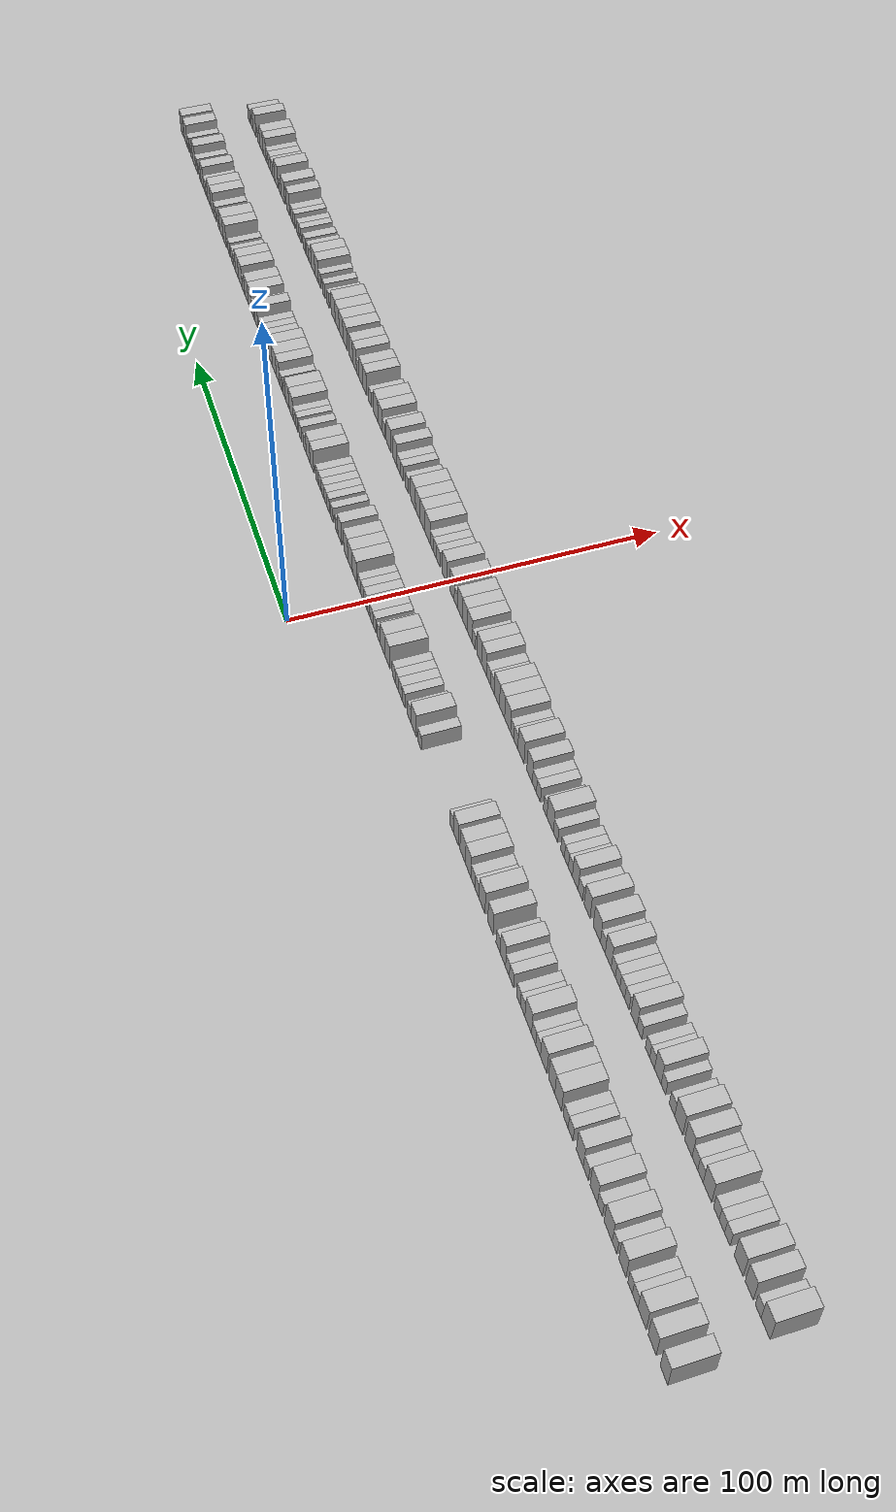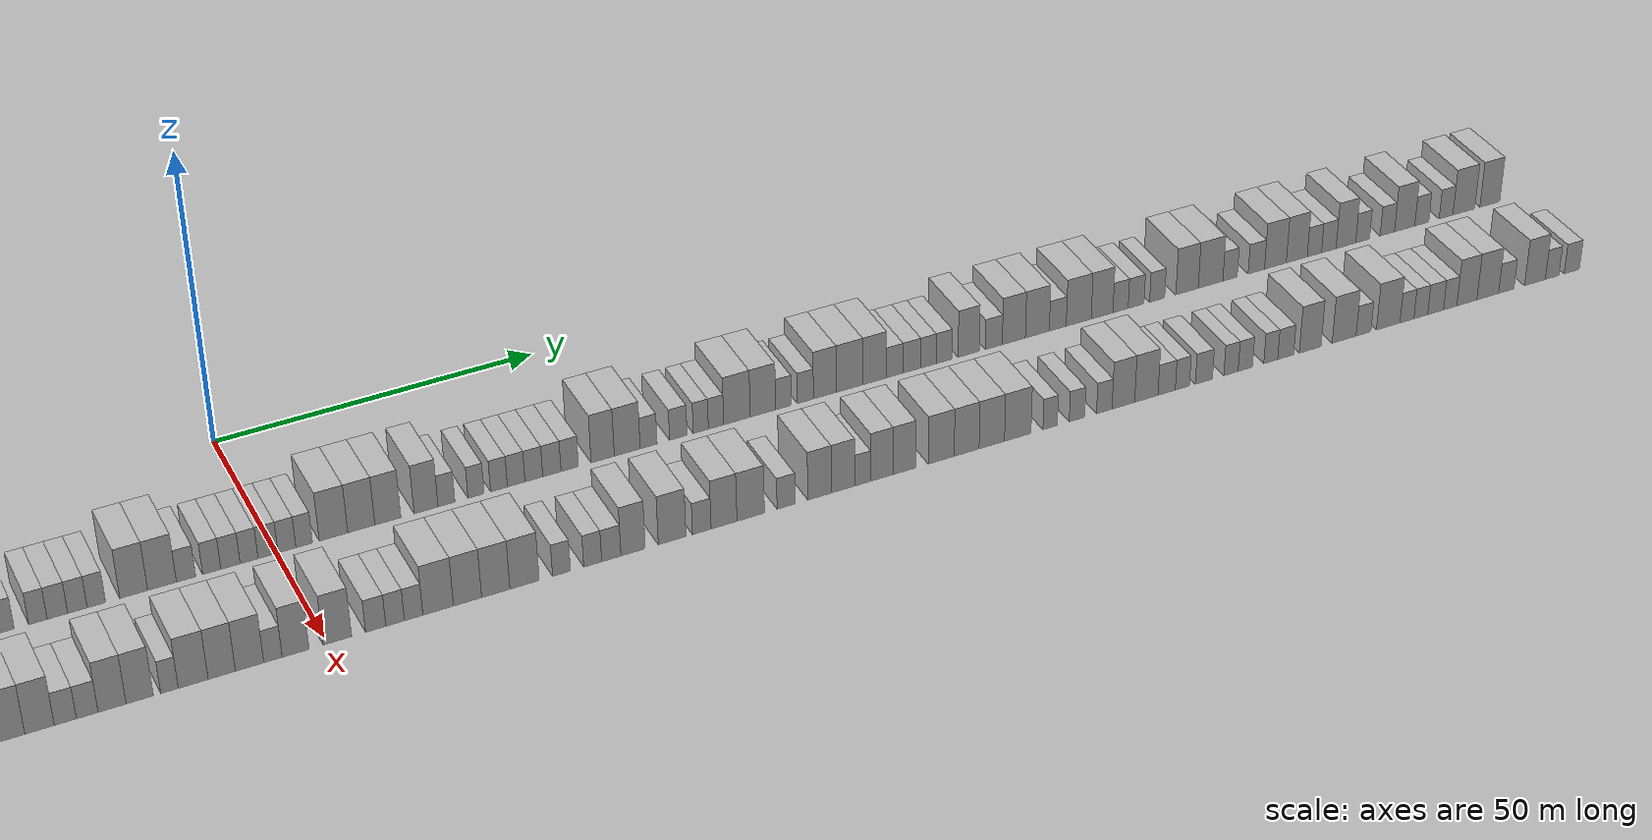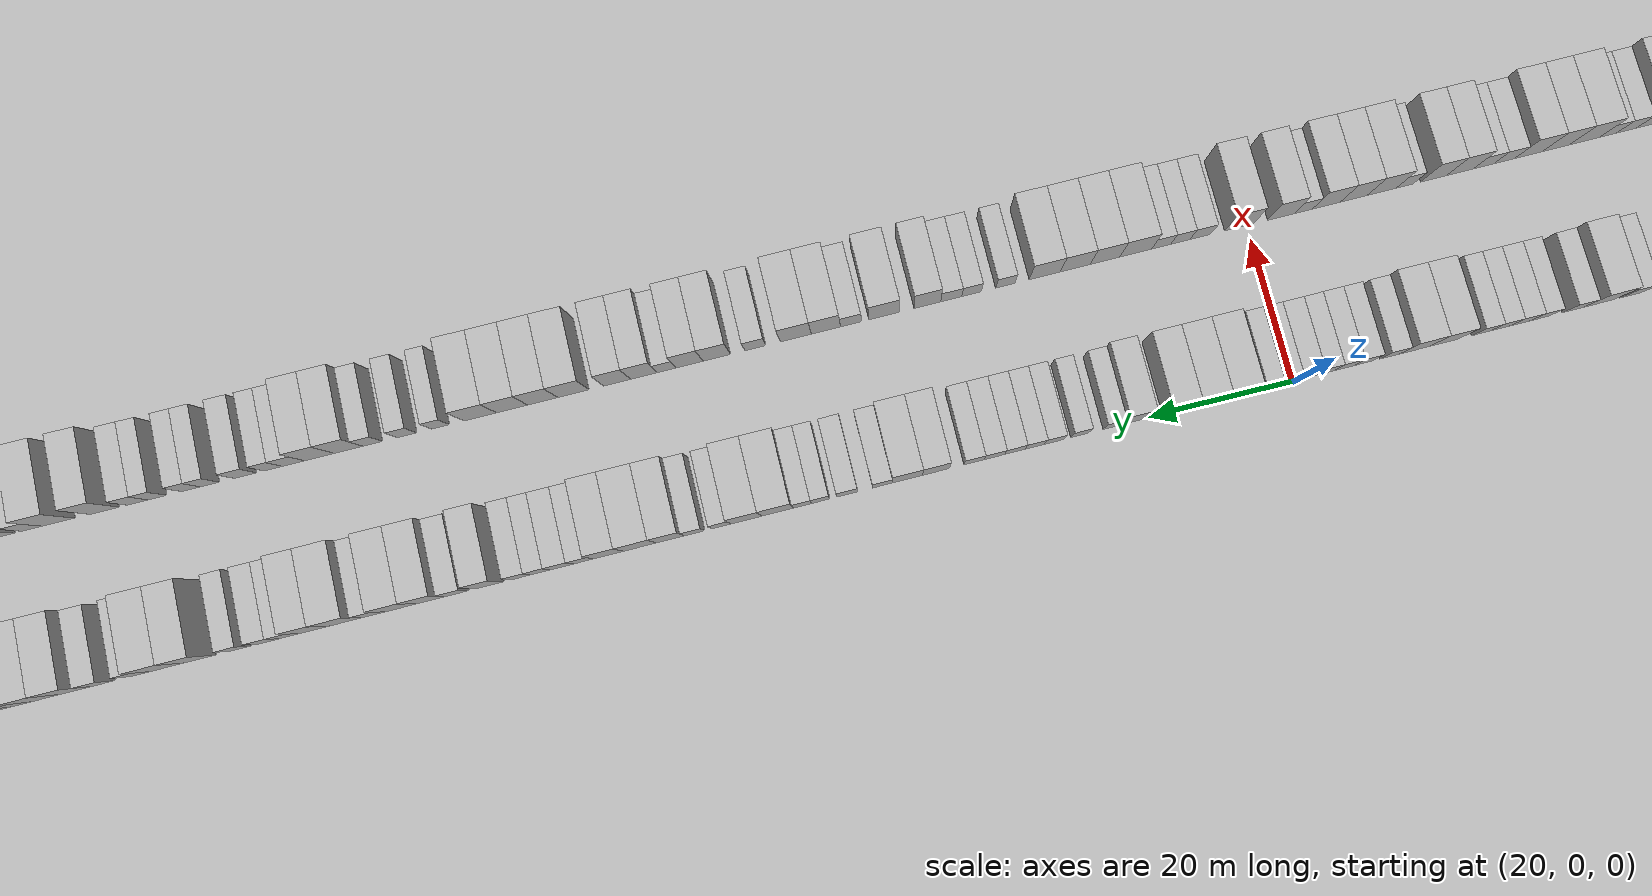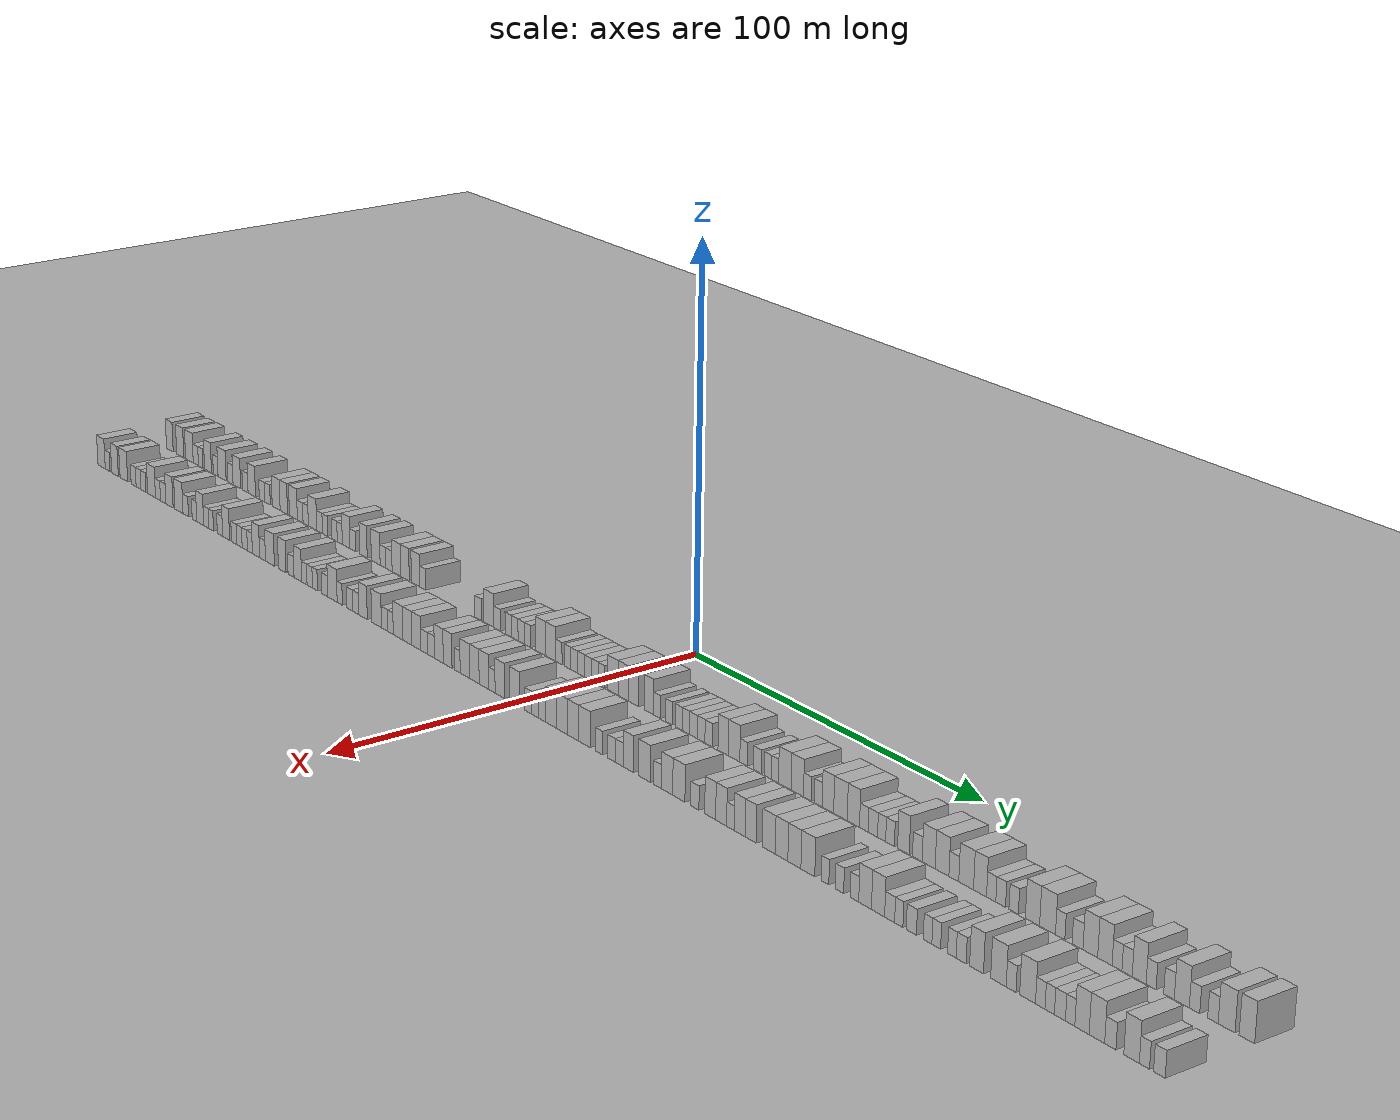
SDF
<?xml version="1.0" encoding="utf-8"?>

<sdf version="1.6">

   <world name="default">

      <gui fullscreen="0">

         <camera name="user_camera">

            <pose>-15 0 4.57585 0 0 0</pose>

            <view_controller>orbit</view_controller>

         </camera>

      </gui>

      <scene>

         <sky>

           <clouds>

             <speed>12</speed>

           </clouds>

         </sky>

         <ambient>0.4 0.4 0.4 1</ambient>

         <background>0.7 0.7 0.7 1</background>

         <shadows>1</shadows>

      </scene>

      <gravity>0 0 -9.8066</gravity>

      <magnetic_field>6e-06 2.3e-05 -4.2e-05</magnetic_field>

      <physics default="0" name="default_physics" type="ode">

         <ode>

            <solver>

               <type>quick</type>

               <iters>10</iters>

               <sor>1.0</sor>

               <use_dynamic_moi_rescaling>0</use_dynamic_moi_rescaling>

            </solver>

            <constraints>

               <cfm>0</cfm>

               <erp>0.2</erp>

               <contact_max_correcting_vel>100</contact_max_correcting_vel>

               <contact_surface_layer>0.001</contact_surface_layer>

            </constraints>

         </ode>

         <max_step_size>0.004</max_step_size>

         <real_time_factor>1</real_time_factor>

         <real_time_update_rate>250</real_time_update_rate>

      </physics>

      <light name="sun" type="directional">

         <cast_shadows>1</cast_shadows>

         <pose>0 0 10 0 0 0</pose>

         <diffuse>0.8 0.8 0.8 1</diffuse>

         <specular>0.2 0.2 0.2 1</specular>

         <attenuation>

            <range>1000</range>

            <constant>0.9</constant>

            <linear>0.01</linear>

            <quadratic>0.001</quadratic>

         </attenuation>

         <direction>-0.5 0.1 -0.9</direction>

      </light>

      <include>

         <name>ground_plane_1</name>

         <uri>model://HANNAS_ground_plane</uri>

         <pose>0 0 0  0 0 0</pose>

      </include>

      <include>

         <name>ground_plane_2</name>

         <uri>model://HANNAS_ground_plane</uri>

         <pose>100 0 0  0 0 0</pose>

      </include>

      <model name="building_1">

         <static>1</static>

         <pose frame="">25.0000 -202.0704 0 0.000000 0.000000 0.000000</pose>

         <link name="link">

            <pose frame="">0 0 4.50 0 0 0</pose>

            <collision name="collision">

               <geometry>

                  <box>

                     <size>10.0000 3.8591 9.0000</size>

                  </box>

               </geometry>

               <max_contacts>10</max_contacts>

               <surface>

                  <contact>

                     <ode/>

                  </contact>

                  <bounce/>

                  <friction>

                     <torsional>

                        <ode/>

                     </torsional>

                     <ode/>

                  </friction>

               </surface>

            </collision>

            <visual name="visual">

               <cast_shadows>0</cast_shadows>

               <geometry>

                  <box>

                     <size>10.0000 3.8591 9.0000</size>

                  </box>

               </geometry>

               <material>

                  <script>

                     <uri>model://HANNAS_wall/materials/scripts</uri>

                     <uri>model://HANNAS_wall/materials/textures</uri>

                     <name>vrc/HANNAS_wall</name>

                  </script>

               </material>

            </visual>

            <self_collide>0</self_collide>

            <enable_wind>0</enable_wind>

            <kinematic>0</kinematic>

         </link>

      </model>

      <model name="building_2">

         <static>1</static>

         <pose frame="">25.0000 -196.0770 0 0.000000 0.000000 0.000000</pose>

         <link name="link">

            <pose frame="">0 0 4.50 0 0 0</pose>

            <collision name="collision">

               <geometry>

                  <box>

                     <size>10.0000 4.1278 9.0000</size>

                  </box>

               </geometry>

               <max_contacts>10</max_contacts>

               <surface>

                  <contact>

                     <ode/>

                  </contact>

                  <bounce/>

                  <friction>

                     <torsional>

                        <ode/>

                     </torsional>

                     <ode/>

                  </friction>

               </surface>

            </collision>

            <visual name="visual">

               <cast_shadows>0</cast_shadows>

               <geometry>

                  <box>

                     <size>10.0000 4.1278 9.0000</size>

                  </box>

               </geometry>

               <material>

                  <script>

                     <uri>model://HANNAS_wall/materials/scripts</uri>

                     <uri>model://HANNAS_wall/materials/textures</uri>

                     <name>vrc/HANNAS_wall</name>

                  </script>

               </material>

            </visual>

            <self_collide>0</self_collide>

            <enable_wind>0</enable_wind>

            <kinematic>0</kinematic>

         </link>

      </model>

      <model name="building_3">

         <static>1</static>

         <pose frame="">25.0000 -190.8556 0 0.000000 0.000000 0.000000</pose>

         <link name="link">

            <pose frame="">0 0 4.50 0 0 0</pose>

            <collision name="collision">

               <geometry>

                  <box>

                     <size>10.0000 4.3151 9.0000</size>

                  </box>

               </geometry>

               <max_contacts>10</max_contacts>

               <surface>

                  <contact>

                     <ode/>

                  </contact>

                  <bounce/>

                  <friction>

                     <torsional>

                        <ode/>

                     </torsional>

                     <ode/>

                  </friction>

               </surface>

            </collision>

            <visual name="visual">

               <cast_shadows>0</cast_shadows>

               <geometry>

                  <box>

                     <size>10.0000 4.3151 9.0000</size>

                  </box>

               </geometry>

               <material>

                  <script>

                     <uri>model://HANNAS_wall/materials/scripts</uri>

                     <uri>model://HANNAS_wall/materials/textures</uri>

                     <name>vrc/HANNAS_wall</name>

                  </script>

               </material>

            </visual>

            <self_collide>0</self_collide>

            <enable_wind>0</enable_wind>

            <kinematic>0</kinematic>

         </link>

      </model>

      <model name="building_4">

         <static>1</static>

         <pose frame="">25.0000 -187.2225 0 0.000000 0.000000 0.000000</pose>

         <link name="link">

            <pose frame="">0 0 3.00 0 0 0</pose>

            <collision name="collision">

               <geometry>

                  <box>

                     <size>10.0000 2.9510 6.0000</size>

                  </box>

               </geometry>

               <max_contacts>10</max_contacts>

               <surface>

                  <contact>

                     <ode/>

                  </contact>

                  <bounce/>

                  <friction>

                     <torsional>

                        <ode/>

                     </torsional>

                     <ode/>

                  </friction>

               </surface>

            </collision>

            <visual name="visual">

               <cast_shadows>0</cast_shadows>

               <geometry>

                  <box>

                     <size>10.0000 2.9510 6.0000</size>

                  </box>

               </geometry>

               <material>

                  <script>

                     <uri>model://HANNAS_wall/materials/scripts</uri>

                     <uri>model://HANNAS_wall/materials/textures</uri>

                     <name>vrc/HANNAS_wall</name>

                  </script>

               </material>

            </visual>

            <self_collide>0</self_collide>

            <enable_wind>0</enable_wind>

            <kinematic>0</kinematic>

         </link>

      </model>

      <model name="building_5">

         <static>1</static>

         <pose frame="">25.0000 -184.5320 0 0.000000 0.000000 0.000000</pose>

         <link name="link">

            <pose frame="">0 0 3.00 0 0 0</pose>

            <collision name="collision">

               <geometry>

                  <box>

                     <size>10.0000 2.4300 6.0000</size>

                  </box>

               </geometry>

               <max_contacts>10</max_contacts>

               <surface>

                  <contact>

                     <ode/>

                  </contact>

                  <bounce/>

                  <friction>

                     <torsional>

                        <ode/>

                     </torsional>

                     <ode/>

                  </friction>

               </surface>

            </collision>

            <visual name="visual">

               <cast_shadows>0</cast_shadows>

               <geometry>

                  <box>

                     <size>10.0000 2.4300 6.0000</size>

                  </box>

               </geometry>

               <material>

                  <script>

                     <uri>model://HANNAS_wall/materials/scripts</uri>

                     <uri>model://HANNAS_wall/materials/textures</uri>

                     <name>vrc/HANNAS_wall</name>

                  </script>

               </material>

            </visual>

            <self_collide>0</self_collide>

            <enable_wind>0</enable_wind>

            <kinematic>0</kinematic>

         </link>

      </model>

      <model name="building_6">

         <static>1</static>

         <pose frame="">25.0000 -180.3753 0 0.000000 0.000000 0.000000</pose>

         <link name="link">

            <pose frame="">0 0 4.50 0 0 0</pose>

            <collision name="collision">

               <geometry>

                  <box>

                     <size>10.0000 3.8834 9.0000</size>

                  </box>

               </geometry>

               <max_contacts>10</max_contacts>

               <surface>

                  <contact>

                     <ode/>

                  </contact>

                  <bounce/>

                  <friction>

                     <torsional>

                        <ode/>

                     </torsional>

                     <ode/>

                  </friction>

               </surface>

            </collision>

            <visual name="visual">

               <cast_shadows>0</cast_shadows>

               <geometry>

                  <box>

                     <size>10.0000 3.8834 9.0000</size>

                  </box>

               </geometry>

               <material>

                  <script>

                     <uri>model://HANNAS_wall/materials/scripts</uri>

                     <uri>model://HANNAS_wall/materials/textures</uri>

                     <name>vrc/HANNAS_wall</name>

                  </script>

               </material>

            </visual>

            <self_collide>0</self_collide>

            <enable_wind>0</enable_wind>

            <kinematic>0</kinematic>

         </link>

      </model>

      <model name="building_7">

         <static>1</static>

         <pose frame="">25.0000 -176.1350 0 0.000000 0.000000 0.000000</pose>

         <link name="link">

            <pose frame="">0 0 3.00 0 0 0</pose>

            <collision name="collision">

               <geometry>

                  <box>

                     <size>10.0000 2.5972 6.0000</size>

                  </box>

               </geometry>

               <max_contacts>10</max_contacts>

               <surface>

                  <contact>

                     <ode/>

                  </contact>

                  <bounce/>

                  <friction>

                     <torsional>

                        <ode/>

                     </torsional>

                     <ode/>

                  </friction>

               </surface>

            </collision>

            <visual name="visual">

               <cast_shadows>0</cast_shadows>

               <geometry>

                  <box>

                     <size>10.0000 2.5972 6.0000</size>

                  </box>

               </geometry>

               <material>

                  <script>

                     <uri>model://HANNAS_wall/materials/scripts</uri>

                     <uri>model://HANNAS_wall/materials/textures</uri>

                     <name>vrc/HANNAS_wall</name>

                  </script>

               </material>

            </visual>

            <self_collide>0</self_collide>

            <enable_wind>0</enable_wind>

            <kinematic>0</kinematic>

         </link>

      </model>

      <model name="building_8">

         <static>1</static>

         <pose frame="">25.0000 -172.6063 0 0.000000 0.000000 0.000000</pose>

         <link name="link">

            <pose frame="">0 0 4.50 0 0 0</pose>

            <collision name="collision">

               <geometry>

                  <box>

                     <size>10.0000 4.4603 9.0000</size>

                  </box>

               </geometry>

               <max_contacts>10</max_contacts>

               <surface>

                  <contact>

                     <ode/>

                  </contact>

                  <bounce/>

                  <friction>

                     <torsional>

                        <ode/>

                     </torsional>

                     <ode/>

                  </friction>

               </surface>

            </collision>

            <visual name="visual">

               <cast_shadows>0</cast_shadows>

               <geometry>

                  <box>

                     <size>10.0000 4.4603 9.0000</size>

                  </box>

               </geometry>

               <material>

                  <script>

                     <uri>model://HANNAS_wall/materials/scripts</uri>

                     <uri>model://HANNAS_wall/materials/textures</uri>

                     <name>vrc/HANNAS_wall</name>

                  </script>

               </material>

            </visual>

            <self_collide>0</self_collide>

            <enable_wind>0</enable_wind>

            <kinematic>0</kinematic>

         </link>

      </model>

      <model name="building_9">

         <static>1</static>

         <pose frame="">25.0000 -167.9846 0 0.000000 0.000000 0.000000</pose>

         <link name="link">

            <pose frame="">0 0 3.00 0 0 0</pose>

            <collision name="collision">

               <geometry>

                  <box>

                     <size>10.0000 2.7832 6.0000</size>

                  </box>

               </geometry>

               <max_contacts>10</max_contacts>

               <surface>

                  <contact>

                     <ode/>

                  </contact>

                  <bounce/>

                  <friction>

                     <torsional>

                        <ode/>

                     </torsional>

                     <ode/>

                  </friction>

               </surface>

            </collision>

            <visual name="visual">

               <cast_shadows>0</cast_shadows>

               <geometry>

                  <box>

                     <size>10.0000 2.7832 6.0000</size>

                  </box>

               </geometry>

               <material>

                  <script>

                     <uri>model://HANNAS_wall/materials/scripts</uri>

                     <uri>model://HANNAS_wall/materials/textures</uri>

                     <name>vrc/HANNAS_wall</name>

                  </script>

               </material>

            </visual>

            <self_collide>0</self_collide>

            <enable_wind>0</enable_wind>

            <kinematic>0</kinematic>

         </link>

      </model>

      <model name="building_10">

         <static>1</static>

         <pose frame="">25.0000 -164.5169 0 0.000000 0.000000 0.000000</pose>

         <link name="link">

            <pose frame="">0 0 4.50 0 0 0</pose>

            <collision name="collision">

               <geometry>

                  <box>

                     <size>10.0000 4.1521 9.0000</size>

                  </box>

               </geometry>

               <max_contacts>10</max_contacts>

               <surface>

                  <contact>

                     <ode/>

                  </contact>

                  <bounce/>

                  <friction>

                     <torsional>

                        <ode/>

                     </torsional>

                     <ode/>

                  </friction>

               </surface>

            </collision>

            <visual name="visual">

               <cast_shadows>0</cast_shadows>

               <geometry>

                  <box>

                     <size>10.0000 4.1521 9.0000</size>

                  </box>

               </geometry>

               <material>

                  <script>

                     <uri>model://HANNAS_wall/materials/scripts</uri>

                     <uri>model://HANNAS_wall/materials/textures</uri>

                     <name>vrc/HANNAS_wall</name>

                  </script>

               </material>

            </visual>

            <self_collide>0</self_collide>

            <enable_wind>0</enable_wind>

            <kinematic>0</kinematic>

         </link>

      </model>

      <model name="building_11">

         <static>1</static>

         <pose frame="">25.0000 -159.9686 0 0.000000 0.000000 0.000000</pose>

         <link name="link">

            <pose frame="">0 0 3.00 0 0 0</pose>

            <collision name="collision">

               <geometry>

                  <box>

                     <size>10.0000 2.9445 6.0000</size>

                  </box>

               </geometry>

               <max_contacts>10</max_contacts>

               <surface>

                  <contact>

                     <ode/>

                  </contact>

                  <bounce/>

                  <friction>

                     <torsional>

                        <ode/>

                     </torsional>

                     <ode/>

                  </friction>

               </surface>

            </collision>

            <visual name="visual">

               <cast_shadows>0</cast_shadows>

               <geometry>

                  <box>

                     <size>10.0000 2.9445 6.0000</size>

                  </box>

               </geometry>

               <material>

                  <script>

                     <uri>model://HANNAS_wall/materials/scripts</uri>

                     <uri>model://HANNAS_wall/materials/textures</uri>

                     <name>vrc/HANNAS_wall</name>

                  </script>

               </material>

            </visual>

            <self_collide>0</self_collide>

            <enable_wind>0</enable_wind>

            <kinematic>0</kinematic>

         </link>

      </model>

      <model name="building_12">

         <static>1</static>

         <pose frame="">25.0000 -156.4924 0 0.000000 0.000000 0.000000</pose>

         <link name="link">

            <pose frame="">0 0 4.50 0 0 0</pose>

            <collision name="collision">

               <geometry>

                  <box>

                     <size>10.0000 4.0080 9.0000</size>

                  </box>

               </geometry>

               <max_contacts>10</max_contacts>

               <surface>

                  <contact>

                     <ode/>

                  </contact>

                  <bounce/>

                  <friction>

                     <torsional>

                        <ode/>

                     </torsional>

                     <ode/>

                  </friction>

               </surface>

            </collision>

            <visual name="visual">

               <cast_shadows>0</cast_shadows>

               <geometry>

                  <box>

                     <size>10.0000 4.0080 9.0000</size>

                  </box>

               </geometry>

               <material>

                  <script>

                     <uri>model://HANNAS_wall/materials/scripts</uri>

                     <uri>model://HANNAS_wall/materials/textures</uri>

                     <name>vrc/HANNAS_wall</name>

                  </script>

               </material>

            </visual>

            <self_collide>0</self_collide>

            <enable_wind>0</enable_wind>

            <kinematic>0</kinematic>

         </link>

      </model>

      <model name="building_13">

         <static>1</static>

         <pose frame="">25.0000 -151.0378 0 0.000000 0.000000 0.000000</pose>

         <link name="link">

            <pose frame="">0 0 3.00 0 0 0</pose>

            <collision name="collision">

               <geometry>

                  <box>

                     <size>10.0000 2.9011 6.0000</size>

                  </box>

               </geometry>

               <max_contacts>10</max_contacts>

               <surface>

                  <contact>

                     <ode/>

                  </contact>

                  <bounce/>

                  <friction>

                     <torsional>

                        <ode/>

                     </torsional>

                     <ode/>

                  </friction>

               </surface>

            </collision>

            <visual name="visual">

               <cast_shadows>0</cast_shadows>

               <geometry>

                  <box>

                     <size>10.0000 2.9011 6.0000</size>

                  </box>

               </geometry>

               <material>

                  <script>

                     <uri>model://HANNAS_wall/materials/scripts</uri>

                     <uri>model://HANNAS_wall/materials/textures</uri>

                     <name>vrc/HANNAS_wall</name>

                  </script>

               </material>

            </visual>

            <self_collide>0</self_collide>

            <enable_wind>0</enable_wind>

            <kinematic>0</kinematic>

         </link>

      </model>

      <model name="building_14">

         <static>1</static>

         <pose frame="">25.0000 -148.1292 0 0.000000 0.000000 0.000000</pose>

         <link name="link">

            <pose frame="">0 0 3.00 0 0 0</pose>

            <collision name="collision">

               <geometry>

                  <box>

                     <size>10.0000 2.9161 6.0000</size>

                  </box>

               </geometry>

               <max_contacts>10</max_contacts>

               <surface>

                  <contact>

                     <ode/>

                  </contact>

                  <bounce/>

                  <friction>

                     <torsional>

                        <ode/>

                     </torsional>

                     <ode/>

                  </friction>

               </surface>

            </collision>

            <visual name="visual">

               <cast_shadows>0</cast_shadows>

               <geometry>

                  <box>

                     <size>10.0000 2.9161 6.0000</size>

                  </box>

               </geometry>

               <material>

                  <script>

                     <uri>model://HANNAS_wall/materials/scripts</uri>

                     <uri>model://HANNAS_wall/materials/textures</uri>

                     <name>vrc/HANNAS_wall</name>

                  </script>

               </material>

            </visual>

            <self_collide>0</self_collide>

            <enable_wind>0</enable_wind>

            <kinematic>0</kinematic>

         </link>

      </model>

      <model name="building_15">

         <static>1</static>

         <pose frame="">25.0000 -143.6007 0 0.000000 0.000000 0.000000</pose>

         <link name="link">

            <pose frame="">0 0 4.50 0 0 0</pose>

            <collision name="collision">

               <geometry>

                  <box>

                     <size>10.0000 4.1409 9.0000</size>

                  </box>

               </geometry>

               <max_contacts>10</max_contacts>

               <surface>

                  <contact>

                     <ode/>

                  </contact>

                  <bounce/>

                  <friction>

                     <torsional>

                        <ode/>

                     </torsional>

                     <ode/>

                  </friction>

               </surface>

            </collision>

            <visual name="visual">

               <cast_shadows>0</cast_shadows>

               <geometry>

                  <box>

                     <size>10.0000 4.1409 9.0000</size>

                  </box>

               </geometry>

               <material>

                  <script>

                     <uri>model://HANNAS_wall/materials/scripts</uri>

                     <uri>model://HANNAS_wall/materials/textures</uri>

                     <name>vrc/HANNAS_wall</name>

                  </script>

               </material>

            </visual>

            <self_collide>0</self_collide>

            <enable_wind>0</enable_wind>

            <kinematic>0</kinematic>

         </link>

      </model>

      <model name="building_16">

         <static>1</static>

         <pose frame="">25.0000 -139.6149 0 0.000000 0.000000 0.000000</pose>

         <link name="link">

            <pose frame="">0 0 4.50 0 0 0</pose>

            <collision name="collision">

               <geometry>

                  <box>

                     <size>10.0000 3.8309 9.0000</size>

                  </box>

               </geometry>

               <max_contacts>10</max_contacts>

               <surface>

                  <contact>

                     <ode/>

                  </contact>

                  <bounce/>

                  <friction>

                     <torsional>

                        <ode/>

                     </torsional>

                     <ode/>

                  </friction>

               </surface>

            </collision>

            <visual name="visual">

               <cast_shadows>0</cast_shadows>

               <geometry>

                  <box>

                     <size>10.0000 3.8309 9.0000</size>

                  </box>

               </geometry>

               <material>

                  <script>

                     <uri>model://HANNAS_wall/materials/scripts</uri>

                     <uri>model://HANNAS_wall/materials/textures</uri>

                     <name>vrc/HANNAS_wall</name>

                  </script>

               </material>

            </visual>

            <self_collide>0</self_collide>

            <enable_wind>0</enable_wind>

            <kinematic>0</kinematic>

         </link>

      </model>

      <model name="building_17">

         <static>1</static>

         <pose frame="">25.0000 -134.6687 0 0.000000 0.000000 0.000000</pose>

         <link name="link">

            <pose frame="">0 0 4.50 0 0 0</pose>

            <collision name="collision">

               <geometry>

                  <box>

                     <size>10.0000 4.0614 9.0000</size>

                  </box>

               </geometry>

               <max_contacts>10</max_contacts>

               <surface>

                  <contact>

                     <ode/>

                  </contact>

                  <bounce/>

                  <friction>

                     <torsional>

                        <ode/>

                     </torsional>

                     <ode/>

                  </friction>

               </surface>

            </collision>

            <visual name="visual">

               <cast_shadows>0</cast_shadows>

               <geometry>

                  <box>

                     <size>10.0000 4.0614 9.0000</size>

                  </box>

               </geometry>

               <material>

                  <script>

                     <uri>model://HANNAS_wall/materials/scripts</uri>

                     <uri>model://HANNAS_wall/materials/textures</uri>

                     <name>vrc/HANNAS_wall</name>

                  </script>

               </material>

            </visual>

            <self_collide>0</self_collide>

            <enable_wind>0</enable_wind>

            <kinematic>0</kinematic>

         </link>

      </model>

      <model name="building_18">

         <static>1</static>

         <pose frame="">25.0000 -131.1882 0 0.000000 0.000000 0.000000</pose>

         <link name="link">

            <pose frame="">0 0 3.00 0 0 0</pose>

            <collision name="collision">

               <geometry>

                  <box>

                     <size>10.0000 2.8995 6.0000</size>

                  </box>

               </geometry>

               <max_contacts>10</max_contacts>

               <surface>

                  <contact>

                     <ode/>

                  </contact>

                  <bounce/>

                  <friction>

                     <torsional>

                        <ode/>

                     </torsional>

                     <ode/>

                  </friction>

               </surface>

            </collision>

            <visual name="visual">

               <cast_shadows>0</cast_shadows>

               <geometry>

                  <box>

                     <size>10.0000 2.8995 6.0000</size>

                  </box>

               </geometry>

               <material>

                  <script>

                     <uri>model://HANNAS_wall/materials/scripts</uri>

                     <uri>model://HANNAS_wall/materials/textures</uri>

                     <name>vrc/HANNAS_wall</name>

                  </script>

               </material>

            </visual>

            <self_collide>0</self_collide>

            <enable_wind>0</enable_wind>

            <kinematic>0</kinematic>

         </link>

      </model>

      <model name="building_19">

         <static>1</static>

         <pose frame="">25.0000 -128.3904 0 0.000000 0.000000 0.000000</pose>

         <link name="link">

            <pose frame="">0 0 3.00 0 0 0</pose>

            <collision name="collision">

               <geometry>

                  <box>

                     <size>10.0000 2.6962 6.0000</size>

                  </box>

               </geometry>

               <max_contacts>10</max_contacts>

               <surface>

                  <contact>

                     <ode/>

                  </contact>

                  <bounce/>

                  <friction>

                     <torsional>

                        <ode/>

                     </torsional>

                     <ode/>

                  </friction>

               </surface>

            </collision>

            <visual name="visual">

               <cast_shadows>0</cast_shadows>

               <geometry>

                  <box>

                     <size>10.0000 2.6962 6.0000</size>

                  </box>

               </geometry>

               <material>

                  <script>

                     <uri>model://HANNAS_wall/materials/scripts</uri>

                     <uri>model://HANNAS_wall/materials/textures</uri>

                     <name>vrc/HANNAS_wall</name>

                  </script>

               </material>

            </visual>

            <self_collide>0</self_collide>

            <enable_wind>0</enable_wind>

            <kinematic>0</kinematic>

         </link>

      </model>

      <model name="building_20">

         <static>1</static>

         <pose frame="">25.0000 -124.9213 0 0.000000 0.000000 0.000000</pose>

         <link name="link">

            <pose frame="">0 0 4.50 0 0 0</pose>

            <collision name="collision">

               <geometry>

                  <box>

                     <size>10.0000 4.2421 9.0000</size>

                  </box>

               </geometry>

               <max_contacts>10</max_contacts>

               <surface>

                  <contact>

                     <ode/>

                  </contact>

                  <bounce/>

                  <friction>

                     <torsional>

                        <ode/>

                     </torsional>

                     <ode/>

                  </friction>

               </surface>

            </collision>

            <visual name="visual">

               <cast_shadows>0</cast_shadows>

               <geometry>

                  <box>

                     <size>10.0000 4.2421 9.0000</size>

                  </box>

               </geometry>

               <material>

                  <script>

                     <uri>model://HANNAS_wall/materials/scripts</uri>

                     <uri>model://HANNAS_wall/materials/textures</uri>

                     <name>vrc/HANNAS_wall</name>

                  </script>

               </material>

            </visual>

            <self_collide>0</self_collide>

            <enable_wind>0</enable_wind>

            <kinematic>0</kinematic>

         </link>

      </model>

      <model name="building_21">

         <static>1</static>

         <pose frame="">25.0000 -121.3675 0 0.000000 0.000000 0.000000</pose>

         <link name="link">

            <pose frame="">0 0 3.00 0 0 0</pose>

            <collision name="collision">

               <geometry>

                  <box>

                     <size>10.0000 2.8654 6.0000</size>

                  </box>

               </geometry>

               <max_contacts>10</max_contacts>

               <surface>

                  <contact>

                     <ode/>

                  </contact>

                  <bounce/>

                  <friction>

                     <torsional>

                        <ode/>

                     </torsional>

                     <ode/>

                  </friction>

               </surface>

            </collision>

            <visual name="visual">

               <cast_shadows>0</cast_shadows>

               <geometry>

                  <box>

                     <size>10.0000 2.8654 6.0000</size>

                  </box>

               </geometry>

               <material>

                  <script>

                     <uri>model://HANNAS_wall/materials/scripts</uri>

                     <uri>model://HANNAS_wall/materials/textures</uri>

                     <name>vrc/HANNAS_wall</name>

                  </script>

               </material>

            </visual>

            <self_collide>0</self_collide>

            <enable_wind>0</enable_wind>

            <kinematic>0</kinematic>

         </link>

      </model>

      <model name="building_22">

         <static>1</static>

         <pose frame="">25.0000 -118.6558 0 0.000000 0.000000 0.000000</pose>

         <link name="link">

            <pose frame="">0 0 3.00 0 0 0</pose>

            <collision name="collision">

               <geometry>

                  <box>

                     <size>10.0000 2.5581 6.0000</size>

                  </box>

               </geometry>

               <max_contacts>10</max_contacts>

               <surface>

                  <contact>

                     <ode/>

                  </contact>

                  <bounce/>

                  <friction>

                     <torsional>

                        <ode/>

                     </torsional>

                     <ode/>

                  </friction>

               </surface>

            </collision>

            <visual name="visual">

               <cast_shadows>0</cast_shadows>

               <geometry>

                  <box>

                     <size>10.0000 2.5581 6.0000</size>

                  </box>

               </geometry>

               <material>

                  <script>

                     <uri>model://HANNAS_wall/materials/scripts</uri>

                     <uri>model://HANNAS_wall/materials/textures</uri>

                     <name>vrc/HANNAS_wall</name>

                  </script>

               </material>

            </visual>

            <self_collide>0</self_collide>

            <enable_wind>0</enable_wind>

            <kinematic>0</kinematic>

         </link>

      </model>

      <model name="building_23">

         <static>1</static>

         <pose frame="">25.0000 -113.9803 0 0.000000 0.000000 0.000000</pose>

         <link name="link">

            <pose frame="">0 0 3.00 0 0 0</pose>

            <collision name="collision">

               <geometry>

                  <box>

                     <size>10.0000 2.7928 6.0000</size>

                  </box>

               </geometry>

               <max_contacts>10</max_contacts>

               <surface>

                  <contact>

                     <ode/>

                  </contact>

                  <bounce/>

                  <friction>

                     <torsional>

                        <ode/>

                     </torsional>

                     <ode/>

                  </friction>

               </surface>

            </collision>

            <visual name="visual">

               <cast_shadows>0</cast_shadows>

               <geometry>

                  <box>

                     <size>10.0000 2.7928 6.0000</size>

                  </box>

               </geometry>

               <material>

                  <script>

                     <uri>model://HANNAS_wall/materials/scripts</uri>

                     <uri>model://HANNAS_wall/materials/textures</uri>

                     <name>vrc/HANNAS_wall</name>

                  </script>

               </material>

            </visual>

            <self_collide>0</self_collide>

            <enable_wind>0</enable_wind>

            <kinematic>0</kinematic>

         </link>

      </model>

      <model name="building_24">

         <static>1</static>

         <pose frame="">25.0000 -111.3257 0 0.000000 0.000000 0.000000</pose>

         <link name="link">

            <pose frame="">0 0 3.00 0 0 0</pose>

            <collision name="collision">

               <geometry>

                  <box>

                     <size>10.0000 2.5165 6.0000</size>

                  </box>

               </geometry>

               <max_contacts>10</max_contacts>

               <surface>

                  <contact>

                     <ode/>

                  </contact>

                  <bounce/>

                  <friction>

                     <torsional>

                        <ode/>

                     </torsional>

                     <ode/>

                  </friction>

               </surface>

            </collision>

            <visual name="visual">

               <cast_shadows>0</cast_shadows>

               <geometry>

                  <box>

                     <size>10.0000 2.5165 6.0000</size>

                  </box>

               </geometry>

               <material>

                  <script>

                     <uri>model://HANNAS_wall/materials/scripts</uri>

                     <uri>model://HANNAS_wall/materials/textures</uri>

                     <name>vrc/HANNAS_wall</name>

                  </script>

               </material>

            </visual>

            <self_collide>0</self_collide>

            <enable_wind>0</enable_wind>

            <kinematic>0</kinematic>

         </link>

      </model>

      <model name="building_25">

         <static>1</static>

         <pose frame="">25.0000 -108.2355 0 0.000000 0.000000 0.000000</pose>

         <link name="link">

            <pose frame="">0 0 4.50 0 0 0</pose>

            <collision name="collision">

               <geometry>

                  <box>

                     <size>10.0000 3.6637 9.0000</size>

                  </box>

               </geometry>

               <max_contacts>10</max_contacts>

               <surface>

                  <contact>

                     <ode/>

                  </contact>

                  <bounce/>

                  <friction>

                     <torsional>

                        <ode/>

                     </torsional>

                     <ode/>

                  </friction>

               </surface>

            </collision>

            <visual name="visual">

               <cast_shadows>0</cast_shadows>

               <geometry>

                  <box>

                     <size>10.0000 3.6637 9.0000</size>

                  </box>

               </geometry>

               <material>

                  <script>

                     <uri>model://HANNAS_wall/materials/scripts</uri>

                     <uri>model://HANNAS_wall/materials/textures</uri>

                     <name>vrc/HANNAS_wall</name>

                  </script>

               </material>

            </visual>

            <self_collide>0</self_collide>

            <enable_wind>0</enable_wind>

            <kinematic>0</kinematic>

         </link>

      </model>

      <model name="building_26">

         <static>1</static>

         <pose frame="">25.0000 -105.0088 0 0.000000 0.000000 0.000000</pose>

         <link name="link">

            <pose frame="">0 0 3.00 0 0 0</pose>

            <collision name="collision">

               <geometry>

                  <box>

                     <size>10.0000 2.7897 6.0000</size>

                  </box>

               </geometry>

               <max_contacts>10</max_contacts>

               <surface>

                  <contact>

                     <ode/>

                  </contact>

                  <bounce/>

                  <friction>

                     <torsional>

                        <ode/>

                     </torsional>

                     <ode/>

                  </friction>

               </surface>

            </collision>

            <visual name="visual">

               <cast_shadows>0</cast_shadows>

               <geometry>

                  <box>

                     <size>10.0000 2.7897 6.0000</size>

                  </box>

               </geometry>

               <material>

                  <script>

                     <uri>model://HANNAS_wall/materials/scripts</uri>

                     <uri>model://HANNAS_wall/materials/textures</uri>

                     <name>vrc/HANNAS_wall</name>

                  </script>

               </material>

            </visual>

            <self_collide>0</self_collide>

            <enable_wind>0</enable_wind>

            <kinematic>0</kinematic>

         </link>

      </model>

      <model name="building_27">

         <static>1</static>

         <pose frame="">25.0000 -99.8096 0 0.000000 0.000000 0.000000</pose>

         <link name="link">

            <pose frame="">0 0 4.50 0 0 0</pose>

            <collision name="collision">

               <geometry>

                  <box>

                     <size>10.0000 3.6088 9.0000</size>

                  </box>

               </geometry>

               <max_contacts>10</max_contacts>

               <surface>

                  <contact>

                     <ode/>

                  </contact>

                  <bounce/>

                  <friction>

                     <torsional>

                        <ode/>

                     </torsional>

                     <ode/>

                  </friction>

               </surface>

            </collision>

            <visual name="visual">

               <cast_shadows>0</cast_shadows>

               <geometry>

                  <box>

                     <size>10.0000 3.6088 9.0000</size>

                  </box>

               </geometry>

               <material>

                  <script>

                     <uri>model://HANNAS_wall/materials/scripts</uri>

                     <uri>model://HANNAS_wall/materials/textures</uri>

                     <name>vrc/HANNAS_wall</name>

                  </script>

               </material>

            </visual>

            <self_collide>0</self_collide>

            <enable_wind>0</enable_wind>

            <kinematic>0</kinematic>

         </link>

      </model>

      <model name="building_28">

         <static>1</static>

         <pose frame="">25.0000 -93.9112 0 0.000000 0.000000 0.000000</pose>

         <link name="link">

            <pose frame="">0 0 4.50 0 0 0</pose>

            <collision name="collision">

               <geometry>

                  <box>

                     <size>10.0000 4.1880 9.0000</size>

                  </box>

               </geometry>

               <max_contacts>10</max_contacts>

               <surface>

                  <contact>

                     <ode/>

                  </contact>

                  <bounce/>

                  <friction>

                     <torsional>

                        <ode/>

                     </torsional>

                     <ode/>

                  </friction>

               </surface>

            </collision>

            <visual name="visual">

               <cast_shadows>0</cast_shadows>

               <geometry>

                  <box>

                     <size>10.0000 4.1880 9.0000</size>

                  </box>

               </geometry>

               <material>

                  <script>

                     <uri>model://HANNAS_wall/materials/scripts</uri>

                     <uri>model://HANNAS_wall/materials/textures</uri>

                     <name>vrc/HANNAS_wall</name>

                  </script>

               </material>

            </visual>

            <self_collide>0</self_collide>

            <enable_wind>0</enable_wind>

            <kinematic>0</kinematic>

         </link>

      </model>

      <model name="building_29">

         <static>1</static>

         <pose frame="">25.0000 -90.4857 0 0.000000 0.000000 0.000000</pose>

         <link name="link">

            <pose frame="">0 0 3.00 0 0 0</pose>

            <collision name="collision">

               <geometry>

                  <box>

                     <size>10.0000 2.6630 6.0000</size>

                  </box>

               </geometry>

               <max_contacts>10</max_contacts>

               <surface>

                  <contact>

                     <ode/>

                  </contact>

                  <bounce/>

                  <friction>

                     <torsional>

                        <ode/>

                     </torsional>

                     <ode/>

                  </friction>

               </surface>

            </collision>

            <visual name="visual">

               <cast_shadows>0</cast_shadows>

               <geometry>

                  <box>

                     <size>10.0000 2.6630 6.0000</size>

                  </box>

               </geometry>

               <material>

                  <script>

                     <uri>model://HANNAS_wall/materials/scripts</uri>

                     <uri>model://HANNAS_wall/materials/textures</uri>

                     <name>vrc/HANNAS_wall</name>

                  </script>

               </material>

            </visual>

            <self_collide>0</self_collide>

            <enable_wind>0</enable_wind>

            <kinematic>0</kinematic>

         </link>

      </model>

      <model name="building_30">

         <static>1</static>

         <pose frame="">25.0000 -87.6569 0 0.000000 0.000000 0.000000</pose>

         <link name="link">

            <pose frame="">0 0 3.00 0 0 0</pose>

            <collision name="collision">

               <geometry>

                  <box>

                     <size>10.0000 2.9945 6.0000</size>

                  </box>

               </geometry>

               <max_contacts>10</max_contacts>

               <surface>

                  <contact>

                     <ode/>

                  </contact>

                  <bounce/>

                  <friction>

                     <torsional>

                        <ode/>

                     </torsional>

                     <ode/>

                  </friction>

               </surface>

            </collision>

            <visual name="visual">

               <cast_shadows>0</cast_shadows>

               <geometry>

                  <box>

                     <size>10.0000 2.9945 6.0000</size>

                  </box>

               </geometry>

               <material>

                  <script>

                     <uri>model://HANNAS_wall/materials/scripts</uri>

                     <uri>model://HANNAS_wall/materials/textures</uri>

                     <name>vrc/HANNAS_wall</name>

                  </script>

               </material>

            </visual>

            <self_collide>0</self_collide>

            <enable_wind>0</enable_wind>

            <kinematic>0</kinematic>

         </link>

      </model>

      <model name="building_31">

         <static>1</static>

         <pose frame="">25.0000 -84.1616 0 0.000000 0.000000 0.000000</pose>

         <link name="link">

            <pose frame="">0 0 4.50 0 0 0</pose>

            <collision name="collision">

               <geometry>

                  <box>

                     <size>10.0000 3.9961 9.0000</size>

                  </box>

               </geometry>

               <max_contacts>10</max_contacts>

               <surface>

                  <contact>

                     <ode/>

                  </contact>

                  <bounce/>

                  <friction>

                     <torsional>

                        <ode/>

                     </torsional>

                     <ode/>

                  </friction>

               </surface>

            </collision>

            <visual name="visual">

               <cast_shadows>0</cast_shadows>

               <geometry>

                  <box>

                     <size>10.0000 3.9961 9.0000</size>

                  </box>

               </geometry>

               <material>

                  <script>

                     <uri>model://HANNAS_wall/materials/scripts</uri>

                     <uri>model://HANNAS_wall/materials/textures</uri>

                     <name>vrc/HANNAS_wall</name>

                  </script>

               </material>

            </visual>

            <self_collide>0</self_collide>

            <enable_wind>0</enable_wind>

            <kinematic>0</kinematic>

         </link>

      </model>

      <model name="building_32">

         <static>1</static>

         <pose frame="">25.0000 -80.1610 0 0.000000 0.000000 0.000000</pose>

         <link name="link">

            <pose frame="">0 0 4.50 0 0 0</pose>

            <collision name="collision">

               <geometry>

                  <box>

                     <size>10.0000 4.0050 9.0000</size>

                  </box>

               </geometry>

               <max_contacts>10</max_contacts>

               <surface>

                  <contact>

                     <ode/>

                  </contact>

                  <bounce/>

                  <friction>

                     <torsional>

                        <ode/>

                     </torsional>

                     <ode/>

                  </friction>

               </surface>

            </collision>

            <visual name="visual">

               <cast_shadows>0</cast_shadows>

               <geometry>

                  <box>

                     <size>10.0000 4.0050 9.0000</size>

                  </box>

               </geometry>

               <material>

                  <script>

                     <uri>model://HANNAS_wall/materials/scripts</uri>

                     <uri>model://HANNAS_wall/materials/textures</uri>

                     <name>vrc/HANNAS_wall</name>

                  </script>

               </material>

            </visual>

            <self_collide>0</self_collide>

            <enable_wind>0</enable_wind>

            <kinematic>0</kinematic>

         </link>

      </model>

      <model name="building_33">

         <static>1</static>

         <pose frame="">25.0000 -75.2161 0 0.000000 0.000000 0.000000</pose>

         <link name="link">

            <pose frame="">0 0 4.50 0 0 0</pose>

            <collision name="collision">

               <geometry>

                  <box>

                     <size>10.0000 3.8848 9.0000</size>

                  </box>

               </geometry>

               <max_contacts>10</max_contacts>

               <surface>

                  <contact>

                     <ode/>

                  </contact>

                  <bounce/>

                  <friction>

                     <torsional>

                        <ode/>

                     </torsional>

                     <ode/>

                  </friction>

               </surface>

            </collision>

            <visual name="visual">

               <cast_shadows>0</cast_shadows>

               <geometry>

                  <box>

                     <size>10.0000 3.8848 9.0000</size>

                  </box>

               </geometry>

               <material>

                  <script>

                     <uri>model://HANNAS_wall/materials/scripts</uri>

                     <uri>model://HANNAS_wall/materials/textures</uri>

                     <name>vrc/HANNAS_wall</name>

                  </script>

               </material>

            </visual>

            <self_collide>0</self_collide>

            <enable_wind>0</enable_wind>

            <kinematic>0</kinematic>

         </link>

      </model>

      <model name="building_34">

         <static>1</static>

         <pose frame="">25.0000 -71.9064 0 0.000000 0.000000 0.000000</pose>

         <link name="link">

            <pose frame="">0 0 3.00 0 0 0</pose>

            <collision name="collision">

               <geometry>

                  <box>

                     <size>10.0000 2.7346 6.0000</size>

                  </box>

               </geometry>

               <max_contacts>10</max_contacts>

               <surface>

                  <contact>

                     <ode/>

                  </contact>

                  <bounce/>

                  <friction>

                     <torsional>

                        <ode/>

                     </torsional>

                     <ode/>

                  </friction>

               </surface>

            </collision>

            <visual name="visual">

               <cast_shadows>0</cast_shadows>

               <geometry>

                  <box>

                     <size>10.0000 2.7346 6.0000</size>

                  </box>

               </geometry>

               <material>

                  <script>

                     <uri>model://HANNAS_wall/materials/scripts</uri>

                     <uri>model://HANNAS_wall/materials/textures</uri>

                     <name>vrc/HANNAS_wall</name>

                  </script>

               </material>

            </visual>

            <self_collide>0</self_collide>

            <enable_wind>0</enable_wind>

            <kinematic>0</kinematic>

         </link>

      </model>

      <model name="building_35">

         <static>1</static>

         <pose frame="">25.0000 -47.2095 0 0.000000 0.000000 0.000000</pose>

         <link name="link">

            <pose frame="">0 0 3.00 0 0 0</pose>

            <collision name="collision">

               <geometry>

                  <box>

                     <size>10.0000 2.8864 6.0000</size>

                  </box>

               </geometry>

               <max_contacts>10</max_contacts>

               <surface>

                  <contact>

                     <ode/>

                  </contact>

                  <bounce/>

                  <friction>

                     <torsional>

                        <ode/>

                     </torsional>

                     <ode/>

                  </friction>

               </surface>

            </collision>

            <visual name="visual">

               <cast_shadows>0</cast_shadows>

               <geometry>

                  <box>

                     <size>10.0000 2.8864 6.0000</size>

                  </box>

               </geometry>

               <material>

                  <script>

                     <uri>model://HANNAS_wall/materials/scripts</uri>

                     <uri>model://HANNAS_wall/materials/textures</uri>

                     <name>vrc/HANNAS_wall</name>

                  </script>

               </material>

            </visual>

            <self_collide>0</self_collide>

            <enable_wind>0</enable_wind>

            <kinematic>0</kinematic>

         </link>

      </model>

      <model name="building_36">

         <static>1</static>

         <pose frame="">25.0000 -42.6026 0 0.000000 0.000000 0.000000</pose>

         <link name="link">

            <pose frame="">0 0 4.50 0 0 0</pose>

            <collision name="collision">

               <geometry>

                  <box>

                     <size>10.0000 4.3273 9.0000</size>

                  </box>

               </geometry>

               <max_contacts>10</max_contacts>

               <surface>

                  <contact>

                     <ode/>

                  </contact>

                  <bounce/>

                  <friction>

                     <torsional>

                        <ode/>

                     </torsional>

                     <ode/>

                  </friction>

               </surface>

            </collision>

            <visual name="visual">

               <cast_shadows>0</cast_shadows>

               <geometry>

                  <box>

                     <size>10.0000 4.3273 9.0000</size>

                  </box>

               </geometry>

               <material>

                  <script>

                     <uri>model://HANNAS_wall/materials/scripts</uri>

                     <uri>model://HANNAS_wall/materials/textures</uri>

                     <name>vrc/HANNAS_wall</name>

                  </script>

               </material>

            </visual>

            <self_collide>0</self_collide>

            <enable_wind>0</enable_wind>

            <kinematic>0</kinematic>

         </link>

      </model>

      <model name="building_37">

         <static>1</static>

         <pose frame="">25.0000 -39.0143 0 0.000000 0.000000 0.000000</pose>

         <link name="link">

            <pose frame="">0 0 3.00 0 0 0</pose>

            <collision name="collision">

               <geometry>

                  <box>

                     <size>10.0000 2.8494 6.0000</size>

                  </box>

               </geometry>

               <max_contacts>10</max_contacts>

               <surface>

                  <contact>

                     <ode/>

                  </contact>

                  <bounce/>

                  <friction>

                     <torsional>

                        <ode/>

                     </torsional>

                     <ode/>

                  </friction>

               </surface>

            </collision>

            <visual name="visual">

               <cast_shadows>0</cast_shadows>

               <geometry>

                  <box>

                     <size>10.0000 2.8494 6.0000</size>

                  </box>

               </geometry>

               <material>

                  <script>

                     <uri>model://HANNAS_wall/materials/scripts</uri>

                     <uri>model://HANNAS_wall/materials/textures</uri>

                     <name>vrc/HANNAS_wall</name>

                  </script>

               </material>

            </visual>

            <self_collide>0</self_collide>

            <enable_wind>0</enable_wind>

            <kinematic>0</kinematic>

         </link>

      </model>

      <model name="building_38">

         <static>1</static>

         <pose frame="">25.0000 -34.3015 0 0.000000 0.000000 0.000000</pose>

         <link name="link">

            <pose frame="">0 0 3.00 0 0 0</pose>

            <collision name="collision">

               <geometry>

                  <box>

                     <size>10.0000 2.5761 6.0000</size>

                  </box>

               </geometry>

               <max_contacts>10</max_contacts>

               <surface>

                  <contact>

                     <ode/>

                  </contact>

                  <bounce/>

                  <friction>

                     <torsional>

                        <ode/>

                     </torsional>

                     <ode/>

                  </friction>

               </surface>

            </collision>

            <visual name="visual">

               <cast_shadows>0</cast_shadows>

               <geometry>

                  <box>

                     <size>10.0000 2.5761 6.0000</size>

                  </box>

               </geometry>

               <material>

                  <script>

                     <uri>model://HANNAS_wall/materials/scripts</uri>

                     <uri>model://HANNAS_wall/materials/textures</uri>

                     <name>vrc/HANNAS_wall</name>

                  </script>

               </material>

            </visual>

            <self_collide>0</self_collide>

            <enable_wind>0</enable_wind>

            <kinematic>0</kinematic>

         </link>

      </model>

      <model name="building_39">

         <static>1</static>

         <pose frame="">25.0000 -31.5714 0 0.000000 0.000000 0.000000</pose>

         <link name="link">

            <pose frame="">0 0 3.00 0 0 0</pose>

            <collision name="collision">

               <geometry>

                  <box>

                     <size>10.0000 2.8842 6.0000</size>

                  </box>

               </geometry>

               <max_contacts>10</max_contacts>

               <surface>

                  <contact>

                     <ode/>

                  </contact>

                  <bounce/>

                  <friction>

                     <torsional>

                        <ode/>

                     </torsional>

                     <ode/>

                  </friction>

               </surface>

            </collision>

            <visual name="visual">

               <cast_shadows>0</cast_shadows>

               <geometry>

                  <box>

                     <size>10.0000 2.8842 6.0000</size>

                  </box>

               </geometry>

               <material>

                  <script>

                     <uri>model://HANNAS_wall/materials/scripts</uri>

                     <uri>model://HANNAS_wall/materials/textures</uri>

                     <name>vrc/HANNAS_wall</name>

                  </script>

               </material>

            </visual>

            <self_collide>0</self_collide>

            <enable_wind>0</enable_wind>

            <kinematic>0</kinematic>

         </link>

      </model>

      <model name="building_40">

         <static>1</static>

         <pose frame="">25.0000 -28.7676 0 0.000000 0.000000 0.000000</pose>

         <link name="link">

            <pose frame="">0 0 3.00 0 0 0</pose>

            <collision name="collision">

               <geometry>

                  <box>

                     <size>10.0000 2.7235 6.0000</size>

                  </box>

               </geometry>

               <max_contacts>10</max_contacts>

               <surface>

                  <contact>

                     <ode/>

                  </contact>

                  <bounce/>

                  <friction>

                     <torsional>

                        <ode/>

                     </torsional>

                     <ode/>

                  </friction>

               </surface>

            </collision>

            <visual name="visual">

               <cast_shadows>0</cast_shadows>

               <geometry>

                  <box>

                     <size>10.0000 2.7235 6.0000</size>

                  </box>

               </geometry>

               <material>

                  <script>

                     <uri>model://HANNAS_wall/materials/scripts</uri>

                     <uri>model://HANNAS_wall/materials/textures</uri>

                     <name>vrc/HANNAS_wall</name>

                  </script>

               </material>

            </visual>

            <self_collide>0</self_collide>

            <enable_wind>0</enable_wind>

            <kinematic>0</kinematic>

         </link>

      </model>

      <model name="building_41">

         <static>1</static>

         <pose frame="">25.0000 -26.1054 0 0.000000 0.000000 0.000000</pose>

         <link name="link">

            <pose frame="">0 0 3.00 0 0 0</pose>

            <collision name="collision">

               <geometry>

                  <box>

                     <size>10.0000 2.6008 6.0000</size>

                  </box>

               </geometry>

               <max_contacts>10</max_contacts>

               <surface>

                  <contact>

                     <ode/>

                  </contact>

                  <bounce/>

                  <friction>

                     <torsional>

                        <ode/>

                     </torsional>

                     <ode/>

                  </friction>

               </surface>

            </collision>

            <visual name="visual">

               <cast_shadows>0</cast_shadows>

               <geometry>

                  <box>

                     <size>10.0000 2.6008 6.0000</size>

                  </box>

               </geometry>

               <material>

                  <script>

                     <uri>model://HANNAS_wall/materials/scripts</uri>

                     <uri>model://HANNAS_wall/materials/textures</uri>

                     <name>vrc/HANNAS_wall</name>

                  </script>

               </material>

            </visual>

            <self_collide>0</self_collide>

            <enable_wind>0</enable_wind>

            <kinematic>0</kinematic>

         </link>

      </model>

      <model name="building_42">

         <static>1</static>

         <pose frame="">25.0000 -20.8235 0 0.000000 0.000000 0.000000</pose>

         <link name="link">

            <pose frame="">0 0 4.50 0 0 0</pose>

            <collision name="collision">

               <geometry>

                  <box>

                     <size>10.0000 3.9630 9.0000</size>

                  </box>

               </geometry>

               <max_contacts>10</max_contacts>

               <surface>

                  <contact>

                     <ode/>

                  </contact>

                  <bounce/>

                  <friction>

                     <torsional>

                        <ode/>

                     </torsional>

                     <ode/>

                  </friction>

               </surface>

            </collision>

            <visual name="visual">

               <cast_shadows>0</cast_shadows>

               <geometry>

                  <box>

                     <size>10.0000 3.9630 9.0000</size>

                  </box>

               </geometry>

               <material>

                  <script>

                     <uri>model://HANNAS_wall/materials/scripts</uri>

                     <uri>model://HANNAS_wall/materials/textures</uri>

                     <name>vrc/HANNAS_wall</name>

                  </script>

               </material>

            </visual>

            <self_collide>0</self_collide>

            <enable_wind>0</enable_wind>

            <kinematic>0</kinematic>

         </link>

      </model>

      <model name="building_43">

         <static>1</static>

         <pose frame="">25.0000 -16.7851 0 0.000000 0.000000 0.000000</pose>

         <link name="link">

            <pose frame="">0 0 4.50 0 0 0</pose>

            <collision name="collision">

               <geometry>

                  <box>

                     <size>10.0000 4.1138 9.0000</size>

                  </box>

               </geometry>

               <max_contacts>10</max_contacts>

               <surface>

                  <contact>

                     <ode/>

                  </contact>

                  <bounce/>

                  <friction>

                     <torsional>

                        <ode/>

                     </torsional>

                     <ode/>

                  </friction>

               </surface>

            </collision>

            <visual name="visual">

               <cast_shadows>0</cast_shadows>

               <geometry>

                  <box>

                     <size>10.0000 4.1138 9.0000</size>

                  </box>

               </geometry>

               <material>

                  <script>

                     <uri>model://HANNAS_wall/materials/scripts</uri>

                     <uri>model://HANNAS_wall/materials/textures</uri>

                     <name>vrc/HANNAS_wall</name>

                  </script>

               </material>

            </visual>

            <self_collide>0</self_collide>

            <enable_wind>0</enable_wind>

            <kinematic>0</kinematic>

         </link>

      </model>

      <model name="building_44">

         <static>1</static>

         <pose frame="">25.0000 -13.3389 0 0.000000 0.000000 0.000000</pose>

         <link name="link">

            <pose frame="">0 0 3.00 0 0 0</pose>

            <collision name="collision">

               <geometry>

                  <box>

                     <size>10.0000 2.7785 6.0000</size>

                  </box>

               </geometry>

               <max_contacts>10</max_contacts>

               <surface>

                  <contact>

                     <ode/>

                  </contact>

                  <bounce/>

                  <friction>

                     <torsional>

                        <ode/>

                     </torsional>

                     <ode/>

                  </friction>

               </surface>

            </collision>

            <visual name="visual">

               <cast_shadows>0</cast_shadows>

               <geometry>

                  <box>

                     <size>10.0000 2.7785 6.0000</size>

                  </box>

               </geometry>

               <material>

                  <script>

                     <uri>model://HANNAS_wall/materials/scripts</uri>

                     <uri>model://HANNAS_wall/materials/textures</uri>

                     <name>vrc/HANNAS_wall</name>

                  </script>

               </material>

            </visual>

            <self_collide>0</self_collide>

            <enable_wind>0</enable_wind>

            <kinematic>0</kinematic>

         </link>

      </model>

      <model name="building_45">

         <static>1</static>

         <pose frame="">25.0000 -9.6375 0 0.000000 0.000000 0.000000</pose>

         <link name="link">

            <pose frame="">0 0 3.00 0 0 0</pose>

            <collision name="collision">

               <geometry>

                  <box>

                     <size>10.0000 2.6243 6.0000</size>

                  </box>

               </geometry>

               <max_contacts>10</max_contacts>

               <surface>

                  <contact>

                     <ode/>

                  </contact>

                  <bounce/>

                  <friction>

                     <torsional>

                        <ode/>

                     </torsional>

                     <ode/>

                  </friction>

               </surface>

            </collision>

            <visual name="visual">

               <cast_shadows>0</cast_shadows>

               <geometry>

                  <box>

                     <size>10.0000 2.6243 6.0000</size>

                  </box>

               </geometry>

               <material>

                  <script>

                     <uri>model://HANNAS_wall/materials/scripts</uri>

                     <uri>model://HANNAS_wall/materials/textures</uri>

                     <name>vrc/HANNAS_wall</name>

                  </script>

               </material>

            </visual>

            <self_collide>0</self_collide>

            <enable_wind>0</enable_wind>

            <kinematic>0</kinematic>

         </link>

      </model>

      <model name="building_46">

         <static>1</static>

         <pose frame="">25.0000 -6.9261 0 0.000000 0.000000 0.000000</pose>

         <link name="link">

            <pose frame="">0 0 3.00 0 0 0</pose>

            <collision name="collision">

               <geometry>

                  <box>

                     <size>10.0000 2.7985 6.0000</size>

                  </box>

               </geometry>

               <max_contacts>10</max_contacts>

               <surface>

                  <contact>

                     <ode/>

                  </contact>

                  <bounce/>

                  <friction>

                     <torsional>

                        <ode/>

                     </torsional>

                     <ode/>

                  </friction>

               </surface>

            </collision>

            <visual name="visual">

               <cast_shadows>0</cast_shadows>

               <geometry>

                  <box>

                     <size>10.0000 2.7985 6.0000</size>

                  </box>

               </geometry>

               <material>

                  <script>

                     <uri>model://HANNAS_wall/materials/scripts</uri>

                     <uri>model://HANNAS_wall/materials/textures</uri>

                     <name>vrc/HANNAS_wall</name>

                  </script>

               </material>

            </visual>

            <self_collide>0</self_collide>

            <enable_wind>0</enable_wind>

            <kinematic>0</kinematic>

         </link>

      </model>

      <model name="building_47">

         <static>1</static>

         <pose frame="">25.0000 -4.2177 0 0.000000 0.000000 0.000000</pose>

         <link name="link">

            <pose frame="">0 0 3.00 0 0 0</pose>

            <collision name="collision">

               <geometry>

                  <box>

                     <size>10.0000 2.6183 6.0000</size>

                  </box>

               </geometry>

               <max_contacts>10</max_contacts>

               <surface>

                  <contact>

                     <ode/>

                  </contact>

                  <bounce/>

                  <friction>

                     <torsional>

                        <ode/>

                     </torsional>

                     <ode/>

                  </friction>

               </surface>

            </collision>

            <visual name="visual">

               <cast_shadows>0</cast_shadows>

               <geometry>

                  <box>

                     <size>10.0000 2.6183 6.0000</size>

                  </box>

               </geometry>

               <material>

                  <script>

                     <uri>model://HANNAS_wall/materials/scripts</uri>

                     <uri>model://HANNAS_wall/materials/textures</uri>

                     <name>vrc/HANNAS_wall</name>

                  </script>

               </material>

            </visual>

            <self_collide>0</self_collide>

            <enable_wind>0</enable_wind>

            <kinematic>0</kinematic>

         </link>

      </model>

      <model name="building_48">

         <static>1</static>

         <pose frame="">25.0000 -1.4570 0 0.000000 0.000000 0.000000</pose>

         <link name="link">

            <pose frame="">0 0 3.00 0 0 0</pose>

            <collision name="collision">

               <geometry>

                  <box>

                     <size>10.0000 2.9032 6.0000</size>

                  </box>

               </geometry>

               <max_contacts>10</max_contacts>

               <surface>

                  <contact>

                     <ode/>

                  </contact>

                  <bounce/>

                  <friction>

                     <torsional>

                        <ode/>

                     </torsional>

                     <ode/>

                  </friction>

               </surface>

            </collision>

            <visual name="visual">

               <cast_shadows>0</cast_shadows>

               <geometry>

                  <box>

                     <size>10.0000 2.9032 6.0000</size>

                  </box>

               </geometry>

               <material>

                  <script>

                     <uri>model://HANNAS_wall/materials/scripts</uri>

                     <uri>model://HANNAS_wall/materials/textures</uri>

                     <name>vrc/HANNAS_wall</name>

                  </script>

               </material>

            </visual>

            <self_collide>0</self_collide>

            <enable_wind>0</enable_wind>

            <kinematic>0</kinematic>

         </link>

      </model>

      <model name="building_49">

         <static>1</static>

         <pose frame="">25.0000 1.3108 0 0.000000 0.000000 0.000000</pose>

         <link name="link">

            <pose frame="">0 0 3.00 0 0 0</pose>

            <collision name="collision">

               <geometry>

                  <box>

                     <size>10.0000 2.6324 6.0000</size>

                  </box>

               </geometry>

               <max_contacts>10</max_contacts>

               <surface>

                  <contact>

                     <ode/>

                  </contact>

                  <bounce/>

                  <friction>

                     <torsional>

                        <ode/>

                     </torsional>

                     <ode/>

                  </friction>

               </surface>

            </collision>

            <visual name="visual">

               <cast_shadows>0</cast_shadows>

               <geometry>

                  <box>

                     <size>10.0000 2.6324 6.0000</size>

                  </box>

               </geometry>

               <material>

                  <script>

                     <uri>model://HANNAS_wall/materials/scripts</uri>

                     <uri>model://HANNAS_wall/materials/textures</uri>

                     <name>vrc/HANNAS_wall</name>

                  </script>

               </material>

            </visual>

            <self_collide>0</self_collide>

            <enable_wind>0</enable_wind>

            <kinematic>0</kinematic>

         </link>

      </model>

      <model name="building_50">

         <static>1</static>

         <pose frame="">25.0000 3.8533 0 0.000000 0.000000 0.000000</pose>

         <link name="link">

            <pose frame="">0 0 3.00 0 0 0</pose>

            <collision name="collision">

               <geometry>

                  <box>

                     <size>10.0000 2.4526 6.0000</size>

                  </box>

               </geometry>

               <max_contacts>10</max_contacts>

               <surface>

                  <contact>

                     <ode/>

                  </contact>

                  <bounce/>

                  <friction>

                     <torsional>

                        <ode/>

                     </torsional>

                     <ode/>

                  </friction>

               </surface>

            </collision>

            <visual name="visual">

               <cast_shadows>0</cast_shadows>

               <geometry>

                  <box>

                     <size>10.0000 2.4526 6.0000</size>

                  </box>

               </geometry>

               <material>

                  <script>

                     <uri>model://HANNAS_wall/materials/scripts</uri>

                     <uri>model://HANNAS_wall/materials/textures</uri>

                     <name>vrc/HANNAS_wall</name>

                  </script>

               </material>

            </visual>

            <self_collide>0</self_collide>

            <enable_wind>0</enable_wind>

            <kinematic>0</kinematic>

         </link>

      </model>

      <model name="building_51">

         <static>1</static>

         <pose frame="">25.0000 8.1928 0 0.000000 0.000000 0.000000</pose>

         <link name="link">

            <pose frame="">0 0 4.50 0 0 0</pose>

            <collision name="collision">

               <geometry>

                  <box>

                     <size>10.0000 4.2265 9.0000</size>

                  </box>

               </geometry>

               <max_contacts>10</max_contacts>

               <surface>

                  <contact>

                     <ode/>

                  </contact>

                  <bounce/>

                  <friction>

                     <torsional>

                        <ode/>

                     </torsional>

                     <ode/>

                  </friction>

               </surface>

            </collision>

            <visual name="visual">

               <cast_shadows>0</cast_shadows>

               <geometry>

                  <box>

                     <size>10.0000 4.2265 9.0000</size>

                  </box>

               </geometry>

               <material>

                  <script>

                     <uri>model://HANNAS_wall/materials/scripts</uri>

                     <uri>model://HANNAS_wall/materials/textures</uri>

                     <name>vrc/HANNAS_wall</name>

                  </script>

               </material>

            </visual>

            <self_collide>0</self_collide>

            <enable_wind>0</enable_wind>

            <kinematic>0</kinematic>

         </link>

      </model>

      <model name="building_52">

         <static>1</static>

         <pose frame="">25.0000 12.3252 0 0.000000 0.000000 0.000000</pose>

         <link name="link">

            <pose frame="">0 0 4.50 0 0 0</pose>

            <collision name="collision">

               <geometry>

                  <box>

                     <size>10.0000 4.0383 9.0000</size>

                  </box>

               </geometry>

               <max_contacts>10</max_contacts>

               <surface>

                  <contact>

                     <ode/>

                  </contact>

                  <bounce/>

                  <friction>

                     <torsional>

                        <ode/>

                     </torsional>

                     <ode/>

                  </friction>

               </surface>

            </collision>

            <visual name="visual">

               <cast_shadows>0</cast_shadows>

               <geometry>

                  <box>

                     <size>10.0000 4.0383 9.0000</size>

                  </box>

               </geometry>

               <material>

                  <script>

                     <uri>model://HANNAS_wall/materials/scripts</uri>

                     <uri>model://HANNAS_wall/materials/textures</uri>

                     <name>vrc/HANNAS_wall</name>

                  </script>

               </material>

            </visual>

            <self_collide>0</self_collide>

            <enable_wind>0</enable_wind>

            <kinematic>0</kinematic>

         </link>

      </model>

      <model name="building_53">

         <static>1</static>

         <pose frame="">25.0000 16.2974 0 0.000000 0.000000 0.000000</pose>

         <link name="link">

            <pose frame="">0 0 4.50 0 0 0</pose>

            <collision name="collision">

               <geometry>

                  <box>

                     <size>10.0000 3.9061 9.0000</size>

                  </box>

               </geometry>

               <max_contacts>10</max_contacts>

               <surface>

                  <contact>

                     <ode/>

                  </contact>

                  <bounce/>

                  <friction>

                     <torsional>

                        <ode/>

                     </torsional>

                     <ode/>

                  </friction>

               </surface>

            </collision>

            <visual name="visual">

               <cast_shadows>0</cast_shadows>

               <geometry>

                  <box>

                     <size>10.0000 3.9061 9.0000</size>

                  </box>

               </geometry>

               <material>

                  <script>

                     <uri>model://HANNAS_wall/materials/scripts</uri>

                     <uri>model://HANNAS_wall/materials/textures</uri>

                     <name>vrc/HANNAS_wall</name>

                  </script>

               </material>

            </visual>

            <self_collide>0</self_collide>

            <enable_wind>0</enable_wind>

            <kinematic>0</kinematic>

         </link>

      </model>

      <model name="building_54">

         <static>1</static>

         <pose frame="">25.0000 22.0665 0 0.000000 0.000000 0.000000</pose>

         <link name="link">

            <pose frame="">0 0 4.50 0 0 0</pose>

            <collision name="collision">

               <geometry>

                  <box>

                     <size>10.0000 3.6322 9.0000</size>

                  </box>

               </geometry>

               <max_contacts>10</max_contacts>

               <surface>

                  <contact>

                     <ode/>

                  </contact>

                  <bounce/>

                  <friction>

                     <torsional>

                        <ode/>

                     </torsional>

                     <ode/>

                  </friction>

               </surface>

            </collision>

            <visual name="visual">

               <cast_shadows>0</cast_shadows>

               <geometry>

                  <box>

                     <size>10.0000 3.6322 9.0000</size>

                  </box>

               </geometry>

               <material>

                  <script>

                     <uri>model://HANNAS_wall/materials/scripts</uri>

                     <uri>model://HANNAS_wall/materials/textures</uri>

                     <name>vrc/HANNAS_wall</name>

                  </script>

               </material>

            </visual>

            <self_collide>0</self_collide>

            <enable_wind>0</enable_wind>

            <kinematic>0</kinematic>

         </link>

      </model>

      <model name="building_55">

         <static>1</static>

         <pose frame="">25.0000 25.1581 0 0.000000 0.000000 0.000000</pose>

         <link name="link">

            <pose frame="">0 0 3.00 0 0 0</pose>

            <collision name="collision">

               <geometry>

                  <box>

                     <size>10.0000 2.5508 6.0000</size>

                  </box>

               </geometry>

               <max_contacts>10</max_contacts>

               <surface>

                  <contact>

                     <ode/>

                  </contact>

                  <bounce/>

                  <friction>

                     <torsional>

                        <ode/>

                     </torsional>

                     <ode/>

                  </friction>

               </surface>

            </collision>

            <visual name="visual">

               <cast_shadows>0</cast_shadows>

               <geometry>

                  <box>

                     <size>10.0000 2.5508 6.0000</size>

                  </box>

               </geometry>

               <material>

                  <script>

                     <uri>model://HANNAS_wall/materials/scripts</uri>

                     <uri>model://HANNAS_wall/materials/textures</uri>

                     <name>vrc/HANNAS_wall</name>

                  </script>

               </material>

            </visual>

            <self_collide>0</self_collide>

            <enable_wind>0</enable_wind>

            <kinematic>0</kinematic>

         </link>

      </model>

      <model name="building_56">

         <static>1</static>

         <pose frame="">25.0000 29.6646 0 0.000000 0.000000 0.000000</pose>

         <link name="link">

            <pose frame="">0 0 3.00 0 0 0</pose>

            <collision name="collision">

               <geometry>

                  <box>

                     <size>10.0000 2.4623 6.0000</size>

                  </box>

               </geometry>

               <max_contacts>10</max_contacts>

               <surface>

                  <contact>

                     <ode/>

                  </contact>

                  <bounce/>

                  <friction>

                     <torsional>

                        <ode/>

                     </torsional>

                     <ode/>

                  </friction>

               </surface>

            </collision>

            <visual name="visual">

               <cast_shadows>0</cast_shadows>

               <geometry>

                  <box>

                     <size>10.0000 2.4623 6.0000</size>

                  </box>

               </geometry>

               <material>

                  <script>

                     <uri>model://HANNAS_wall/materials/scripts</uri>

                     <uri>model://HANNAS_wall/materials/textures</uri>

                     <name>vrc/HANNAS_wall</name>

                  </script>

               </material>

            </visual>

            <self_collide>0</self_collide>

            <enable_wind>0</enable_wind>

            <kinematic>0</kinematic>

         </link>

      </model>

      <model name="building_57">

         <static>1</static>

         <pose frame="">25.0000 33.1906 0 0.000000 0.000000 0.000000</pose>

         <link name="link">

            <pose frame="">0 0 3.00 0 0 0</pose>

            <collision name="collision">

               <geometry>

                  <box>

                     <size>10.0000 2.5897 6.0000</size>

                  </box>

               </geometry>

               <max_contacts>10</max_contacts>

               <surface>

                  <contact>

                     <ode/>

                  </contact>

                  <bounce/>

                  <friction>

                     <torsional>

                        <ode/>

                     </torsional>

                     <ode/>

                  </friction>

               </surface>

            </collision>

            <visual name="visual">

               <cast_shadows>0</cast_shadows>

               <geometry>

                  <box>

                     <size>10.0000 2.5897 6.0000</size>

                  </box>

               </geometry>

               <material>

                  <script>

                     <uri>model://HANNAS_wall/materials/scripts</uri>

                     <uri>model://HANNAS_wall/materials/textures</uri>

                     <name>vrc/HANNAS_wall</name>

                  </script>

               </material>

            </visual>

            <self_collide>0</self_collide>

            <enable_wind>0</enable_wind>

            <kinematic>0</kinematic>

         </link>

      </model>

      <model name="building_58">

         <static>1</static>

         <pose frame="">25.0000 35.8413 0 0.000000 0.000000 0.000000</pose>

         <link name="link">

            <pose frame="">0 0 3.00 0 0 0</pose>

            <collision name="collision">

               <geometry>

                  <box>

                     <size>10.0000 2.7117 6.0000</size>

                  </box>

               </geometry>

               <max_contacts>10</max_contacts>

               <surface>

                  <contact>

                     <ode/>

                  </contact>

                  <bounce/>

                  <friction>

                     <torsional>

                        <ode/>

                     </torsional>

                     <ode/>

                  </friction>

               </surface>

            </collision>

            <visual name="visual">

               <cast_shadows>0</cast_shadows>

               <geometry>

                  <box>

                     <size>10.0000 2.7117 6.0000</size>

                  </box>

               </geometry>

               <material>

                  <script>

                     <uri>model://HANNAS_wall/materials/scripts</uri>

                     <uri>model://HANNAS_wall/materials/textures</uri>

                     <name>vrc/HANNAS_wall</name>

                  </script>

               </material>

            </visual>

            <self_collide>0</self_collide>

            <enable_wind>0</enable_wind>

            <kinematic>0</kinematic>

         </link>

      </model>

      <model name="building_59">

         <static>1</static>

         <pose frame="">25.0000 38.5759 0 0.000000 0.000000 0.000000</pose>

         <link name="link">

            <pose frame="">0 0 3.00 0 0 0</pose>

            <collision name="collision">

               <geometry>

                  <box>

                     <size>10.0000 2.7576 6.0000</size>

                  </box>

               </geometry>

               <max_contacts>10</max_contacts>

               <surface>

                  <contact>

                     <ode/>

                  </contact>

                  <bounce/>

                  <friction>

                     <torsional>

                        <ode/>

                     </torsional>

                     <ode/>

                  </friction>

               </surface>

            </collision>

            <visual name="visual">

               <cast_shadows>0</cast_shadows>

               <geometry>

                  <box>

                     <size>10.0000 2.7576 6.0000</size>

                  </box>

               </geometry>

               <material>

                  <script>

                     <uri>model://HANNAS_wall/materials/scripts</uri>

                     <uri>model://HANNAS_wall/materials/textures</uri>

                     <name>vrc/HANNAS_wall</name>

                  </script>

               </material>

            </visual>

            <self_collide>0</self_collide>

            <enable_wind>0</enable_wind>

            <kinematic>0</kinematic>

         </link>

      </model>

      <model name="building_60">

         <static>1</static>

         <pose frame="">25.0000 41.3801 0 0.000000 0.000000 0.000000</pose>

         <link name="link">

            <pose frame="">0 0 3.00 0 0 0</pose>

            <collision name="collision">

               <geometry>

                  <box>

                     <size>10.0000 2.8506 6.0000</size>

                  </box>

               </geometry>

               <max_contacts>10</max_contacts>

               <surface>

                  <contact>

                     <ode/>

                  </contact>

                  <bounce/>

                  <friction>

                     <torsional>

                        <ode/>

                     </torsional>

                     <ode/>

                  </friction>

               </surface>

            </collision>

            <visual name="visual">

               <cast_shadows>0</cast_shadows>

               <geometry>

                  <box>

                     <size>10.0000 2.8506 6.0000</size>

                  </box>

               </geometry>

               <material>

                  <script>

                     <uri>model://HANNAS_wall/materials/scripts</uri>

                     <uri>model://HANNAS_wall/materials/textures</uri>

                     <name>vrc/HANNAS_wall</name>

                  </script>

               </material>

            </visual>

            <self_collide>0</self_collide>

            <enable_wind>0</enable_wind>

            <kinematic>0</kinematic>

         </link>

      </model>

      <model name="building_61">

         <static>1</static>

         <pose frame="">25.0000 44.1624 0 0.000000 0.000000 0.000000</pose>

         <link name="link">

            <pose frame="">0 0 3.00 0 0 0</pose>

            <collision name="collision">

               <geometry>

                  <box>

                     <size>10.0000 2.7140 6.0000</size>

                  </box>

               </geometry>

               <max_contacts>10</max_contacts>

               <surface>

                  <contact>

                     <ode/>

                  </contact>

                  <bounce/>

                  <friction>

                     <torsional>

                        <ode/>

                     </torsional>

                     <ode/>

                  </friction>

               </surface>

            </collision>

            <visual name="visual">

               <cast_shadows>0</cast_shadows>

               <geometry>

                  <box>

                     <size>10.0000 2.7140 6.0000</size>

                  </box>

               </geometry>

               <material>

                  <script>

                     <uri>model://HANNAS_wall/materials/scripts</uri>

                     <uri>model://HANNAS_wall/materials/textures</uri>

                     <name>vrc/HANNAS_wall</name>

                  </script>

               </material>

            </visual>

            <self_collide>0</self_collide>

            <enable_wind>0</enable_wind>

            <kinematic>0</kinematic>

         </link>

      </model>

      <model name="building_62">

         <static>1</static>

         <pose frame="">25.0000 49.3461 0 0.000000 0.000000 0.000000</pose>

         <link name="link">

            <pose frame="">0 0 4.50 0 0 0</pose>

            <collision name="collision">

               <geometry>

                  <box>

                     <size>10.0000 3.6535 9.0000</size>

                  </box>

               </geometry>

               <max_contacts>10</max_contacts>

               <surface>

                  <contact>

                     <ode/>

                  </contact>

                  <bounce/>

                  <friction>

                     <torsional>

                        <ode/>

                     </torsional>

                     <ode/>

                  </friction>

               </surface>

            </collision>

            <visual name="visual">

               <cast_shadows>0</cast_shadows>

               <geometry>

                  <box>

                     <size>10.0000 3.6535 9.0000</size>

                  </box>

               </geometry>

               <material>

                  <script>

                     <uri>model://HANNAS_wall/materials/scripts</uri>

                     <uri>model://HANNAS_wall/materials/textures</uri>

                     <name>vrc/HANNAS_wall</name>

                  </script>

               </material>

            </visual>

            <self_collide>0</self_collide>

            <enable_wind>0</enable_wind>

            <kinematic>0</kinematic>

         </link>

      </model>

      <model name="building_63">

         <static>1</static>

         <pose frame="">25.0000 53.2187 0 0.000000 0.000000 0.000000</pose>

         <link name="link">

            <pose frame="">0 0 4.50 0 0 0</pose>

            <collision name="collision">

               <geometry>

                  <box>

                     <size>10.0000 4.0916 9.0000</size>

                  </box>

               </geometry>

               <max_contacts>10</max_contacts>

               <surface>

                  <contact>

                     <ode/>

                  </contact>

                  <bounce/>

                  <friction>

                     <torsional>

                        <ode/>

                     </torsional>

                     <ode/>

                  </friction>

               </surface>

            </collision>

            <visual name="visual">

               <cast_shadows>0</cast_shadows>

               <geometry>

                  <box>

                     <size>10.0000 4.0916 9.0000</size>

                  </box>

               </geometry>

               <material>

                  <script>

                     <uri>model://HANNAS_wall/materials/scripts</uri>

                     <uri>model://HANNAS_wall/materials/textures</uri>

                     <name>vrc/HANNAS_wall</name>

                  </script>

               </material>

            </visual>

            <self_collide>0</self_collide>

            <enable_wind>0</enable_wind>

            <kinematic>0</kinematic>

         </link>

      </model>

      <model name="building_64">

         <static>1</static>

         <pose frame="">25.0000 56.6084 0 0.000000 0.000000 0.000000</pose>

         <link name="link">

            <pose frame="">0 0 3.00 0 0 0</pose>

            <collision name="collision">

               <geometry>

                  <box>

                     <size>10.0000 2.6878 6.0000</size>

                  </box>

               </geometry>

               <max_contacts>10</max_contacts>

               <surface>

                  <contact>

                     <ode/>

                  </contact>

                  <bounce/>

                  <friction>

                     <torsional>

                        <ode/>

                     </torsional>

                     <ode/>

                  </friction>

               </surface>

            </collision>

            <visual name="visual">

               <cast_shadows>0</cast_shadows>

               <geometry>

                  <box>

                     <size>10.0000 2.6878 6.0000</size>

                  </box>

               </geometry>

               <material>

                  <script>

                     <uri>model://HANNAS_wall/materials/scripts</uri>

                     <uri>model://HANNAS_wall/materials/textures</uri>

                     <name>vrc/HANNAS_wall</name>

                  </script>

               </material>

            </visual>

            <self_collide>0</self_collide>

            <enable_wind>0</enable_wind>

            <kinematic>0</kinematic>

         </link>

      </model>

      <model name="building_65">

         <static>1</static>

         <pose frame="">25.0000 61.3530 0 0.000000 0.000000 0.000000</pose>

         <link name="link">

            <pose frame="">0 0 3.00 0 0 0</pose>

            <collision name="collision">

               <geometry>

                  <box>

                     <size>10.0000 2.8014 6.0000</size>

                  </box>

               </geometry>

               <max_contacts>10</max_contacts>

               <surface>

                  <contact>

                     <ode/>

                  </contact>

                  <bounce/>

                  <friction>

                     <torsional>

                        <ode/>

                     </torsional>

                     <ode/>

                  </friction>

               </surface>

            </collision>

            <visual name="visual">

               <cast_shadows>0</cast_shadows>

               <geometry>

                  <box>

                     <size>10.0000 2.8014 6.0000</size>

                  </box>

               </geometry>

               <material>

                  <script>

                     <uri>model://HANNAS_wall/materials/scripts</uri>

                     <uri>model://HANNAS_wall/materials/textures</uri>

                     <name>vrc/HANNAS_wall</name>

                  </script>

               </material>

            </visual>

            <self_collide>0</self_collide>

            <enable_wind>0</enable_wind>

            <kinematic>0</kinematic>

         </link>

      </model>

      <model name="building_66">

         <static>1</static>

         <pose frame="">25.0000 64.9704 0 0.000000 0.000000 0.000000</pose>

         <link name="link">

            <pose frame="">0 0 3.00 0 0 0</pose>

            <collision name="collision">

               <geometry>

                  <box>

                     <size>10.0000 2.4335 6.0000</size>

                  </box>

               </geometry>

               <max_contacts>10</max_contacts>

               <surface>

                  <contact>

                     <ode/>

                  </contact>

                  <bounce/>

                  <friction>

                     <torsional>

                        <ode/>

                     </torsional>

                     <ode/>

                  </friction>

               </surface>

            </collision>

            <visual name="visual">

               <cast_shadows>0</cast_shadows>

               <geometry>

                  <box>

                     <size>10.0000 2.4335 6.0000</size>

                  </box>

               </geometry>

               <material>

                  <script>

                     <uri>model://HANNAS_wall/materials/scripts</uri>

                     <uri>model://HANNAS_wall/materials/textures</uri>

                     <name>vrc/HANNAS_wall</name>

                  </script>

               </material>

            </visual>

            <self_collide>0</self_collide>

            <enable_wind>0</enable_wind>

            <kinematic>0</kinematic>

         </link>

      </model>

      <model name="building_67">

         <static>1</static>

         <pose frame="">25.0000 67.4277 0 0.000000 0.000000 0.000000</pose>

         <link name="link">

            <pose frame="">0 0 3.00 0 0 0</pose>

            <collision name="collision">

               <geometry>

                  <box>

                     <size>10.0000 2.4811 6.0000</size>

                  </box>

               </geometry>

               <max_contacts>10</max_contacts>

               <surface>

                  <contact>

                     <ode/>

                  </contact>

                  <bounce/>

                  <friction>

                     <torsional>

                        <ode/>

                     </torsional>

                     <ode/>

                  </friction>

               </surface>

            </collision>

            <visual name="visual">

               <cast_shadows>0</cast_shadows>

               <geometry>

                  <box>

                     <size>10.0000 2.4811 6.0000</size>

                  </box>

               </geometry>

               <material>

                  <script>

                     <uri>model://HANNAS_wall/materials/scripts</uri>

                     <uri>model://HANNAS_wall/materials/textures</uri>

                     <name>vrc/HANNAS_wall</name>

                  </script>

               </material>

            </visual>

            <self_collide>0</self_collide>

            <enable_wind>0</enable_wind>

            <kinematic>0</kinematic>

         </link>

      </model>

      <model name="building_68">

         <static>1</static>

         <pose frame="">25.0000 70.8253 0 0.000000 0.000000 0.000000</pose>

         <link name="link">

            <pose frame="">0 0 4.50 0 0 0</pose>

            <collision name="collision">

               <geometry>

                  <box>

                     <size>10.0000 4.3140 9.0000</size>

                  </box>

               </geometry>

               <max_contacts>10</max_contacts>

               <surface>

                  <contact>

                     <ode/>

                  </contact>

                  <bounce/>

                  <friction>

                     <torsional>

                        <ode/>

                     </torsional>

                     <ode/>

                  </friction>

               </surface>

            </collision>

            <visual name="visual">

               <cast_shadows>0</cast_shadows>

               <geometry>

                  <box>

                     <size>10.0000 4.3140 9.0000</size>

                  </box>

               </geometry>

               <material>

                  <script>

                     <uri>model://HANNAS_wall/materials/scripts</uri>

                     <uri>model://HANNAS_wall/materials/textures</uri>

                     <name>vrc/HANNAS_wall</name>

                  </script>

               </material>

            </visual>

            <self_collide>0</self_collide>

            <enable_wind>0</enable_wind>

            <kinematic>0</kinematic>

         </link>

      </model>

      <model name="building_69">

         <static>1</static>

         <pose frame="">25.0000 75.0625 0 0.000000 0.000000 0.000000</pose>

         <link name="link">

            <pose frame="">0 0 4.50 0 0 0</pose>

            <collision name="collision">

               <geometry>

                  <box>

                     <size>10.0000 4.1604 9.0000</size>

                  </box>

               </geometry>

               <max_contacts>10</max_contacts>

               <surface>

                  <contact>

                     <ode/>

                  </contact>

                  <bounce/>

                  <friction>

                     <torsional>

                        <ode/>

                     </torsional>

                     <ode/>

                  </friction>

               </surface>

            </collision>

            <visual name="visual">

               <cast_shadows>0</cast_shadows>

               <geometry>

                  <box>

                     <size>10.0000 4.1604 9.0000</size>

                  </box>

               </geometry>

               <material>

                  <script>

                     <uri>model://HANNAS_wall/materials/scripts</uri>

                     <uri>model://HANNAS_wall/materials/textures</uri>

                     <name>vrc/HANNAS_wall</name>

                  </script>

               </material>

            </visual>

            <self_collide>0</self_collide>

            <enable_wind>0</enable_wind>

            <kinematic>0</kinematic>

         </link>

      </model>

      <model name="building_70">

         <static>1</static>

         <pose frame="">25.0000 78.4159 0 0.000000 0.000000 0.000000</pose>

         <link name="link">

            <pose frame="">0 0 3.00 0 0 0</pose>

            <collision name="collision">

               <geometry>

                  <box>

                     <size>10.0000 2.5463 6.0000</size>

                  </box>

               </geometry>

               <max_contacts>10</max_contacts>

               <surface>

                  <contact>

                     <ode/>

                  </contact>

                  <bounce/>

                  <friction>

                     <torsional>

                        <ode/>

                     </torsional>

                     <ode/>

                  </friction>

               </surface>

            </collision>

            <visual name="visual">

               <cast_shadows>0</cast_shadows>

               <geometry>

                  <box>

                     <size>10.0000 2.5463 6.0000</size>

                  </box>

               </geometry>

               <material>

                  <script>

                     <uri>model://HANNAS_wall/materials/scripts</uri>

                     <uri>model://HANNAS_wall/materials/textures</uri>

                     <name>vrc/HANNAS_wall</name>

                  </script>

               </material>

            </visual>

            <self_collide>0</self_collide>

            <enable_wind>0</enable_wind>

            <kinematic>0</kinematic>

         </link>

      </model>

      <model name="building_71">

         <static>1</static>

         <pose frame="">25.0000 82.0204 0 0.000000 0.000000 0.000000</pose>

         <link name="link">

            <pose frame="">0 0 3.00 0 0 0</pose>

            <collision name="collision">

               <geometry>

                  <box>

                     <size>10.0000 2.6628 6.0000</size>

                  </box>

               </geometry>

               <max_contacts>10</max_contacts>

               <surface>

                  <contact>

                     <ode/>

                  </contact>

                  <bounce/>

                  <friction>

                     <torsional>

                        <ode/>

                     </torsional>

                     <ode/>

                  </friction>

               </surface>

            </collision>

            <visual name="visual">

               <cast_shadows>0</cast_shadows>

               <geometry>

                  <box>

                     <size>10.0000 2.6628 6.0000</size>

                  </box>

               </geometry>

               <material>

                  <script>

                     <uri>model://HANNAS_wall/materials/scripts</uri>

                     <uri>model://HANNAS_wall/materials/textures</uri>

                     <name>vrc/HANNAS_wall</name>

                  </script>

               </material>

            </visual>

            <self_collide>0</self_collide>

            <enable_wind>0</enable_wind>

            <kinematic>0</kinematic>

         </link>

      </model>

      <model name="building_72">

         <static>1</static>

         <pose frame="">25.0000 85.2515 0 0.000000 0.000000 0.000000</pose>

         <link name="link">

            <pose frame="">0 0 4.50 0 0 0</pose>

            <collision name="collision">

               <geometry>

                  <box>

                     <size>10.0000 3.7993 9.0000</size>

                  </box>

               </geometry>

               <max_contacts>10</max_contacts>

               <surface>

                  <contact>

                     <ode/>

                  </contact>

                  <bounce/>

                  <friction>

                     <torsional>

                        <ode/>

                     </torsional>

                     <ode/>

                  </friction>

               </surface>

            </collision>

            <visual name="visual">

               <cast_shadows>0</cast_shadows>

               <geometry>

                  <box>

                     <size>10.0000 3.7993 9.0000</size>

                  </box>

               </geometry>

               <material>

                  <script>

                     <uri>model://HANNAS_wall/materials/scripts</uri>

                     <uri>model://HANNAS_wall/materials/textures</uri>

                     <name>vrc/HANNAS_wall</name>

                  </script>

               </material>

            </visual>

            <self_collide>0</self_collide>

            <enable_wind>0</enable_wind>

            <kinematic>0</kinematic>

         </link>

      </model>

      <model name="building_73">

         <static>1</static>

         <pose frame="">25.0000 89.3614 0 0.000000 0.000000 0.000000</pose>

         <link name="link">

            <pose frame="">0 0 4.50 0 0 0</pose>

            <collision name="collision">

               <geometry>

                  <box>

                     <size>10.0000 4.4205 9.0000</size>

                  </box>

               </geometry>

               <max_contacts>10</max_contacts>

               <surface>

                  <contact>

                     <ode/>

                  </contact>

                  <bounce/>

                  <friction>

                     <torsional>

                        <ode/>

                     </torsional>

                     <ode/>

                  </friction>

               </surface>

            </collision>

            <visual name="visual">

               <cast_shadows>0</cast_shadows>

               <geometry>

                  <box>

                     <size>10.0000 4.4205 9.0000</size>

                  </box>

               </geometry>

               <material>

                  <script>

                     <uri>model://HANNAS_wall/materials/scripts</uri>

                     <uri>model://HANNAS_wall/materials/textures</uri>

                     <name>vrc/HANNAS_wall</name>

                  </script>

               </material>

            </visual>

            <self_collide>0</self_collide>

            <enable_wind>0</enable_wind>

            <kinematic>0</kinematic>

         </link>

      </model>

      <model name="building_74">

         <static>1</static>

         <pose frame="">25.0000 93.5649 0 0.000000 0.000000 0.000000</pose>

         <link name="link">

            <pose frame="">0 0 4.50 0 0 0</pose>

            <collision name="collision">

               <geometry>

                  <box>

                     <size>10.0000 3.9865 9.0000</size>

                  </box>

               </geometry>

               <max_contacts>10</max_contacts>

               <surface>

                  <contact>

                     <ode/>

                  </contact>

                  <bounce/>

                  <friction>

                     <torsional>

                        <ode/>

                     </torsional>

                     <ode/>

                  </friction>

               </surface>

            </collision>

            <visual name="visual">

               <cast_shadows>0</cast_shadows>

               <geometry>

                  <box>

                     <size>10.0000 3.9865 9.0000</size>

                  </box>

               </geometry>

               <material>

                  <script>

                     <uri>model://HANNAS_wall/materials/scripts</uri>

                     <uri>model://HANNAS_wall/materials/textures</uri>

                     <name>vrc/HANNAS_wall</name>

                  </script>

               </material>

            </visual>

            <self_collide>0</self_collide>

            <enable_wind>0</enable_wind>

            <kinematic>0</kinematic>

         </link>

      </model>

      <model name="building_75">

         <static>1</static>

         <pose frame="">25.0000 96.9447 0 0.000000 0.000000 0.000000</pose>

         <link name="link">

            <pose frame="">0 0 3.00 0 0 0</pose>

            <collision name="collision">

               <geometry>

                  <box>

                     <size>10.0000 2.7731 6.0000</size>

                  </box>

               </geometry>

               <max_contacts>10</max_contacts>

               <surface>

                  <contact>

                     <ode/>

                  </contact>

                  <bounce/>

                  <friction>

                     <torsional>

                        <ode/>

                     </torsional>

                     <ode/>

                  </friction>

               </surface>

            </collision>

            <visual name="visual">

               <cast_shadows>0</cast_shadows>

               <geometry>

                  <box>

                     <size>10.0000 2.7731 6.0000</size>

                  </box>

               </geometry>

               <material>

                  <script>

                     <uri>model://HANNAS_wall/materials/scripts</uri>

                     <uri>model://HANNAS_wall/materials/textures</uri>

                     <name>vrc/HANNAS_wall</name>

                  </script>

               </material>

            </visual>

            <self_collide>0</self_collide>

            <enable_wind>0</enable_wind>

            <kinematic>0</kinematic>

         </link>

      </model>

      <model name="building_76">

         <static>1</static>

         <pose frame="">25.0000 99.8287 0 0.000000 0.000000 0.000000</pose>

         <link name="link">

            <pose frame="">0 0 3.00 0 0 0</pose>

            <collision name="collision">

               <geometry>

                  <box>

                     <size>10.0000 2.9950 6.0000</size>

                  </box>

               </geometry>

               <max_contacts>10</max_contacts>

               <surface>

                  <contact>

                     <ode/>

                  </contact>

                  <bounce/>

                  <friction>

                     <torsional>

                        <ode/>

                     </torsional>

                     <ode/>

                  </friction>

               </surface>

            </collision>

            <visual name="visual">

               <cast_shadows>0</cast_shadows>

               <geometry>

                  <box>

                     <size>10.0000 2.9950 6.0000</size>

                  </box>

               </geometry>

               <material>

                  <script>

                     <uri>model://HANNAS_wall/materials/scripts</uri>

                     <uri>model://HANNAS_wall/materials/textures</uri>

                     <name>vrc/HANNAS_wall</name>

                  </script>

               </material>

            </visual>

            <self_collide>0</self_collide>

            <enable_wind>0</enable_wind>

            <kinematic>0</kinematic>

         </link>

      </model>

      <model name="building_77">

         <static>1</static>

         <pose frame="">25.0000 102.6149 0 0.000000 0.000000 0.000000</pose>

         <link name="link">

            <pose frame="">0 0 3.00 0 0 0</pose>

            <collision name="collision">

               <geometry>

                  <box>

                     <size>10.0000 2.5773 6.0000</size>

                  </box>

               </geometry>

               <max_contacts>10</max_contacts>

               <surface>

                  <contact>

                     <ode/>

                  </contact>

                  <bounce/>

                  <friction>

                     <torsional>

                        <ode/>

                     </torsional>

                     <ode/>

                  </friction>

               </surface>

            </collision>

            <visual name="visual">

               <cast_shadows>0</cast_shadows>

               <geometry>

                  <box>

                     <size>10.0000 2.5773 6.0000</size>

                  </box>

               </geometry>

               <material>

                  <script>

                     <uri>model://HANNAS_wall/materials/scripts</uri>

                     <uri>model://HANNAS_wall/materials/textures</uri>

                     <name>vrc/HANNAS_wall</name>

                  </script>

               </material>

            </visual>

            <self_collide>0</self_collide>

            <enable_wind>0</enable_wind>

            <kinematic>0</kinematic>

         </link>

      </model>

      <model name="building_78">

         <static>1</static>

         <pose frame="">25.0000 105.2779 0 0.000000 0.000000 0.000000</pose>

         <link name="link">

            <pose frame="">0 0 3.00 0 0 0</pose>

            <collision name="collision">

               <geometry>

                  <box>

                     <size>10.0000 2.7487 6.0000</size>

                  </box>

               </geometry>

               <max_contacts>10</max_contacts>

               <surface>

                  <contact>

                     <ode/>

                  </contact>

                  <bounce/>

                  <friction>

                     <torsional>

                        <ode/>

                     </torsional>

                     <ode/>

                  </friction>

               </surface>

            </collision>

            <visual name="visual">

               <cast_shadows>0</cast_shadows>

               <geometry>

                  <box>

                     <size>10.0000 2.7487 6.0000</size>

                  </box>

               </geometry>

               <material>

                  <script>

                     <uri>model://HANNAS_wall/materials/scripts</uri>

                     <uri>model://HANNAS_wall/materials/textures</uri>

                     <name>vrc/HANNAS_wall</name>

                  </script>

               </material>

            </visual>

            <self_collide>0</self_collide>

            <enable_wind>0</enable_wind>

            <kinematic>0</kinematic>

         </link>

      </model>

      <model name="building_79">

         <static>1</static>

         <pose frame="">25.0000 109.4675 0 0.000000 0.000000 0.000000</pose>

         <link name="link">

            <pose frame="">0 0 4.50 0 0 0</pose>

            <collision name="collision">

               <geometry>

                  <box>

                     <size>10.0000 3.6304 9.0000</size>

                  </box>

               </geometry>

               <max_contacts>10</max_contacts>

               <surface>

                  <contact>

                     <ode/>

                  </contact>

                  <bounce/>

                  <friction>

                     <torsional>

                        <ode/>

                     </torsional>

                     <ode/>

                  </friction>

               </surface>

            </collision>

            <visual name="visual">

               <cast_shadows>0</cast_shadows>

               <geometry>

                  <box>

                     <size>10.0000 3.6304 9.0000</size>

                  </box>

               </geometry>

               <material>

                  <script>

                     <uri>model://HANNAS_wall/materials/scripts</uri>

                     <uri>model://HANNAS_wall/materials/textures</uri>

                     <name>vrc/HANNAS_wall</name>

                  </script>

               </material>

            </visual>

            <self_collide>0</self_collide>

            <enable_wind>0</enable_wind>

            <kinematic>0</kinematic>

         </link>

      </model>

      <model name="building_80">

         <static>1</static>

         <pose frame="">25.0000 113.7620 0 0.000000 0.000000 0.000000</pose>

         <link name="link">

            <pose frame="">0 0 3.00 0 0 0</pose>

            <collision name="collision">

               <geometry>

                  <box>

                     <size>10.0000 2.9586 6.0000</size>

                  </box>

               </geometry>

               <max_contacts>10</max_contacts>

               <surface>

                  <contact>

                     <ode/>

                  </contact>

                  <bounce/>

                  <friction>

                     <torsional>

                        <ode/>

                     </torsional>

                     <ode/>

                  </friction>

               </surface>

            </collision>

            <visual name="visual">

               <cast_shadows>0</cast_shadows>

               <geometry>

                  <box>

                     <size>10.0000 2.9586 6.0000</size>

                  </box>

               </geometry>

               <material>

                  <script>

                     <uri>model://HANNAS_wall/materials/scripts</uri>

                     <uri>model://HANNAS_wall/materials/textures</uri>

                     <name>vrc/HANNAS_wall</name>

                  </script>

               </material>

            </visual>

            <self_collide>0</self_collide>

            <enable_wind>0</enable_wind>

            <kinematic>0</kinematic>

         </link>

      </model>

      <model name="building_81">

         <static>1</static>

         <pose frame="">25.0000 117.2376 0 0.000000 0.000000 0.000000</pose>

         <link name="link">

            <pose frame="">0 0 4.50 0 0 0</pose>

            <collision name="collision">

               <geometry>

                  <box>

                     <size>10.0000 3.9926 9.0000</size>

                  </box>

               </geometry>

               <max_contacts>10</max_contacts>

               <surface>

                  <contact>

                     <ode/>

                  </contact>

                  <bounce/>

                  <friction>

                     <torsional>

                        <ode/>

                     </torsional>

                     <ode/>

                  </friction>

               </surface>

            </collision>

            <visual name="visual">

               <cast_shadows>0</cast_shadows>

               <geometry>

                  <box>

                     <size>10.0000 3.9926 9.0000</size>

                  </box>

               </geometry>

               <material>

                  <script>

                     <uri>model://HANNAS_wall/materials/scripts</uri>

                     <uri>model://HANNAS_wall/materials/textures</uri>

                     <name>vrc/HANNAS_wall</name>

                  </script>

               </material>

            </visual>

            <self_collide>0</self_collide>

            <enable_wind>0</enable_wind>

            <kinematic>0</kinematic>

         </link>

      </model>

      <model name="building_82">

         <static>1</static>

         <pose frame="">25.0000 121.3221 0 0.000000 0.000000 0.000000</pose>

         <link name="link">

            <pose frame="">0 0 4.50 0 0 0</pose>

            <collision name="collision">

               <geometry>

                  <box>

                     <size>10.0000 4.1764 9.0000</size>

                  </box>

               </geometry>

               <max_contacts>10</max_contacts>

               <surface>

                  <contact>

                     <ode/>

                  </contact>

                  <bounce/>

                  <friction>

                     <torsional>

                        <ode/>

                     </torsional>

                     <ode/>

                  </friction>

               </surface>

            </collision>

            <visual name="visual">

               <cast_shadows>0</cast_shadows>

               <geometry>

                  <box>

                     <size>10.0000 4.1764 9.0000</size>

                  </box>

               </geometry>

               <material>

                  <script>

                     <uri>model://HANNAS_wall/materials/scripts</uri>

                     <uri>model://HANNAS_wall/materials/textures</uri>

                     <name>vrc/HANNAS_wall</name>

                  </script>

               </material>

            </visual>

            <self_collide>0</self_collide>

            <enable_wind>0</enable_wind>

            <kinematic>0</kinematic>

         </link>

      </model>

      <model name="building_83">

         <static>1</static>

         <pose frame="">25.0000 124.8883 0 0.000000 0.000000 0.000000</pose>

         <link name="link">

            <pose frame="">0 0 3.00 0 0 0</pose>

            <collision name="collision">

               <geometry>

                  <box>

                     <size>10.0000 2.9561 6.0000</size>

                  </box>

               </geometry>

               <max_contacts>10</max_contacts>

               <surface>

                  <contact>

                     <ode/>

                  </contact>

                  <bounce/>

                  <friction>

                     <torsional>

                        <ode/>

                     </torsional>

                     <ode/>

                  </friction>

               </surface>

            </collision>

            <visual name="visual">

               <cast_shadows>0</cast_shadows>

               <geometry>

                  <box>

                     <size>10.0000 2.9561 6.0000</size>

                  </box>

               </geometry>

               <material>

                  <script>

                     <uri>model://HANNAS_wall/materials/scripts</uri>

                     <uri>model://HANNAS_wall/materials/textures</uri>

                     <name>vrc/HANNAS_wall</name>

                  </script>

               </material>

            </visual>

            <self_collide>0</self_collide>

            <enable_wind>0</enable_wind>

            <kinematic>0</kinematic>

         </link>

      </model>

      <model name="building_84">

         <static>1</static>

         <pose frame="">25.0000 128.5668 0 0.000000 0.000000 0.000000</pose>

         <link name="link">

            <pose frame="">0 0 4.50 0 0 0</pose>

            <collision name="collision">

               <geometry>

                  <box>

                     <size>10.0000 4.4007 9.0000</size>

                  </box>

               </geometry>

               <max_contacts>10</max_contacts>

               <surface>

                  <contact>

                     <ode/>

                  </contact>

                  <bounce/>

                  <friction>

                     <torsional>

                        <ode/>

                     </torsional>

                     <ode/>

                  </friction>

               </surface>

            </collision>

            <visual name="visual">

               <cast_shadows>0</cast_shadows>

               <geometry>

                  <box>

                     <size>10.0000 4.4007 9.0000</size>

                  </box>

               </geometry>

               <material>

                  <script>

                     <uri>model://HANNAS_wall/materials/scripts</uri>

                     <uri>model://HANNAS_wall/materials/textures</uri>

                     <name>vrc/HANNAS_wall</name>

                  </script>

               </material>

            </visual>

            <self_collide>0</self_collide>

            <enable_wind>0</enable_wind>

            <kinematic>0</kinematic>

         </link>

      </model>

      <model name="building_85">

         <static>1</static>

         <pose frame="">25.0000 132.6856 0 0.000000 0.000000 0.000000</pose>

         <link name="link">

            <pose frame="">0 0 4.50 0 0 0</pose>

            <collision name="collision">

               <geometry>

                  <box>

                     <size>10.0000 3.8369 9.0000</size>

                  </box>

               </geometry>

               <max_contacts>10</max_contacts>

               <surface>

                  <contact>

                     <ode/>

                  </contact>

                  <bounce/>

                  <friction>

                     <torsional>

                        <ode/>

                     </torsional>

                     <ode/>

                  </friction>

               </surface>

            </collision>

            <visual name="visual">

               <cast_shadows>0</cast_shadows>

               <geometry>

                  <box>

                     <size>10.0000 3.8369 9.0000</size>

                  </box>

               </geometry>

               <material>

                  <script>

                     <uri>model://HANNAS_wall/materials/scripts</uri>

                     <uri>model://HANNAS_wall/materials/textures</uri>

                     <name>vrc/HANNAS_wall</name>

                  </script>

               </material>

            </visual>

            <self_collide>0</self_collide>

            <enable_wind>0</enable_wind>

            <kinematic>0</kinematic>

         </link>

      </model>

      <model name="building_86">

         <static>1</static>

         <pose frame="">25.0000 135.9639 0 0.000000 0.000000 0.000000</pose>

         <link name="link">

            <pose frame="">0 0 3.00 0 0 0</pose>

            <collision name="collision">

               <geometry>

                  <box>

                     <size>10.0000 2.7199 6.0000</size>

                  </box>

               </geometry>

               <max_contacts>10</max_contacts>

               <surface>

                  <contact>

                     <ode/>

                  </contact>

                  <bounce/>

                  <friction>

                     <torsional>

                        <ode/>

                     </torsional>

                     <ode/>

                  </friction>

               </surface>

            </collision>

            <visual name="visual">

               <cast_shadows>0</cast_shadows>

               <geometry>

                  <box>

                     <size>10.0000 2.7199 6.0000</size>

                  </box>

               </geometry>

               <material>

                  <script>

                     <uri>model://HANNAS_wall/materials/scripts</uri>

                     <uri>model://HANNAS_wall/materials/textures</uri>

                     <name>vrc/HANNAS_wall</name>

                  </script>

               </material>

            </visual>

            <self_collide>0</self_collide>

            <enable_wind>0</enable_wind>

            <kinematic>0</kinematic>

         </link>

      </model>

      <model name="building_87">

         <static>1</static>

         <pose frame="">25.0000 138.7316 0 0.000000 0.000000 0.000000</pose>

         <link name="link">

            <pose frame="">0 0 3.00 0 0 0</pose>

            <collision name="collision">

               <geometry>

                  <box>

                     <size>10.0000 2.8155 6.0000</size>

                  </box>

               </geometry>

               <max_contacts>10</max_contacts>

               <surface>

                  <contact>

                     <ode/>

                  </contact>

                  <bounce/>

                  <friction>

                     <torsional>

                        <ode/>

                     </torsional>

                     <ode/>

                  </friction>

               </surface>

            </collision>

            <visual name="visual">

               <cast_shadows>0</cast_shadows>

               <geometry>

                  <box>

                     <size>10.0000 2.8155 6.0000</size>

                  </box>

               </geometry>

               <material>

                  <script>

                     <uri>model://HANNAS_wall/materials/scripts</uri>

                     <uri>model://HANNAS_wall/materials/textures</uri>

                     <name>vrc/HANNAS_wall</name>

                  </script>

               </material>

            </visual>

            <self_collide>0</self_collide>

            <enable_wind>0</enable_wind>

            <kinematic>0</kinematic>

         </link>

      </model>

      <model name="building_88">

         <static>1</static>

         <pose frame="">25.0000 142.4893 0 0.000000 0.000000 0.000000</pose>

         <link name="link">

            <pose frame="">0 0 3.00 0 0 0</pose>

            <collision name="collision">

               <geometry>

                  <box>

                     <size>10.0000 2.6997 6.0000</size>

                  </box>

               </geometry>

               <max_contacts>10</max_contacts>

               <surface>

                  <contact>

                     <ode/>

                  </contact>

                  <bounce/>

                  <friction>

                     <torsional>

                        <ode/>

                     </torsional>

                     <ode/>

                  </friction>

               </surface>

            </collision>

            <visual name="visual">

               <cast_shadows>0</cast_shadows>

               <geometry>

                  <box>

                     <size>10.0000 2.6997 6.0000</size>

                  </box>

               </geometry>

               <material>

                  <script>

                     <uri>model://HANNAS_wall/materials/scripts</uri>

                     <uri>model://HANNAS_wall/materials/textures</uri>

                     <name>vrc/HANNAS_wall</name>

                  </script>

               </material>

            </visual>

            <self_collide>0</self_collide>

            <enable_wind>0</enable_wind>

            <kinematic>0</kinematic>

         </link>

      </model>

      <model name="building_89">

         <static>1</static>

         <pose frame="">25.0000 147.8630 0 0.000000 0.000000 0.000000</pose>

         <link name="link">

            <pose frame="">0 0 4.50 0 0 0</pose>

            <collision name="collision">

               <geometry>

                  <box>

                     <size>10.0000 4.0477 9.0000</size>

                  </box>

               </geometry>

               <max_contacts>10</max_contacts>

               <surface>

                  <contact>

                     <ode/>

                  </contact>

                  <bounce/>

                  <friction>

                     <torsional>

                        <ode/>

                     </torsional>

                     <ode/>

                  </friction>

               </surface>

            </collision>

            <visual name="visual">

               <cast_shadows>0</cast_shadows>

               <geometry>

                  <box>

                     <size>10.0000 4.0477 9.0000</size>

                  </box>

               </geometry>

               <material>

                  <script>

                     <uri>model://HANNAS_wall/materials/scripts</uri>

                     <uri>model://HANNAS_wall/materials/textures</uri>

                     <name>vrc/HANNAS_wall</name>

                  </script>

               </material>

            </visual>

            <self_collide>0</self_collide>

            <enable_wind>0</enable_wind>

            <kinematic>0</kinematic>

         </link>

      </model>

      <model name="building_90">

         <static>1</static>

         <pose frame="">25.0000 152.1242 0 0.000000 0.000000 0.000000</pose>

         <link name="link">

            <pose frame="">0 0 4.50 0 0 0</pose>

            <collision name="collision">

               <geometry>

                  <box>

                     <size>10.0000 4.4747 9.0000</size>

                  </box>

               </geometry>

               <max_contacts>10</max_contacts>

               <surface>

                  <contact>

                     <ode/>

                  </contact>

                  <bounce/>

                  <friction>

                     <torsional>

                        <ode/>

                     </torsional>

                     <ode/>

                  </friction>

               </surface>

            </collision>

            <visual name="visual">

               <cast_shadows>0</cast_shadows>

               <geometry>

                  <box>

                     <size>10.0000 4.4747 9.0000</size>

                  </box>

               </geometry>

               <material>

                  <script>

                     <uri>model://HANNAS_wall/materials/scripts</uri>

                     <uri>model://HANNAS_wall/materials/textures</uri>

                     <name>vrc/HANNAS_wall</name>

                  </script>

               </material>

            </visual>

            <self_collide>0</self_collide>

            <enable_wind>0</enable_wind>

            <kinematic>0</kinematic>

         </link>

      </model>

      <model name="building_91">

         <static>1</static>

         <pose frame="">25.0000 155.6704 0 0.000000 0.000000 0.000000</pose>

         <link name="link">

            <pose frame="">0 0 3.00 0 0 0</pose>

            <collision name="collision">

               <geometry>

                  <box>

                     <size>10.0000 2.6176 6.0000</size>

                  </box>

               </geometry>

               <max_contacts>10</max_contacts>

               <surface>

                  <contact>

                     <ode/>

                  </contact>

                  <bounce/>

                  <friction>

                     <torsional>

                        <ode/>

                     </torsional>

                     <ode/>

                  </friction>

               </surface>

            </collision>

            <visual name="visual">

               <cast_shadows>0</cast_shadows>

               <geometry>

                  <box>

                     <size>10.0000 2.6176 6.0000</size>

                  </box>

               </geometry>

               <material>

                  <script>

                     <uri>model://HANNAS_wall/materials/scripts</uri>

                     <uri>model://HANNAS_wall/materials/textures</uri>

                     <name>vrc/HANNAS_wall</name>

                  </script>

               </material>

            </visual>

            <self_collide>0</self_collide>

            <enable_wind>0</enable_wind>

            <kinematic>0</kinematic>

         </link>

      </model>

      <model name="building_92">

         <static>1</static>

         <pose frame="">25.0000 160.4781 0 0.000000 0.000000 0.000000</pose>

         <link name="link">

            <pose frame="">0 0 3.00 0 0 0</pose>

            <collision name="collision">

               <geometry>

                  <box>

                     <size>10.0000 2.9977 6.0000</size>

                  </box>

               </geometry>

               <max_contacts>10</max_contacts>

               <surface>

                  <contact>

                     <ode/>

                  </contact>

                  <bounce/>

                  <friction>

                     <torsional>

                        <ode/>

                     </torsional>

                     <ode/>

                  </friction>

               </surface>

            </collision>

            <visual name="visual">

               <cast_shadows>0</cast_shadows>

               <geometry>

                  <box>

                     <size>10.0000 2.9977 6.0000</size>

                  </box>

               </geometry>

               <material>

                  <script>

                     <uri>model://HANNAS_wall/materials/scripts</uri>

                     <uri>model://HANNAS_wall/materials/textures</uri>

                     <name>vrc/HANNAS_wall</name>

                  </script>

               </material>

            </visual>

            <self_collide>0</self_collide>

            <enable_wind>0</enable_wind>

            <kinematic>0</kinematic>

         </link>

      </model>

      <model name="building_93">

         <static>1</static>

         <pose frame="">25.0000 163.9876 0 0.000000 0.000000 0.000000</pose>

         <link name="link">

            <pose frame="">0 0 4.50 0 0 0</pose>

            <collision name="collision">

               <geometry>

                  <box>

                     <size>10.0000 4.0214 9.0000</size>

                  </box>

               </geometry>

               <max_contacts>10</max_contacts>

               <surface>

                  <contact>

                     <ode/>

                  </contact>

                  <bounce/>

                  <friction>

                     <torsional>

                        <ode/>

                     </torsional>

                     <ode/>

                  </friction>

               </surface>

            </collision>

            <visual name="visual">

               <cast_shadows>0</cast_shadows>

               <geometry>

                  <box>

                     <size>10.0000 4.0214 9.0000</size>

                  </box>

               </geometry>

               <material>

                  <script>

                     <uri>model://HANNAS_wall/materials/scripts</uri>

                     <uri>model://HANNAS_wall/materials/textures</uri>

                     <name>vrc/HANNAS_wall</name>

                  </script>

               </material>

            </visual>

            <self_collide>0</self_collide>

            <enable_wind>0</enable_wind>

            <kinematic>0</kinematic>

         </link>

      </model>

      <model name="building_94">

         <static>1</static>

         <pose frame="">25.0000 167.9422 0 0.000000 0.000000 0.000000</pose>

         <link name="link">

            <pose frame="">0 0 4.50 0 0 0</pose>

            <collision name="collision">

               <geometry>

                  <box>

                     <size>10.0000 3.8877 9.0000</size>

                  </box>

               </geometry>

               <max_contacts>10</max_contacts>

               <surface>

                  <contact>

                     <ode/>

                  </contact>

                  <bounce/>

                  <friction>

                     <torsional>

                        <ode/>

                     </torsional>

                     <ode/>

                  </friction>

               </surface>

            </collision>

            <visual name="visual">

               <cast_shadows>0</cast_shadows>

               <geometry>

                  <box>

                     <size>10.0000 3.8877 9.0000</size>

                  </box>

               </geometry>

               <material>

                  <script>

                     <uri>model://HANNAS_wall/materials/scripts</uri>

                     <uri>model://HANNAS_wall/materials/textures</uri>

                     <name>vrc/HANNAS_wall</name>

                  </script>

               </material>

            </visual>

            <self_collide>0</self_collide>

            <enable_wind>0</enable_wind>

            <kinematic>0</kinematic>

         </link>

      </model>

      <model name="building_95">

         <static>1</static>

         <pose frame="">25.0000 171.2118 0 0.000000 0.000000 0.000000</pose>

         <link name="link">

            <pose frame="">0 0 3.00 0 0 0</pose>

            <collision name="collision">

               <geometry>

                  <box>

                     <size>10.0000 2.6516 6.0000</size>

                  </box>

               </geometry>

               <max_contacts>10</max_contacts>

               <surface>

                  <contact>

                     <ode/>

                  </contact>

                  <bounce/>

                  <friction>

                     <torsional>

                        <ode/>

                     </torsional>

                     <ode/>

                  </friction>

               </surface>

            </collision>

            <visual name="visual">

               <cast_shadows>0</cast_shadows>

               <geometry>

                  <box>

                     <size>10.0000 2.6516 6.0000</size>

                  </box>

               </geometry>

               <material>

                  <script>

                     <uri>model://HANNAS_wall/materials/scripts</uri>

                     <uri>model://HANNAS_wall/materials/textures</uri>

                     <name>vrc/HANNAS_wall</name>

                  </script>

               </material>

            </visual>

            <self_collide>0</self_collide>

            <enable_wind>0</enable_wind>

            <kinematic>0</kinematic>

         </link>

      </model>

      <model name="building_96">

         <static>1</static>

         <pose frame="">25.0000 173.9043 0 0.000000 0.000000 0.000000</pose>

         <link name="link">

            <pose frame="">0 0 3.00 0 0 0</pose>

            <collision name="collision">

               <geometry>

                  <box>

                     <size>10.0000 2.7334 6.0000</size>

                  </box>

               </geometry>

               <max_contacts>10</max_contacts>

               <surface>

                  <contact>

                     <ode/>

                  </contact>

                  <bounce/>

                  <friction>

                     <torsional>

                        <ode/>

                     </torsional>

                     <ode/>

                  </friction>

               </surface>

            </collision>

            <visual name="visual">

               <cast_shadows>0</cast_shadows>

               <geometry>

                  <box>

                     <size>10.0000 2.7334 6.0000</size>

                  </box>

               </geometry>

               <material>

                  <script>

                     <uri>model://HANNAS_wall/materials/scripts</uri>

                     <uri>model://HANNAS_wall/materials/textures</uri>

                     <name>vrc/HANNAS_wall</name>

                  </script>

               </material>

            </visual>

            <self_collide>0</self_collide>

            <enable_wind>0</enable_wind>

            <kinematic>0</kinematic>

         </link>

      </model>

      <model name="building_97">

         <static>1</static>

         <pose frame="">25.0000 177.1086 0 0.000000 0.000000 0.000000</pose>

         <link name="link">

            <pose frame="">0 0 4.50 0 0 0</pose>

            <collision name="collision">

               <geometry>

                  <box>

                     <size>10.0000 3.6752 9.0000</size>

                  </box>

               </geometry>

               <max_contacts>10</max_contacts>

               <surface>

                  <contact>

                     <ode/>

                  </contact>

                  <bounce/>

                  <friction>

                     <torsional>

                        <ode/>

                     </torsional>

                     <ode/>

                  </friction>

               </surface>

            </collision>

            <visual name="visual">

               <cast_shadows>0</cast_shadows>

               <geometry>

                  <box>

                     <size>10.0000 3.6752 9.0000</size>

                  </box>

               </geometry>

               <material>

                  <script>

                     <uri>model://HANNAS_wall/materials/scripts</uri>

                     <uri>model://HANNAS_wall/materials/textures</uri>

                     <name>vrc/HANNAS_wall</name>

                  </script>

               </material>

            </visual>

            <self_collide>0</self_collide>

            <enable_wind>0</enable_wind>

            <kinematic>0</kinematic>

         </link>

      </model>

      <model name="building_98">

         <static>1</static>

         <pose frame="">25.0000 180.2520 0 0.000000 0.000000 0.000000</pose>

         <link name="link">

            <pose frame="">0 0 3.00 0 0 0</pose>

            <collision name="collision">

               <geometry>

                  <box>

                     <size>10.0000 2.6116 6.0000</size>

                  </box>

               </geometry>

               <max_contacts>10</max_contacts>

               <surface>

                  <contact>

                     <ode/>

                  </contact>

                  <bounce/>

                  <friction>

                     <torsional>

                        <ode/>

                     </torsional>

                     <ode/>

                  </friction>

               </surface>

            </collision>

            <visual name="visual">

               <cast_shadows>0</cast_shadows>

               <geometry>

                  <box>

                     <size>10.0000 2.6116 6.0000</size>

                  </box>

               </geometry>

               <material>

                  <script>

                     <uri>model://HANNAS_wall/materials/scripts</uri>

                     <uri>model://HANNAS_wall/materials/textures</uri>

                     <name>vrc/HANNAS_wall</name>

                  </script>

               </material>

            </visual>

            <self_collide>0</self_collide>

            <enable_wind>0</enable_wind>

            <kinematic>0</kinematic>

         </link>

      </model>

      <model name="building_99">

         <static>1</static>

         <pose frame="">25.0000 184.9228 0 0.000000 0.000000 0.000000</pose>

         <link name="link">

            <pose frame="">0 0 3.00 0 0 0</pose>

            <collision name="collision">

               <geometry>

                  <box>

                     <size>10.0000 2.7301 6.0000</size>

                  </box>

               </geometry>

               <max_contacts>10</max_contacts>

               <surface>

                  <contact>

                     <ode/>

                  </contact>

                  <bounce/>

                  <friction>

                     <torsional>

                        <ode/>

                     </torsional>

                     <ode/>

                  </friction>

               </surface>

            </collision>

            <visual name="visual">

               <cast_shadows>0</cast_shadows>

               <geometry>

                  <box>

                     <size>10.0000 2.7301 6.0000</size>

                  </box>

               </geometry>

               <material>

                  <script>

                     <uri>model://HANNAS_wall/materials/scripts</uri>

                     <uri>model://HANNAS_wall/materials/textures</uri>

                     <name>vrc/HANNAS_wall</name>

                  </script>

               </material>

            </visual>

            <self_collide>0</self_collide>

            <enable_wind>0</enable_wind>

            <kinematic>0</kinematic>

         </link>

      </model>

      <model name="building_100">

         <static>1</static>

         <pose frame="">25.0000 188.2151 0 0.000000 0.000000 0.000000</pose>

         <link name="link">

            <pose frame="">0 0 4.50 0 0 0</pose>

            <collision name="collision">

               <geometry>

                  <box>

                     <size>10.0000 3.8546 9.0000</size>

                  </box>

               </geometry>

               <max_contacts>10</max_contacts>

               <surface>

                  <contact>

                     <ode/>

                  </contact>

                  <bounce/>

                  <friction>

                     <torsional>

                        <ode/>

                     </torsional>

                     <ode/>

                  </friction>

               </surface>

            </collision>

            <visual name="visual">

               <cast_shadows>0</cast_shadows>

               <geometry>

                  <box>

                     <size>10.0000 3.8546 9.0000</size>

                  </box>

               </geometry>

               <material>

                  <script>

                     <uri>model://HANNAS_wall/materials/scripts</uri>

                     <uri>model://HANNAS_wall/materials/textures</uri>

                     <name>vrc/HANNAS_wall</name>

                  </script>

               </material>

            </visual>

            <self_collide>0</self_collide>

            <enable_wind>0</enable_wind>

            <kinematic>0</kinematic>

         </link>

      </model>

      <model name="building_101">

         <static>1</static>

         <pose frame="">25.0000 191.4806 0 0.000000 0.000000 0.000000</pose>

         <link name="link">

            <pose frame="">0 0 3.00 0 0 0</pose>

            <collision name="collision">

               <geometry>

                  <box>

                     <size>10.0000 2.6764 6.0000</size>

                  </box>

               </geometry>

               <max_contacts>10</max_contacts>

               <surface>

                  <contact>

                     <ode/>

                  </contact>

                  <bounce/>

                  <friction>

                     <torsional>

                        <ode/>

                     </torsional>

                     <ode/>

                  </friction>

               </surface>

            </collision>

            <visual name="visual">

               <cast_shadows>0</cast_shadows>

               <geometry>

                  <box>

                     <size>10.0000 2.6764 6.0000</size>

                  </box>

               </geometry>

               <material>

                  <script>

                     <uri>model://HANNAS_wall/materials/scripts</uri>

                     <uri>model://HANNAS_wall/materials/textures</uri>

                     <name>vrc/HANNAS_wall</name>

                  </script>

               </material>

            </visual>

            <self_collide>0</self_collide>

            <enable_wind>0</enable_wind>

            <kinematic>0</kinematic>

         </link>

      </model>

      <model name="building_102">

         <static>1</static>

         <pose frame="">25.0000 196.1406 0 0.000000 0.000000 0.000000</pose>

         <link name="link">

            <pose frame="">0 0 3.00 0 0 0</pose>

            <collision name="collision">

               <geometry>

                  <box>

                     <size>10.0000 2.6436 6.0000</size>

                  </box>

               </geometry>

               <max_contacts>10</max_contacts>

               <surface>

                  <contact>

                     <ode/>

                  </contact>

                  <bounce/>

                  <friction>

                     <torsional>

                        <ode/>

                     </torsional>

                     <ode/>

                  </friction>

               </surface>

            </collision>

            <visual name="visual">

               <cast_shadows>0</cast_shadows>

               <geometry>

                  <box>

                     <size>10.0000 2.6436 6.0000</size>

                  </box>

               </geometry>

               <material>

                  <script>

                     <uri>model://HANNAS_wall/materials/scripts</uri>

                     <uri>model://HANNAS_wall/materials/textures</uri>

                     <name>vrc/HANNAS_wall</name>

                  </script>

               </material>

            </visual>

            <self_collide>0</self_collide>

            <enable_wind>0</enable_wind>

            <kinematic>0</kinematic>

         </link>

      </model>

      <model name="building_103">

         <static>1</static>

         <pose frame="">25.0000 199.5663 0 0.000000 0.000000 0.000000</pose>

         <link name="link">

            <pose frame="">0 0 4.50 0 0 0</pose>

            <collision name="collision">

               <geometry>

                  <box>

                     <size>10.0000 4.2078 9.0000</size>

                  </box>

               </geometry>

               <max_contacts>10</max_contacts>

               <surface>

                  <contact>

                     <ode/>

                  </contact>

                  <bounce/>

                  <friction>

                     <torsional>

                        <ode/>

                     </torsional>

                     <ode/>

                  </friction>

               </surface>

            </collision>

            <visual name="visual">

               <cast_shadows>0</cast_shadows>

               <geometry>

                  <box>

                     <size>10.0000 4.2078 9.0000</size>

                  </box>

               </geometry>

               <material>

                  <script>

                     <uri>model://HANNAS_wall/materials/scripts</uri>

                     <uri>model://HANNAS_wall/materials/textures</uri>

                     <name>vrc/HANNAS_wall</name>

                  </script>

               </material>

            </visual>

            <self_collide>0</self_collide>

            <enable_wind>0</enable_wind>

            <kinematic>0</kinematic>

         </link>

      </model>

      <model name="building_104">

         <static>1</static>

         <pose frame="">25.0000 204.5989 0 0.000000 0.000000 0.000000</pose>

         <link name="link">

            <pose frame="">0 0 4.50 0 0 0</pose>

            <collision name="collision">

               <geometry>

                  <box>

                     <size>10.0000 3.8574 9.0000</size>

                  </box>

               </geometry>

               <max_contacts>10</max_contacts>

               <surface>

                  <contact>

                     <ode/>

                  </contact>

                  <bounce/>

                  <friction>

                     <torsional>

                        <ode/>

                     </torsional>

                     <ode/>

                  </friction>

               </surface>

            </collision>

            <visual name="visual">

               <cast_shadows>0</cast_shadows>

               <geometry>

                  <box>

                     <size>10.0000 3.8574 9.0000</size>

                  </box>

               </geometry>

               <material>

                  <script>

                     <uri>model://HANNAS_wall/materials/scripts</uri>

                     <uri>model://HANNAS_wall/materials/textures</uri>

                     <name>vrc/HANNAS_wall</name>

                  </script>

               </material>

            </visual>

            <self_collide>0</self_collide>

            <enable_wind>0</enable_wind>

            <kinematic>0</kinematic>

         </link>

      </model>

      <model name="building_105">

         <static>1</static>

         <pose frame="">47.0000 -199.8532 0 0.000000 0.000000 0.000000</pose>

         <link name="link">

            <pose frame="">0 0 4.50 0 0 0</pose>

            <collision name="collision">

               <geometry>

                  <box>

                     <size>10.0000 4.2937 9.0000</size>

                  </box>

               </geometry>

               <max_contacts>10</max_contacts>

               <surface>

                  <contact>

                     <ode/>

                  </contact>

                  <bounce/>

                  <friction>

                     <torsional>

                        <ode/>

                     </torsional>

                     <ode/>

                  </friction>

               </surface>

            </collision>

            <visual name="visual">

               <cast_shadows>0</cast_shadows>

               <geometry>

                  <box>

                     <size>10.0000 4.2937 9.0000</size>

                  </box>

               </geometry>

               <material>

                  <script>

                     <uri>model://HANNAS_wall/materials/scripts</uri>

                     <uri>model://HANNAS_wall/materials/textures</uri>

                     <name>vrc/HANNAS_wall</name>

                  </script>

               </material>

            </visual>

            <self_collide>0</self_collide>

            <enable_wind>0</enable_wind>

            <kinematic>0</kinematic>

         </link>

      </model>

      <model name="building_106">

         <static>1</static>

         <pose frame="">47.0000 -196.3272 0 0.000000 0.000000 0.000000</pose>

         <link name="link">

            <pose frame="">0 0 3.00 0 0 0</pose>

            <collision name="collision">

               <geometry>

                  <box>

                     <size>10.0000 2.7583 6.0000</size>

                  </box>

               </geometry>

               <max_contacts>10</max_contacts>

               <surface>

                  <contact>

                     <ode/>

                  </contact>

                  <bounce/>

                  <friction>

                     <torsional>

                        <ode/>

                     </torsional>

                     <ode/>

                  </friction>

               </surface>

            </collision>

            <visual name="visual">

               <cast_shadows>0</cast_shadows>

               <geometry>

                  <box>

                     <size>10.0000 2.7583 6.0000</size>

                  </box>

               </geometry>

               <material>

                  <script>

                     <uri>model://HANNAS_wall/materials/scripts</uri>

                     <uri>model://HANNAS_wall/materials/textures</uri>

                     <name>vrc/HANNAS_wall</name>

                  </script>

               </material>

            </visual>

            <self_collide>0</self_collide>

            <enable_wind>0</enable_wind>

            <kinematic>0</kinematic>

         </link>

      </model>

      <model name="building_107">

         <static>1</static>

         <pose frame="">47.0000 -192.0185 0 0.000000 0.000000 0.000000</pose>

         <link name="link">

            <pose frame="">0 0 4.50 0 0 0</pose>

            <collision name="collision">

               <geometry>

                  <box>

                     <size>10.0000 3.8591 9.0000</size>

                  </box>

               </geometry>

               <max_contacts>10</max_contacts>

               <surface>

                  <contact>

                     <ode/>

                  </contact>

                  <bounce/>

                  <friction>

                     <torsional>

                        <ode/>

                     </torsional>

                     <ode/>

                  </friction>

               </surface>

            </collision>

            <visual name="visual">

               <cast_shadows>0</cast_shadows>

               <geometry>

                  <box>

                     <size>10.0000 3.8591 9.0000</size>

                  </box>

               </geometry>

               <material>

                  <script>

                     <uri>model://HANNAS_wall/materials/scripts</uri>

                     <uri>model://HANNAS_wall/materials/textures</uri>

                     <name>vrc/HANNAS_wall</name>

                  </script>

               </material>

            </visual>

            <self_collide>0</self_collide>

            <enable_wind>0</enable_wind>

            <kinematic>0</kinematic>

         </link>

      </model>

      <model name="building_108">

         <static>1</static>

         <pose frame="">47.0000 -186.8959 0 0.000000 0.000000 0.000000</pose>

         <link name="link">

            <pose frame="">0 0 4.50 0 0 0</pose>

            <collision name="collision">

               <geometry>

                  <box>

                     <size>10.0000 4.3861 9.0000</size>

                  </box>

               </geometry>

               <max_contacts>10</max_contacts>

               <surface>

                  <contact>

                     <ode/>

                  </contact>

                  <bounce/>

                  <friction>

                     <torsional>

                        <ode/>

                     </torsional>

                     <ode/>

                  </friction>

               </surface>

            </collision>

            <visual name="visual">

               <cast_shadows>0</cast_shadows>

               <geometry>

                  <box>

                     <size>10.0000 4.3861 9.0000</size>

                  </box>

               </geometry>

               <material>

                  <script>

                     <uri>model://HANNAS_wall/materials/scripts</uri>

                     <uri>model://HANNAS_wall/materials/textures</uri>

                     <name>vrc/HANNAS_wall</name>

                  </script>

               </material>

            </visual>

            <self_collide>0</self_collide>

            <enable_wind>0</enable_wind>

            <kinematic>0</kinematic>

         </link>

      </model>

      <model name="building_109">

         <static>1</static>

         <pose frame="">47.0000 -181.2958 0 0.000000 0.000000 0.000000</pose>

         <link name="link">

            <pose frame="">0 0 3.00 0 0 0</pose>

            <collision name="collision">

               <geometry>

                  <box>

                     <size>10.0000 2.8139 6.0000</size>

                  </box>

               </geometry>

               <max_contacts>10</max_contacts>

               <surface>

                  <contact>

                     <ode/>

                  </contact>

                  <bounce/>

                  <friction>

                     <torsional>

                        <ode/>

                     </torsional>

                     <ode/>

                  </friction>

               </surface>

            </collision>

            <visual name="visual">

               <cast_shadows>0</cast_shadows>

               <geometry>

                  <box>

                     <size>10.0000 2.8139 6.0000</size>

                  </box>

               </geometry>

               <material>

                  <script>

                     <uri>model://HANNAS_wall/materials/scripts</uri>

                     <uri>model://HANNAS_wall/materials/textures</uri>

                     <name>vrc/HANNAS_wall</name>

                  </script>

               </material>

            </visual>

            <self_collide>0</self_collide>

            <enable_wind>0</enable_wind>

            <kinematic>0</kinematic>

         </link>

      </model>

      <model name="building_110">

         <static>1</static>

         <pose frame="">47.0000 -178.5157 0 0.000000 0.000000 0.000000</pose>

         <link name="link">

            <pose frame="">0 0 3.00 0 0 0</pose>

            <collision name="collision">

               <geometry>

                  <box>

                     <size>10.0000 2.7463 6.0000</size>

                  </box>

               </geometry>

               <max_contacts>10</max_contacts>

               <surface>

                  <contact>

                     <ode/>

                  </contact>

                  <bounce/>

                  <friction>

                     <torsional>

                        <ode/>

                     </torsional>

                     <ode/>

                  </friction>

               </surface>

            </collision>

            <visual name="visual">

               <cast_shadows>0</cast_shadows>

               <geometry>

                  <box>

                     <size>10.0000 2.7463 6.0000</size>

                  </box>

               </geometry>

               <material>

                  <script>

                     <uri>model://HANNAS_wall/materials/scripts</uri>

                     <uri>model://HANNAS_wall/materials/textures</uri>

                     <name>vrc/HANNAS_wall</name>

                  </script>

               </material>

            </visual>

            <self_collide>0</self_collide>

            <enable_wind>0</enable_wind>

            <kinematic>0</kinematic>

         </link>

      </model>

      <model name="building_111">

         <static>1</static>

         <pose frame="">47.0000 -175.7218 0 0.000000 0.000000 0.000000</pose>

         <link name="link">

            <pose frame="">0 0 3.00 0 0 0</pose>

            <collision name="collision">

               <geometry>

                  <box>

                     <size>10.0000 2.8415 6.0000</size>

                  </box>

               </geometry>

               <max_contacts>10</max_contacts>

               <surface>

                  <contact>

                     <ode/>

                  </contact>

                  <bounce/>

                  <friction>

                     <torsional>

                        <ode/>

                     </torsional>

                     <ode/>

                  </friction>

               </surface>

            </collision>

            <visual name="visual">

               <cast_shadows>0</cast_shadows>

               <geometry>

                  <box>

                     <size>10.0000 2.8415 6.0000</size>

                  </box>

               </geometry>

               <material>

                  <script>

                     <uri>model://HANNAS_wall/materials/scripts</uri>

                     <uri>model://HANNAS_wall/materials/textures</uri>

                     <name>vrc/HANNAS_wall</name>

                  </script>

               </material>

            </visual>

            <self_collide>0</self_collide>

            <enable_wind>0</enable_wind>

            <kinematic>0</kinematic>

         </link>

      </model>

      <model name="building_112">

         <static>1</static>

         <pose frame="">47.0000 -171.1165 0 0.000000 0.000000 0.000000</pose>

         <link name="link">

            <pose frame="">0 0 4.50 0 0 0</pose>

            <collision name="collision">

               <geometry>

                  <box>

                     <size>10.0000 4.3691 9.0000</size>

                  </box>

               </geometry>

               <max_contacts>10</max_contacts>

               <surface>

                  <contact>

                     <ode/>

                  </contact>

                  <bounce/>

                  <friction>

                     <torsional>

                        <ode/>

                     </torsional>

                     <ode/>

                  </friction>

               </surface>

            </collision>

            <visual name="visual">

               <cast_shadows>0</cast_shadows>

               <geometry>

                  <box>

                     <size>10.0000 4.3691 9.0000</size>

                  </box>

               </geometry>

               <material>

                  <script>

                     <uri>model://HANNAS_wall/materials/scripts</uri>

                     <uri>model://HANNAS_wall/materials/textures</uri>

                     <name>vrc/HANNAS_wall</name>

                  </script>

               </material>

            </visual>

            <self_collide>0</self_collide>

            <enable_wind>0</enable_wind>

            <kinematic>0</kinematic>

         </link>

      </model>

      <model name="building_113">

         <static>1</static>

         <pose frame="">47.0000 -167.5326 0 0.000000 0.000000 0.000000</pose>

         <link name="link">

            <pose frame="">0 0 3.00 0 0 0</pose>

            <collision name="collision">

               <geometry>

                  <box>

                     <size>10.0000 2.7987 6.0000</size>

                  </box>

               </geometry>

               <max_contacts>10</max_contacts>

               <surface>

                  <contact>

                     <ode/>

                  </contact>

                  <bounce/>

                  <friction>

                     <torsional>

                        <ode/>

                     </torsional>

                     <ode/>

                  </friction>

               </surface>

            </collision>

            <visual name="visual">

               <cast_shadows>0</cast_shadows>

               <geometry>

                  <box>

                     <size>10.0000 2.7987 6.0000</size>

                  </box>

               </geometry>

               <material>

                  <script>

                     <uri>model://HANNAS_wall/materials/scripts</uri>

                     <uri>model://HANNAS_wall/materials/textures</uri>

                     <name>vrc/HANNAS_wall</name>

                  </script>

               </material>

            </visual>

            <self_collide>0</self_collide>

            <enable_wind>0</enable_wind>

            <kinematic>0</kinematic>

         </link>

      </model>

      <model name="building_114">

         <static>1</static>

         <pose frame="">47.0000 -164.6391 0 0.000000 0.000000 0.000000</pose>

         <link name="link">

            <pose frame="">0 0 3.00 0 0 0</pose>

            <collision name="collision">

               <geometry>

                  <box>

                     <size>10.0000 2.9882 6.0000</size>

                  </box>

               </geometry>

               <max_contacts>10</max_contacts>

               <surface>

                  <contact>

                     <ode/>

                  </contact>

                  <bounce/>

                  <friction>

                     <torsional>

                        <ode/>

                     </torsional>

                     <ode/>

                  </friction>

               </surface>

            </collision>

            <visual name="visual">

               <cast_shadows>0</cast_shadows>

               <geometry>

                  <box>

                     <size>10.0000 2.9882 6.0000</size>

                  </box>

               </geometry>

               <material>

                  <script>

                     <uri>model://HANNAS_wall/materials/scripts</uri>

                     <uri>model://HANNAS_wall/materials/textures</uri>

                     <name>vrc/HANNAS_wall</name>

                  </script>

               </material>

            </visual>

            <self_collide>0</self_collide>

            <enable_wind>0</enable_wind>

            <kinematic>0</kinematic>

         </link>

      </model>

      <model name="building_115">

         <static>1</static>

         <pose frame="">47.0000 -161.1657 0 0.000000 0.000000 0.000000</pose>

         <link name="link">

            <pose frame="">0 0 4.50 0 0 0</pose>

            <collision name="collision">

               <geometry>

                  <box>

                     <size>10.0000 3.9587 9.0000</size>

                  </box>

               </geometry>

               <max_contacts>10</max_contacts>

               <surface>

                  <contact>

                     <ode/>

                  </contact>

                  <bounce/>

                  <friction>

                     <torsional>

                        <ode/>

                     </torsional>

                     <ode/>

                  </friction>

               </surface>

            </collision>

            <visual name="visual">

               <cast_shadows>0</cast_shadows>

               <geometry>

                  <box>

                     <size>10.0000 3.9587 9.0000</size>

                  </box>

               </geometry>

               <material>

                  <script>

                     <uri>model://HANNAS_wall/materials/scripts</uri>

                     <uri>model://HANNAS_wall/materials/textures</uri>

                     <name>vrc/HANNAS_wall</name>

                  </script>

               </material>

            </visual>

            <self_collide>0</self_collide>

            <enable_wind>0</enable_wind>

            <kinematic>0</kinematic>

         </link>

      </model>

      <model name="building_116">

         <static>1</static>

         <pose frame="">47.0000 -155.9724 0 0.000000 0.000000 0.000000</pose>

         <link name="link">

            <pose frame="">0 0 4.50 0 0 0</pose>

            <collision name="collision">

               <geometry>

                  <box>

                     <size>10.0000 4.4278 9.0000</size>

                  </box>

               </geometry>

               <max_contacts>10</max_contacts>

               <surface>

                  <contact>

                     <ode/>

                  </contact>

                  <bounce/>

                  <friction>

                     <torsional>

                        <ode/>

                     </torsional>

                     <ode/>

                  </friction>

               </surface>

            </collision>

            <visual name="visual">

               <cast_shadows>0</cast_shadows>

               <geometry>

                  <box>

                     <size>10.0000 4.4278 9.0000</size>

                  </box>

               </geometry>

               <material>

                  <script>

                     <uri>model://HANNAS_wall/materials/scripts</uri>

                     <uri>model://HANNAS_wall/materials/textures</uri>

                     <name>vrc/HANNAS_wall</name>

                  </script>

               </material>

            </visual>

            <self_collide>0</self_collide>

            <enable_wind>0</enable_wind>

            <kinematic>0</kinematic>

         </link>

      </model>

      <model name="building_117">

         <static>1</static>

         <pose frame="">47.0000 -152.2785 0 0.000000 0.000000 0.000000</pose>

         <link name="link">

            <pose frame="">0 0 3.00 0 0 0</pose>

            <collision name="collision">

               <geometry>

                  <box>

                     <size>10.0000 2.9601 6.0000</size>

                  </box>

               </geometry>

               <max_contacts>10</max_contacts>

               <surface>

                  <contact>

                     <ode/>

                  </contact>

                  <bounce/>

                  <friction>

                     <torsional>

                        <ode/>

                     </torsional>

                     <ode/>

                  </friction>

               </surface>

            </collision>

            <visual name="visual">

               <cast_shadows>0</cast_shadows>

               <geometry>

                  <box>

                     <size>10.0000 2.9601 6.0000</size>

                  </box>

               </geometry>

               <material>

                  <script>

                     <uri>model://HANNAS_wall/materials/scripts</uri>

                     <uri>model://HANNAS_wall/materials/textures</uri>

                     <name>vrc/HANNAS_wall</name>

                  </script>

               </material>

            </visual>

            <self_collide>0</self_collide>

            <enable_wind>0</enable_wind>

            <kinematic>0</kinematic>

         </link>

      </model>

      <model name="building_118">

         <static>1</static>

         <pose frame="">47.0000 -147.5698 0 0.000000 0.000000 0.000000</pose>

         <link name="link">

            <pose frame="">0 0 3.00 0 0 0</pose>

            <collision name="collision">

               <geometry>

                  <box>

                     <size>10.0000 2.4574 6.0000</size>

                  </box>

               </geometry>

               <max_contacts>10</max_contacts>

               <surface>

                  <contact>

                     <ode/>

                  </contact>

                  <bounce/>

                  <friction>

                     <torsional>

                        <ode/>

                     </torsional>

                     <ode/>

                  </friction>

               </surface>

            </collision>

            <visual name="visual">

               <cast_shadows>0</cast_shadows>

               <geometry>

                  <box>

                     <size>10.0000 2.4574 6.0000</size>

                  </box>

               </geometry>

               <material>

                  <script>

                     <uri>model://HANNAS_wall/materials/scripts</uri>

                     <uri>model://HANNAS_wall/materials/textures</uri>

                     <name>vrc/HANNAS_wall</name>

                  </script>

               </material>

            </visual>

            <self_collide>0</self_collide>

            <enable_wind>0</enable_wind>

            <kinematic>0</kinematic>

         </link>

      </model>

      <model name="building_119">

         <static>1</static>

         <pose frame="">47.0000 -144.4825 0 0.000000 0.000000 0.000000</pose>

         <link name="link">

            <pose frame="">0 0 4.50 0 0 0</pose>

            <collision name="collision">

               <geometry>

                  <box>

                     <size>10.0000 3.7171 9.0000</size>

                  </box>

               </geometry>

               <max_contacts>10</max_contacts>

               <surface>

                  <contact>

                     <ode/>

                  </contact>

                  <bounce/>

                  <friction>

                     <torsional>

                        <ode/>

                     </torsional>

                     <ode/>

                  </friction>

               </surface>

            </collision>

            <visual name="visual">

               <cast_shadows>0</cast_shadows>

               <geometry>

                  <box>

                     <size>10.0000 3.7171 9.0000</size>

                  </box>

               </geometry>

               <material>

                  <script>

                     <uri>model://HANNAS_wall/materials/scripts</uri>

                     <uri>model://HANNAS_wall/materials/textures</uri>

                     <name>vrc/HANNAS_wall</name>

                  </script>

               </material>

            </visual>

            <self_collide>0</self_collide>

            <enable_wind>0</enable_wind>

            <kinematic>0</kinematic>

         </link>

      </model>

      <model name="building_120">

         <static>1</static>

         <pose frame="">47.0000 -141.2554 0 0.000000 0.000000 0.000000</pose>

         <link name="link">

            <pose frame="">0 0 3.00 0 0 0</pose>

            <collision name="collision">

               <geometry>

                  <box>

                     <size>10.0000 2.7371 6.0000</size>

                  </box>

               </geometry>

               <max_contacts>10</max_contacts>

               <surface>

                  <contact>

                     <ode/>

                  </contact>

                  <bounce/>

                  <friction>

                     <torsional>

                        <ode/>

                     </torsional>

                     <ode/>

                  </friction>

               </surface>

            </collision>

            <visual name="visual">

               <cast_shadows>0</cast_shadows>

               <geometry>

                  <box>

                     <size>10.0000 2.7371 6.0000</size>

                  </box>

               </geometry>

               <material>

                  <script>

                     <uri>model://HANNAS_wall/materials/scripts</uri>

                     <uri>model://HANNAS_wall/materials/textures</uri>

                     <name>vrc/HANNAS_wall</name>

                  </script>

               </material>

            </visual>

            <self_collide>0</self_collide>

            <enable_wind>0</enable_wind>

            <kinematic>0</kinematic>

         </link>

      </model>

      <model name="building_121">

         <static>1</static>

         <pose frame="">47.0000 -138.6549 0 0.000000 0.000000 0.000000</pose>

         <link name="link">

            <pose frame="">0 0 3.00 0 0 0</pose>

            <collision name="collision">

               <geometry>

                  <box>

                     <size>10.0000 2.4640 6.0000</size>

                  </box>

               </geometry>

               <max_contacts>10</max_contacts>

               <surface>

                  <contact>

                     <ode/>

                  </contact>

                  <bounce/>

                  <friction>

                     <torsional>

                        <ode/>

                     </torsional>

                     <ode/>

                  </friction>

               </surface>

            </collision>

            <visual name="visual">

               <cast_shadows>0</cast_shadows>

               <geometry>

                  <box>

                     <size>10.0000 2.4640 6.0000</size>

                  </box>

               </geometry>

               <material>

                  <script>

                     <uri>model://HANNAS_wall/materials/scripts</uri>

                     <uri>model://HANNAS_wall/materials/textures</uri>

                     <name>vrc/HANNAS_wall</name>

                  </script>

               </material>

            </visual>

            <self_collide>0</self_collide>

            <enable_wind>0</enable_wind>

            <kinematic>0</kinematic>

         </link>

      </model>

      <model name="building_122">

         <static>1</static>

         <pose frame="">47.0000 -134.0120 0 0.000000 0.000000 0.000000</pose>

         <link name="link">

            <pose frame="">0 0 3.00 0 0 0</pose>

            <collision name="collision">

               <geometry>

                  <box>

                     <size>10.0000 2.8217 6.0000</size>

                  </box>

               </geometry>

               <max_contacts>10</max_contacts>

               <surface>

                  <contact>

                     <ode/>

                  </contact>

                  <bounce/>

                  <friction>

                     <torsional>

                        <ode/>

                     </torsional>

                     <ode/>

                  </friction>

               </surface>

            </collision>

            <visual name="visual">

               <cast_shadows>0</cast_shadows>

               <geometry>

                  <box>

                     <size>10.0000 2.8217 6.0000</size>

                  </box>

               </geometry>

               <material>

                  <script>

                     <uri>model://HANNAS_wall/materials/scripts</uri>

                     <uri>model://HANNAS_wall/materials/textures</uri>

                     <name>vrc/HANNAS_wall</name>

                  </script>

               </material>

            </visual>

            <self_collide>0</self_collide>

            <enable_wind>0</enable_wind>

            <kinematic>0</kinematic>

         </link>

      </model>

      <model name="building_123">

         <static>1</static>

         <pose frame="">47.0000 -130.7951 0 0.000000 0.000000 0.000000</pose>

         <link name="link">

            <pose frame="">0 0 4.50 0 0 0</pose>

            <collision name="collision">

               <geometry>

                  <box>

                     <size>10.0000 3.6122 9.0000</size>

                  </box>

               </geometry>

               <max_contacts>10</max_contacts>

               <surface>

                  <contact>

                     <ode/>

                  </contact>

                  <bounce/>

                  <friction>

                     <torsional>

                        <ode/>

                     </torsional>

                     <ode/>

                  </friction>

               </surface>

            </collision>

            <visual name="visual">

               <cast_shadows>0</cast_shadows>

               <geometry>

                  <box>

                     <size>10.0000 3.6122 9.0000</size>

                  </box>

               </geometry>

               <material>

                  <script>

                     <uri>model://HANNAS_wall/materials/scripts</uri>

                     <uri>model://HANNAS_wall/materials/textures</uri>

                     <name>vrc/HANNAS_wall</name>

                  </script>

               </material>

            </visual>

            <self_collide>0</self_collide>

            <enable_wind>0</enable_wind>

            <kinematic>0</kinematic>

         </link>

      </model>

      <model name="building_124">

         <static>1</static>

         <pose frame="">47.0000 -126.6458 0 0.000000 0.000000 0.000000</pose>

         <link name="link">

            <pose frame="">0 0 3.00 0 0 0</pose>

            <collision name="collision">

               <geometry>

                  <box>

                     <size>10.0000 2.6865 6.0000</size>

                  </box>

               </geometry>

               <max_contacts>10</max_contacts>

               <surface>

                  <contact>

                     <ode/>

                  </contact>

                  <bounce/>

                  <friction>

                     <torsional>

                        <ode/>

                     </torsional>

                     <ode/>

                  </friction>

               </surface>

            </collision>

            <visual name="visual">

               <cast_shadows>0</cast_shadows>

               <geometry>

                  <box>

                     <size>10.0000 2.6865 6.0000</size>

                  </box>

               </geometry>

               <material>

                  <script>

                     <uri>model://HANNAS_wall/materials/scripts</uri>

                     <uri>model://HANNAS_wall/materials/textures</uri>

                     <name>vrc/HANNAS_wall</name>

                  </script>

               </material>

            </visual>

            <self_collide>0</self_collide>

            <enable_wind>0</enable_wind>

            <kinematic>0</kinematic>

         </link>

      </model>

      <model name="building_125">

         <static>1</static>

         <pose frame="">47.0000 -123.9045 0 0.000000 0.000000 0.000000</pose>

         <link name="link">

            <pose frame="">0 0 3.00 0 0 0</pose>

            <collision name="collision">

               <geometry>

                  <box>

                     <size>10.0000 2.7962 6.0000</size>

                  </box>

               </geometry>

               <max_contacts>10</max_contacts>

               <surface>

                  <contact>

                     <ode/>

                  </contact>

                  <bounce/>

                  <friction>

                     <torsional>

                        <ode/>

                     </torsional>

                     <ode/>

                  </friction>

               </surface>

            </collision>

            <visual name="visual">

               <cast_shadows>0</cast_shadows>

               <geometry>

                  <box>

                     <size>10.0000 2.7962 6.0000</size>

                  </box>

               </geometry>

               <material>

                  <script>

                     <uri>model://HANNAS_wall/materials/scripts</uri>

                     <uri>model://HANNAS_wall/materials/textures</uri>

                     <name>vrc/HANNAS_wall</name>

                  </script>

               </material>

            </visual>

            <self_collide>0</self_collide>

            <enable_wind>0</enable_wind>

            <kinematic>0</kinematic>

         </link>

      </model>

      <model name="building_126">

         <static>1</static>

         <pose frame="">47.0000 -121.1477 0 0.000000 0.000000 0.000000</pose>

         <link name="link">

            <pose frame="">0 0 3.00 0 0 0</pose>

            <collision name="collision">

               <geometry>

                  <box>

                     <size>10.0000 2.7174 6.0000</size>

                  </box>

               </geometry>

               <max_contacts>10</max_contacts>

               <surface>

                  <contact>

                     <ode/>

                  </contact>

                  <bounce/>

                  <friction>

                     <torsional>

                        <ode/>

                     </torsional>

                     <ode/>

                  </friction>

               </surface>

            </collision>

            <visual name="visual">

               <cast_shadows>0</cast_shadows>

               <geometry>

                  <box>

                     <size>10.0000 2.7174 6.0000</size>

                  </box>

               </geometry>

               <material>

                  <script>

                     <uri>model://HANNAS_wall/materials/scripts</uri>

                     <uri>model://HANNAS_wall/materials/textures</uri>

                     <name>vrc/HANNAS_wall</name>

                  </script>

               </material>

            </visual>

            <self_collide>0</self_collide>

            <enable_wind>0</enable_wind>

            <kinematic>0</kinematic>

         </link>

      </model>

      <model name="building_127">

         <static>1</static>

         <pose frame="">47.0000 -118.5317 0 0.000000 0.000000 0.000000</pose>

         <link name="link">

            <pose frame="">0 0 3.00 0 0 0</pose>

            <collision name="collision">

               <geometry>

                  <box>

                     <size>10.0000 2.5145 6.0000</size>

                  </box>

               </geometry>

               <max_contacts>10</max_contacts>

               <surface>

                  <contact>

                     <ode/>

                  </contact>

                  <bounce/>

                  <friction>

                     <torsional>

                        <ode/>

                     </torsional>

                     <ode/>

                  </friction>

               </surface>

            </collision>

            <visual name="visual">

               <cast_shadows>0</cast_shadows>

               <geometry>

                  <box>

                     <size>10.0000 2.5145 6.0000</size>

                  </box>

               </geometry>

               <material>

                  <script>

                     <uri>model://HANNAS_wall/materials/scripts</uri>

                     <uri>model://HANNAS_wall/materials/textures</uri>

                     <name>vrc/HANNAS_wall</name>

                  </script>

               </material>

            </visual>

            <self_collide>0</self_collide>

            <enable_wind>0</enable_wind>

            <kinematic>0</kinematic>

         </link>

      </model>

      <model name="building_128">

         <static>1</static>

         <pose frame="">47.0000 -115.4268 0 0.000000 0.000000 0.000000</pose>

         <link name="link">

            <pose frame="">0 0 4.50 0 0 0</pose>

            <collision name="collision">

               <geometry>

                  <box>

                     <size>10.0000 3.6953 9.0000</size>

                  </box>

               </geometry>

               <max_contacts>10</max_contacts>

               <surface>

                  <contact>

                     <ode/>

                  </contact>

                  <bounce/>

                  <friction>

                     <torsional>

                        <ode/>

                     </torsional>

                     <ode/>

                  </friction>

               </surface>

            </collision>

            <visual name="visual">

               <cast_shadows>0</cast_shadows>

               <geometry>

                  <box>

                     <size>10.0000 3.6953 9.0000</size>

                  </box>

               </geometry>

               <material>

                  <script>

                     <uri>model://HANNAS_wall/materials/scripts</uri>

                     <uri>model://HANNAS_wall/materials/textures</uri>

                     <name>vrc/HANNAS_wall</name>

                  </script>

               </material>

            </visual>

            <self_collide>0</self_collide>

            <enable_wind>0</enable_wind>

            <kinematic>0</kinematic>

         </link>

      </model>

      <model name="building_129">

         <static>1</static>

         <pose frame="">47.0000 -112.1134 0 0.000000 0.000000 0.000000</pose>

         <link name="link">

            <pose frame="">0 0 3.00 0 0 0</pose>

            <collision name="collision">

               <geometry>

                  <box>

                     <size>10.0000 2.9313 6.0000</size>

                  </box>

               </geometry>

               <max_contacts>10</max_contacts>

               <surface>

                  <contact>

                     <ode/>

                  </contact>

                  <bounce/>

                  <friction>

                     <torsional>

                        <ode/>

                     </torsional>

                     <ode/>

                  </friction>

               </surface>

            </collision>

            <visual name="visual">

               <cast_shadows>0</cast_shadows>

               <geometry>

                  <box>

                     <size>10.0000 2.9313 6.0000</size>

                  </box>

               </geometry>

               <material>

                  <script>

                     <uri>model://HANNAS_wall/materials/scripts</uri>

                     <uri>model://HANNAS_wall/materials/textures</uri>

                     <name>vrc/HANNAS_wall</name>

                  </script>

               </material>

            </visual>

            <self_collide>0</self_collide>

            <enable_wind>0</enable_wind>

            <kinematic>0</kinematic>

         </link>

      </model>

      <model name="building_130">

         <static>1</static>

         <pose frame="">47.0000 -108.4202 0 0.000000 0.000000 0.000000</pose>

         <link name="link">

            <pose frame="">0 0 4.50 0 0 0</pose>

            <collision name="collision">

               <geometry>

                  <box>

                     <size>10.0000 4.4551 9.0000</size>

                  </box>

               </geometry>

               <max_contacts>10</max_contacts>

               <surface>

                  <contact>

                     <ode/>

                  </contact>

                  <bounce/>

                  <friction>

                     <torsional>

                        <ode/>

                     </torsional>

                     <ode/>

                  </friction>

               </surface>

            </collision>

            <visual name="visual">

               <cast_shadows>0</cast_shadows>

               <geometry>

                  <box>

                     <size>10.0000 4.4551 9.0000</size>

                  </box>

               </geometry>

               <material>

                  <script>

                     <uri>model://HANNAS_wall/materials/scripts</uri>

                     <uri>model://HANNAS_wall/materials/textures</uri>

                     <name>vrc/HANNAS_wall</name>

                  </script>

               </material>

            </visual>

            <self_collide>0</self_collide>

            <enable_wind>0</enable_wind>

            <kinematic>0</kinematic>

         </link>

      </model>

      <model name="building_131">

         <static>1</static>

         <pose frame="">47.0000 -102.3162 0 0.000000 0.000000 0.000000</pose>

         <link name="link">

            <pose frame="">0 0 4.50 0 0 0</pose>

            <collision name="collision">

               <geometry>

                  <box>

                     <size>10.0000 3.7531 9.0000</size>

                  </box>

               </geometry>

               <max_contacts>10</max_contacts>

               <surface>

                  <contact>

                     <ode/>

                  </contact>

                  <bounce/>

                  <friction>

                     <torsional>

                        <ode/>

                     </torsional>

                     <ode/>

                  </friction>

               </surface>

            </collision>

            <visual name="visual">

               <cast_shadows>0</cast_shadows>

               <geometry>

                  <box>

                     <size>10.0000 3.7531 9.0000</size>

                  </box>

               </geometry>

               <material>

                  <script>

                     <uri>model://HANNAS_wall/materials/scripts</uri>

                     <uri>model://HANNAS_wall/materials/textures</uri>

                     <name>vrc/HANNAS_wall</name>

                  </script>

               </material>

            </visual>

            <self_collide>0</self_collide>

            <enable_wind>0</enable_wind>

            <kinematic>0</kinematic>

         </link>

      </model>

      <model name="building_132">

         <static>1</static>

         <pose frame="">47.0000 -97.9757 0 0.000000 0.000000 0.000000</pose>

         <link name="link">

            <pose frame="">0 0 3.00 0 0 0</pose>

            <collision name="collision">

               <geometry>

                  <box>

                     <size>10.0000 2.9277 6.0000</size>

                  </box>

               </geometry>

               <max_contacts>10</max_contacts>

               <surface>

                  <contact>

                     <ode/>

                  </contact>

                  <bounce/>

                  <friction>

                     <torsional>

                        <ode/>

                     </torsional>

                     <ode/>

                  </friction>

               </surface>

            </collision>

            <visual name="visual">

               <cast_shadows>0</cast_shadows>

               <geometry>

                  <box>

                     <size>10.0000 2.9277 6.0000</size>

                  </box>

               </geometry>

               <material>

                  <script>

                     <uri>model://HANNAS_wall/materials/scripts</uri>

                     <uri>model://HANNAS_wall/materials/textures</uri>

                     <name>vrc/HANNAS_wall</name>

                  </script>

               </material>

            </visual>

            <self_collide>0</self_collide>

            <enable_wind>0</enable_wind>

            <kinematic>0</kinematic>

         </link>

      </model>

      <model name="building_133">

         <static>1</static>

         <pose frame="">47.0000 -94.6534 0 0.000000 0.000000 0.000000</pose>

         <link name="link">

            <pose frame="">0 0 4.50 0 0 0</pose>

            <collision name="collision">

               <geometry>

                  <box>

                     <size>10.0000 3.7169 9.0000</size>

                  </box>

               </geometry>

               <max_contacts>10</max_contacts>

               <surface>

                  <contact>

                     <ode/>

                  </contact>

                  <bounce/>

                  <friction>

                     <torsional>

                        <ode/>

                     </torsional>

                     <ode/>

                  </friction>

               </surface>

            </collision>

            <visual name="visual">

               <cast_shadows>0</cast_shadows>

               <geometry>

                  <box>

                     <size>10.0000 3.7169 9.0000</size>

                  </box>

               </geometry>

               <material>

                  <script>

                     <uri>model://HANNAS_wall/materials/scripts</uri>

                     <uri>model://HANNAS_wall/materials/textures</uri>

                     <name>vrc/HANNAS_wall</name>

                  </script>

               </material>

            </visual>

            <self_collide>0</self_collide>

            <enable_wind>0</enable_wind>

            <kinematic>0</kinematic>

         </link>

      </model>

      <model name="building_134">

         <static>1</static>

         <pose frame="">47.0000 -91.4901 0 0.000000 0.000000 0.000000</pose>

         <link name="link">

            <pose frame="">0 0 3.00 0 0 0</pose>

            <collision name="collision">

               <geometry>

                  <box>

                     <size>10.0000 2.6098 6.0000</size>

                  </box>

               </geometry>

               <max_contacts>10</max_contacts>

               <surface>

                  <contact>

                     <ode/>

                  </contact>

                  <bounce/>

                  <friction>

                     <torsional>

                        <ode/>

                     </torsional>

                     <ode/>

                  </friction>

               </surface>

            </collision>

            <visual name="visual">

               <cast_shadows>0</cast_shadows>

               <geometry>

                  <box>

                     <size>10.0000 2.6098 6.0000</size>

                  </box>

               </geometry>

               <material>

                  <script>

                     <uri>model://HANNAS_wall/materials/scripts</uri>

                     <uri>model://HANNAS_wall/materials/textures</uri>

                     <name>vrc/HANNAS_wall</name>

                  </script>

               </material>

            </visual>

            <self_collide>0</self_collide>

            <enable_wind>0</enable_wind>

            <kinematic>0</kinematic>

         </link>

      </model>

      <model name="building_135">

         <static>1</static>

         <pose frame="">47.0000 -88.8804 0 0.000000 0.000000 0.000000</pose>

         <link name="link">

            <pose frame="">0 0 3.00 0 0 0</pose>

            <collision name="collision">

               <geometry>

                  <box>

                     <size>10.0000 2.6097 6.0000</size>

                  </box>

               </geometry>

               <max_contacts>10</max_contacts>

               <surface>

                  <contact>

                     <ode/>

                  </contact>

                  <bounce/>

                  <friction>

                     <torsional>

                        <ode/>

                     </torsional>

                     <ode/>

                  </friction>

               </surface>

            </collision>

            <visual name="visual">

               <cast_shadows>0</cast_shadows>

               <geometry>

                  <box>

                     <size>10.0000 2.6097 6.0000</size>

                  </box>

               </geometry>

               <material>

                  <script>

                     <uri>model://HANNAS_wall/materials/scripts</uri>

                     <uri>model://HANNAS_wall/materials/textures</uri>

                     <name>vrc/HANNAS_wall</name>

                  </script>

               </material>

            </visual>

            <self_collide>0</self_collide>

            <enable_wind>0</enable_wind>

            <kinematic>0</kinematic>

         </link>

      </model>

      <model name="building_136">

         <static>1</static>

         <pose frame="">47.0000 -86.3729 0 0.000000 0.000000 0.000000</pose>

         <link name="link">

            <pose frame="">0 0 3.00 0 0 0</pose>

            <collision name="collision">

               <geometry>

                  <box>

                     <size>10.0000 2.4053 6.0000</size>

                  </box>

               </geometry>

               <max_contacts>10</max_contacts>

               <surface>

                  <contact>

                     <ode/>

                  </contact>

                  <bounce/>

                  <friction>

                     <torsional>

                        <ode/>

                     </torsional>

                     <ode/>

                  </friction>

               </surface>

            </collision>

            <visual name="visual">

               <cast_shadows>0</cast_shadows>

               <geometry>

                  <box>

                     <size>10.0000 2.4053 6.0000</size>

                  </box>

               </geometry>

               <material>

                  <script>

                     <uri>model://HANNAS_wall/materials/scripts</uri>

                     <uri>model://HANNAS_wall/materials/textures</uri>

                     <name>vrc/HANNAS_wall</name>

                  </script>

               </material>

            </visual>

            <self_collide>0</self_collide>

            <enable_wind>0</enable_wind>

            <kinematic>0</kinematic>

         </link>

      </model>

      <model name="building_137">

         <static>1</static>

         <pose frame="">47.0000 -81.7158 0 0.000000 0.000000 0.000000</pose>

         <link name="link">

            <pose frame="">0 0 3.00 0 0 0</pose>

            <collision name="collision">

               <geometry>

                  <box>

                     <size>10.0000 2.9089 6.0000</size>

                  </box>

               </geometry>

               <max_contacts>10</max_contacts>

               <surface>

                  <contact>

                     <ode/>

                  </contact>

                  <bounce/>

                  <friction>

                     <torsional>

                        <ode/>

                     </torsional>

                     <ode/>

                  </friction>

               </surface>

            </collision>

            <visual name="visual">

               <cast_shadows>0</cast_shadows>

               <geometry>

                  <box>

                     <size>10.0000 2.9089 6.0000</size>

                  </box>

               </geometry>

               <material>

                  <script>

                     <uri>model://HANNAS_wall/materials/scripts</uri>

                     <uri>model://HANNAS_wall/materials/textures</uri>

                     <name>vrc/HANNAS_wall</name>

                  </script>

               </material>

            </visual>

            <self_collide>0</self_collide>

            <enable_wind>0</enable_wind>

            <kinematic>0</kinematic>

         </link>

      </model>

      <model name="building_138">

         <static>1</static>

         <pose frame="">47.0000 -78.0495 0 0.000000 0.000000 0.000000</pose>

         <link name="link">

            <pose frame="">0 0 4.50 0 0 0</pose>

            <collision name="collision">

               <geometry>

                  <box>

                     <size>10.0000 4.4237 9.0000</size>

                  </box>

               </geometry>

               <max_contacts>10</max_contacts>

               <surface>

                  <contact>

                     <ode/>

                  </contact>

                  <bounce/>

                  <friction>

                     <torsional>

                        <ode/>

                     </torsional>

                     <ode/>

                  </friction>

               </surface>

            </collision>

            <visual name="visual">

               <cast_shadows>0</cast_shadows>

               <geometry>

                  <box>

                     <size>10.0000 4.4237 9.0000</size>

                  </box>

               </geometry>

               <material>

                  <script>

                     <uri>model://HANNAS_wall/materials/scripts</uri>

                     <uri>model://HANNAS_wall/materials/textures</uri>

                     <name>vrc/HANNAS_wall</name>

                  </script>

               </material>

            </visual>

            <self_collide>0</self_collide>

            <enable_wind>0</enable_wind>

            <kinematic>0</kinematic>

         </link>

      </model>

      <model name="building_139">

         <static>1</static>

         <pose frame="">47.0000 -74.6183 0 0.000000 0.000000 0.000000</pose>

         <link name="link">

            <pose frame="">0 0 3.00 0 0 0</pose>

            <collision name="collision">

               <geometry>

                  <box>

                     <size>10.0000 2.4389 6.0000</size>

                  </box>

               </geometry>

               <max_contacts>10</max_contacts>

               <surface>

                  <contact>

                     <ode/>

                  </contact>

                  <bounce/>

                  <friction>

                     <torsional>

                        <ode/>

                     </torsional>

                     <ode/>

                  </friction>

               </surface>

            </collision>

            <visual name="visual">

               <cast_shadows>0</cast_shadows>

               <geometry>

                  <box>

                     <size>10.0000 2.4389 6.0000</size>

                  </box>

               </geometry>

               <material>

                  <script>

                     <uri>model://HANNAS_wall/materials/scripts</uri>

                     <uri>model://HANNAS_wall/materials/textures</uri>

                     <name>vrc/HANNAS_wall</name>

                  </script>

               </material>

            </visual>

            <self_collide>0</self_collide>

            <enable_wind>0</enable_wind>

            <kinematic>0</kinematic>

         </link>

      </model>

      <model name="building_140">

         <static>1</static>

         <pose frame="">47.0000 -70.0106 0 0.000000 0.000000 0.000000</pose>

         <link name="link">

            <pose frame="">0 0 3.00 0 0 0</pose>

            <collision name="collision">

               <geometry>

                  <box>

                     <size>10.0000 2.7764 6.0000</size>

                  </box>

               </geometry>

               <max_contacts>10</max_contacts>

               <surface>

                  <contact>

                     <ode/>

                  </contact>

                  <bounce/>

                  <friction>

                     <torsional>

                        <ode/>

                     </torsional>

                     <ode/>

                  </friction>

               </surface>

            </collision>

            <visual name="visual">

               <cast_shadows>0</cast_shadows>

               <geometry>

                  <box>

                     <size>10.0000 2.7764 6.0000</size>

                  </box>

               </geometry>

               <material>

                  <script>

                     <uri>model://HANNAS_wall/materials/scripts</uri>

                     <uri>model://HANNAS_wall/materials/textures</uri>

                     <name>vrc/HANNAS_wall</name>

                  </script>

               </material>

            </visual>

            <self_collide>0</self_collide>

            <enable_wind>0</enable_wind>

            <kinematic>0</kinematic>

         </link>

      </model>

      <model name="building_141">

         <static>1</static>

         <pose frame="">47.0000 -67.1854 0 0.000000 0.000000 0.000000</pose>

         <link name="link">

            <pose frame="">0 0 3.00 0 0 0</pose>

            <collision name="collision">

               <geometry>

                  <box>

                     <size>10.0000 2.8740 6.0000</size>

                  </box>

               </geometry>

               <max_contacts>10</max_contacts>

               <surface>

                  <contact>

                     <ode/>

                  </contact>

                  <bounce/>

                  <friction>

                     <torsional>

                        <ode/>

                     </torsional>

                     <ode/>

                  </friction>

               </surface>

            </collision>

            <visual name="visual">

               <cast_shadows>0</cast_shadows>

               <geometry>

                  <box>

                     <size>10.0000 2.8740 6.0000</size>

                  </box>

               </geometry>

               <material>

                  <script>

                     <uri>model://HANNAS_wall/materials/scripts</uri>

                     <uri>model://HANNAS_wall/materials/textures</uri>

                     <name>vrc/HANNAS_wall</name>

                  </script>

               </material>

            </visual>

            <self_collide>0</self_collide>

            <enable_wind>0</enable_wind>

            <kinematic>0</kinematic>

         </link>

      </model>

      <model name="building_142">

         <static>1</static>

         <pose frame="">47.0000 -63.8148 0 0.000000 0.000000 0.000000</pose>

         <link name="link">

            <pose frame="">0 0 4.50 0 0 0</pose>

            <collision name="collision">

               <geometry>

                  <box>

                     <size>10.0000 3.8673 9.0000</size>

                  </box>

               </geometry>

               <max_contacts>10</max_contacts>

               <surface>

                  <contact>

                     <ode/>

                  </contact>

                  <bounce/>

                  <friction>

                     <torsional>

                        <ode/>

                     </torsional>

                     <ode/>

                  </friction>

               </surface>

            </collision>

            <visual name="visual">

               <cast_shadows>0</cast_shadows>

               <geometry>

                  <box>

                     <size>10.0000 3.8673 9.0000</size>

                  </box>

               </geometry>

               <material>

                  <script>

                     <uri>model://HANNAS_wall/materials/scripts</uri>

                     <uri>model://HANNAS_wall/materials/textures</uri>

                     <name>vrc/HANNAS_wall</name>

                  </script>

               </material>

            </visual>

            <self_collide>0</self_collide>

            <enable_wind>0</enable_wind>

            <kinematic>0</kinematic>

         </link>

      </model>

      <model name="building_143">

         <static>1</static>

         <pose frame="">47.0000 -57.6618 0 0.000000 0.000000 0.000000</pose>

         <link name="link">

            <pose frame="">0 0 4.50 0 0 0</pose>

            <collision name="collision">

               <geometry>

                  <box>

                     <size>10.0000 4.4385 9.0000</size>

                  </box>

               </geometry>

               <max_contacts>10</max_contacts>

               <surface>

                  <contact>

                     <ode/>

                  </contact>

                  <bounce/>

                  <friction>

                     <torsional>

                        <ode/>

                     </torsional>

                     <ode/>

                  </friction>

               </surface>

            </collision>

            <visual name="visual">

               <cast_shadows>0</cast_shadows>

               <geometry>

                  <box>

                     <size>10.0000 4.4385 9.0000</size>

                  </box>

               </geometry>

               <material>

                  <script>

                     <uri>model://HANNAS_wall/materials/scripts</uri>

                     <uri>model://HANNAS_wall/materials/textures</uri>

                     <name>vrc/HANNAS_wall</name>

                  </script>

               </material>

            </visual>

            <self_collide>0</self_collide>

            <enable_wind>0</enable_wind>

            <kinematic>0</kinematic>

         </link>

      </model>

      <model name="building_144">

         <static>1</static>

         <pose frame="">47.0000 -54.0201 0 0.000000 0.000000 0.000000</pose>

         <link name="link">

            <pose frame="">0 0 3.00 0 0 0</pose>

            <collision name="collision">

               <geometry>

                  <box>

                     <size>10.0000 2.8450 6.0000</size>

                  </box>

               </geometry>

               <max_contacts>10</max_contacts>

               <surface>

                  <contact>

                     <ode/>

                  </contact>

                  <bounce/>

                  <friction>

                     <torsional>

                        <ode/>

                     </torsional>

                     <ode/>

                  </friction>

               </surface>

            </collision>

            <visual name="visual">

               <cast_shadows>0</cast_shadows>

               <geometry>

                  <box>

                     <size>10.0000 2.8450 6.0000</size>

                  </box>

               </geometry>

               <material>

                  <script>

                     <uri>model://HANNAS_wall/materials/scripts</uri>

                     <uri>model://HANNAS_wall/materials/textures</uri>

                     <name>vrc/HANNAS_wall</name>

                  </script>

               </material>

            </visual>

            <self_collide>0</self_collide>

            <enable_wind>0</enable_wind>

            <kinematic>0</kinematic>

         </link>

      </model>

      <model name="building_145">

         <static>1</static>

         <pose frame="">47.0000 -51.3653 0 0.000000 0.000000 0.000000</pose>

         <link name="link">

            <pose frame="">0 0 3.00 0 0 0</pose>

            <collision name="collision">

               <geometry>

                  <box>

                     <size>10.0000 2.4646 6.0000</size>

                  </box>

               </geometry>

               <max_contacts>10</max_contacts>

               <surface>

                  <contact>

                     <ode/>

                  </contact>

                  <bounce/>

                  <friction>

                     <torsional>

                        <ode/>

                     </torsional>

                     <ode/>

                  </friction>

               </surface>

            </collision>

            <visual name="visual">

               <cast_shadows>0</cast_shadows>

               <geometry>

                  <box>

                     <size>10.0000 2.4646 6.0000</size>

                  </box>

               </geometry>

               <material>

                  <script>

                     <uri>model://HANNAS_wall/materials/scripts</uri>

                     <uri>model://HANNAS_wall/materials/textures</uri>

                     <name>vrc/HANNAS_wall</name>

                  </script>

               </material>

            </visual>

            <self_collide>0</self_collide>

            <enable_wind>0</enable_wind>

            <kinematic>0</kinematic>

         </link>

      </model>

      <model name="building_146">

         <static>1</static>

         <pose frame="">47.0000 -47.9667 0 0.000000 0.000000 0.000000</pose>

         <link name="link">

            <pose frame="">0 0 4.50 0 0 0</pose>

            <collision name="collision">

               <geometry>

                  <box>

                     <size>10.0000 4.3327 9.0000</size>

                  </box>

               </geometry>

               <max_contacts>10</max_contacts>

               <surface>

                  <contact>

                     <ode/>

                  </contact>

                  <bounce/>

                  <friction>

                     <torsional>

                        <ode/>

                     </torsional>

                     <ode/>

                  </friction>

               </surface>

            </collision>

            <visual name="visual">

               <cast_shadows>0</cast_shadows>

               <geometry>

                  <box>

                     <size>10.0000 4.3327 9.0000</size>

                  </box>

               </geometry>

               <material>

                  <script>

                     <uri>model://HANNAS_wall/materials/scripts</uri>

                     <uri>model://HANNAS_wall/materials/textures</uri>

                     <name>vrc/HANNAS_wall</name>

                  </script>

               </material>

            </visual>

            <self_collide>0</self_collide>

            <enable_wind>0</enable_wind>

            <kinematic>0</kinematic>

         </link>

      </model>

      <model name="building_147">

         <static>1</static>

         <pose frame="">47.0000 -43.8738 0 0.000000 0.000000 0.000000</pose>

         <link name="link">

            <pose frame="">0 0 4.50 0 0 0</pose>

            <collision name="collision">

               <geometry>

                  <box>

                     <size>10.0000 3.8532 9.0000</size>

                  </box>

               </geometry>

               <max_contacts>10</max_contacts>

               <surface>

                  <contact>

                     <ode/>

                  </contact>

                  <bounce/>

                  <friction>

                     <torsional>

                        <ode/>

                     </torsional>

                     <ode/>

                  </friction>

               </surface>

            </collision>

            <visual name="visual">

               <cast_shadows>0</cast_shadows>

               <geometry>

                  <box>

                     <size>10.0000 3.8532 9.0000</size>

                  </box>

               </geometry>

               <material>

                  <script>

                     <uri>model://HANNAS_wall/materials/scripts</uri>

                     <uri>model://HANNAS_wall/materials/textures</uri>

                     <name>vrc/HANNAS_wall</name>

                  </script>

               </material>

            </visual>

            <self_collide>0</self_collide>

            <enable_wind>0</enable_wind>

            <kinematic>0</kinematic>

         </link>

      </model>

      <model name="building_148">

         <static>1</static>

         <pose frame="">47.0000 -39.9713 0 0.000000 0.000000 0.000000</pose>

         <link name="link">

            <pose frame="">0 0 4.50 0 0 0</pose>

            <collision name="collision">

               <geometry>

                  <box>

                     <size>10.0000 3.9518 9.0000</size>

                  </box>

               </geometry>

               <max_contacts>10</max_contacts>

               <surface>

                  <contact>

                     <ode/>

                  </contact>

                  <bounce/>

                  <friction>

                     <torsional>

                        <ode/>

                     </torsional>

                     <ode/>

                  </friction>

               </surface>

            </collision>

            <visual name="visual">

               <cast_shadows>0</cast_shadows>

               <geometry>

                  <box>

                     <size>10.0000 3.9518 9.0000</size>

                  </box>

               </geometry>

               <material>

                  <script>

                     <uri>model://HANNAS_wall/materials/scripts</uri>

                     <uri>model://HANNAS_wall/materials/textures</uri>

                     <name>vrc/HANNAS_wall</name>

                  </script>

               </material>

            </visual>

            <self_collide>0</self_collide>

            <enable_wind>0</enable_wind>

            <kinematic>0</kinematic>

         </link>

      </model>

      <model name="building_149">

         <static>1</static>

         <pose frame="">47.0000 -36.5074 0 0.000000 0.000000 0.000000</pose>

         <link name="link">

            <pose frame="">0 0 3.00 0 0 0</pose>

            <collision name="collision">

               <geometry>

                  <box>

                     <size>10.0000 2.9760 6.0000</size>

                  </box>

               </geometry>

               <max_contacts>10</max_contacts>

               <surface>

                  <contact>

                     <ode/>

                  </contact>

                  <bounce/>

                  <friction>

                     <torsional>

                        <ode/>

                     </torsional>

                     <ode/>

                  </friction>

               </surface>

            </collision>

            <visual name="visual">

               <cast_shadows>0</cast_shadows>

               <geometry>

                  <box>

                     <size>10.0000 2.9760 6.0000</size>

                  </box>

               </geometry>

               <material>

                  <script>

                     <uri>model://HANNAS_wall/materials/scripts</uri>

                     <uri>model://HANNAS_wall/materials/textures</uri>

                     <name>vrc/HANNAS_wall</name>

                  </script>

               </material>

            </visual>

            <self_collide>0</self_collide>

            <enable_wind>0</enable_wind>

            <kinematic>0</kinematic>

         </link>

      </model>

      <model name="building_150">

         <static>1</static>

         <pose frame="">47.0000 -33.5532 0 0.000000 0.000000 0.000000</pose>

         <link name="link">

            <pose frame="">0 0 3.00 0 0 0</pose>

            <collision name="collision">

               <geometry>

                  <box>

                     <size>10.0000 2.9324 6.0000</size>

                  </box>

               </geometry>

               <max_contacts>10</max_contacts>

               <surface>

                  <contact>

                     <ode/>

                  </contact>

                  <bounce/>

                  <friction>

                     <torsional>

                        <ode/>

                     </torsional>

                     <ode/>

                  </friction>

               </surface>

            </collision>

            <visual name="visual">

               <cast_shadows>0</cast_shadows>

               <geometry>

                  <box>

                     <size>10.0000 2.9324 6.0000</size>

                  </box>

               </geometry>

               <material>

                  <script>

                     <uri>model://HANNAS_wall/materials/scripts</uri>

                     <uri>model://HANNAS_wall/materials/textures</uri>

                     <name>vrc/HANNAS_wall</name>

                  </script>

               </material>

            </visual>

            <self_collide>0</self_collide>

            <enable_wind>0</enable_wind>

            <kinematic>0</kinematic>

         </link>

      </model>

      <model name="building_151">

         <static>1</static>

         <pose frame="">47.0000 -30.1807 0 0.000000 0.000000 0.000000</pose>

         <link name="link">

            <pose frame="">0 0 4.50 0 0 0</pose>

            <collision name="collision">

               <geometry>

                  <box>

                     <size>10.0000 3.8127 9.0000</size>

                  </box>

               </geometry>

               <max_contacts>10</max_contacts>

               <surface>

                  <contact>

                     <ode/>

                  </contact>

                  <bounce/>

                  <friction>

                     <torsional>

                        <ode/>

                     </torsional>

                     <ode/>

                  </friction>

               </surface>

            </collision>

            <visual name="visual">

               <cast_shadows>0</cast_shadows>

               <geometry>

                  <box>

                     <size>10.0000 3.8127 9.0000</size>

                  </box>

               </geometry>

               <material>

                  <script>

                     <uri>model://HANNAS_wall/materials/scripts</uri>

                     <uri>model://HANNAS_wall/materials/textures</uri>

                     <name>vrc/HANNAS_wall</name>

                  </script>

               </material>

            </visual>

            <self_collide>0</self_collide>

            <enable_wind>0</enable_wind>

            <kinematic>0</kinematic>

         </link>

      </model>

      <model name="building_152">

         <static>1</static>

         <pose frame="">47.0000 -26.4099 0 0.000000 0.000000 0.000000</pose>

         <link name="link">

            <pose frame="">0 0 4.50 0 0 0</pose>

            <collision name="collision">

               <geometry>

                  <box>

                     <size>10.0000 3.7288 9.0000</size>

                  </box>

               </geometry>

               <max_contacts>10</max_contacts>

               <surface>

                  <contact>

                     <ode/>

                  </contact>

                  <bounce/>

                  <friction>

                     <torsional>

                        <ode/>

                     </torsional>

                     <ode/>

                  </friction>

               </surface>

            </collision>

            <visual name="visual">

               <cast_shadows>0</cast_shadows>

               <geometry>

                  <box>

                     <size>10.0000 3.7288 9.0000</size>

                  </box>

               </geometry>

               <material>

                  <script>

                     <uri>model://HANNAS_wall/materials/scripts</uri>

                     <uri>model://HANNAS_wall/materials/textures</uri>

                     <name>vrc/HANNAS_wall</name>

                  </script>

               </material>

            </visual>

            <self_collide>0</self_collide>

            <enable_wind>0</enable_wind>

            <kinematic>0</kinematic>

         </link>

      </model>

      <model name="building_153">

         <static>1</static>

         <pose frame="">47.0000 -22.3298 0 0.000000 0.000000 0.000000</pose>

         <link name="link">

            <pose frame="">0 0 3.00 0 0 0</pose>

            <collision name="collision">

               <geometry>

                  <box>

                     <size>10.0000 2.4315 6.0000</size>

                  </box>

               </geometry>

               <max_contacts>10</max_contacts>

               <surface>

                  <contact>

                     <ode/>

                  </contact>

                  <bounce/>

                  <friction>

                     <torsional>

                        <ode/>

                     </torsional>

                     <ode/>

                  </friction>

               </surface>

            </collision>

            <visual name="visual">

               <cast_shadows>0</cast_shadows>

               <geometry>

                  <box>

                     <size>10.0000 2.4315 6.0000</size>

                  </box>

               </geometry>

               <material>

                  <script>

                     <uri>model://HANNAS_wall/materials/scripts</uri>

                     <uri>model://HANNAS_wall/materials/textures</uri>

                     <name>vrc/HANNAS_wall</name>

                  </script>

               </material>

            </visual>

            <self_collide>0</self_collide>

            <enable_wind>0</enable_wind>

            <kinematic>0</kinematic>

         </link>

      </model>

      <model name="building_154">

         <static>1</static>

         <pose frame="">47.0000 -19.0511 0 0.000000 0.000000 0.000000</pose>

         <link name="link">

            <pose frame="">0 0 4.50 0 0 0</pose>

            <collision name="collision">

               <geometry>

                  <box>

                     <size>10.0000 4.1259 9.0000</size>

                  </box>

               </geometry>

               <max_contacts>10</max_contacts>

               <surface>

                  <contact>

                     <ode/>

                  </contact>

                  <bounce/>

                  <friction>

                     <torsional>

                        <ode/>

                     </torsional>

                     <ode/>

                  </friction>

               </surface>

            </collision>

            <visual name="visual">

               <cast_shadows>0</cast_shadows>

               <geometry>

                  <box>

                     <size>10.0000 4.1259 9.0000</size>

                  </box>

               </geometry>

               <material>

                  <script>

                     <uri>model://HANNAS_wall/materials/scripts</uri>

                     <uri>model://HANNAS_wall/materials/textures</uri>

                     <name>vrc/HANNAS_wall</name>

                  </script>

               </material>

            </visual>

            <self_collide>0</self_collide>

            <enable_wind>0</enable_wind>

            <kinematic>0</kinematic>

         </link>

      </model>

      <model name="building_155">

         <static>1</static>

         <pose frame="">47.0000 -15.0838 0 0.000000 0.000000 0.000000</pose>

         <link name="link">

            <pose frame="">0 0 4.50 0 0 0</pose>

            <collision name="collision">

               <geometry>

                  <box>

                     <size>10.0000 3.8087 9.0000</size>

                  </box>

               </geometry>

               <max_contacts>10</max_contacts>

               <surface>

                  <contact>

                     <ode/>

                  </contact>

                  <bounce/>

                  <friction>

                     <torsional>

                        <ode/>

                     </torsional>

                     <ode/>

                  </friction>

               </surface>

            </collision>

            <visual name="visual">

               <cast_shadows>0</cast_shadows>

               <geometry>

                  <box>

                     <size>10.0000 3.8087 9.0000</size>

                  </box>

               </geometry>

               <material>

                  <script>

                     <uri>model://HANNAS_wall/materials/scripts</uri>

                     <uri>model://HANNAS_wall/materials/textures</uri>

                     <name>vrc/HANNAS_wall</name>

                  </script>

               </material>

            </visual>

            <self_collide>0</self_collide>

            <enable_wind>0</enable_wind>

            <kinematic>0</kinematic>

         </link>

      </model>

      <model name="building_156">

         <static>1</static>

         <pose frame="">47.0000 -11.1948 0 0.000000 0.000000 0.000000</pose>

         <link name="link">

            <pose frame="">0 0 4.50 0 0 0</pose>

            <collision name="collision">

               <geometry>

                  <box>

                     <size>10.0000 3.9692 9.0000</size>

                  </box>

               </geometry>

               <max_contacts>10</max_contacts>

               <surface>

                  <contact>

                     <ode/>

                  </contact>

                  <bounce/>

                  <friction>

                     <torsional>

                        <ode/>

                     </torsional>

                     <ode/>

                  </friction>

               </surface>

            </collision>

            <visual name="visual">

               <cast_shadows>0</cast_shadows>

               <geometry>

                  <box>

                     <size>10.0000 3.9692 9.0000</size>

                  </box>

               </geometry>

               <material>

                  <script>

                     <uri>model://HANNAS_wall/materials/scripts</uri>

                     <uri>model://HANNAS_wall/materials/textures</uri>

                     <name>vrc/HANNAS_wall</name>

                  </script>

               </material>

            </visual>

            <self_collide>0</self_collide>

            <enable_wind>0</enable_wind>

            <kinematic>0</kinematic>

         </link>

      </model>

      <model name="building_157">

         <static>1</static>

         <pose frame="">47.0000 -7.9119 0 0.000000 0.000000 0.000000</pose>

         <link name="link">

            <pose frame="">0 0 3.00 0 0 0</pose>

            <collision name="collision">

               <geometry>

                  <box>

                     <size>10.0000 2.5965 6.0000</size>

                  </box>

               </geometry>

               <max_contacts>10</max_contacts>

               <surface>

                  <contact>

                     <ode/>

                  </contact>

                  <bounce/>

                  <friction>

                     <torsional>

                        <ode/>

                     </torsional>

                     <ode/>

                  </friction>

               </surface>

            </collision>

            <visual name="visual">

               <cast_shadows>0</cast_shadows>

               <geometry>

                  <box>

                     <size>10.0000 2.5965 6.0000</size>

                  </box>

               </geometry>

               <material>

                  <script>

                     <uri>model://HANNAS_wall/materials/scripts</uri>

                     <uri>model://HANNAS_wall/materials/textures</uri>

                     <name>vrc/HANNAS_wall</name>

                  </script>

               </material>

            </visual>

            <self_collide>0</self_collide>

            <enable_wind>0</enable_wind>

            <kinematic>0</kinematic>

         </link>

      </model>

      <model name="building_158">

         <static>1</static>

         <pose frame="">47.0000 -4.7181 0 0.000000 0.000000 0.000000</pose>

         <link name="link">

            <pose frame="">0 0 4.50 0 0 0</pose>

            <collision name="collision">

               <geometry>

                  <box>

                     <size>10.0000 3.7911 9.0000</size>

                  </box>

               </geometry>

               <max_contacts>10</max_contacts>

               <surface>

                  <contact>

                     <ode/>

                  </contact>

                  <bounce/>

                  <friction>

                     <torsional>

                        <ode/>

                     </torsional>

                     <ode/>

                  </friction>

               </surface>

            </collision>

            <visual name="visual">

               <cast_shadows>0</cast_shadows>

               <geometry>

                  <box>

                     <size>10.0000 3.7911 9.0000</size>

                  </box>

               </geometry>

               <material>

                  <script>

                     <uri>model://HANNAS_wall/materials/scripts</uri>

                     <uri>model://HANNAS_wall/materials/textures</uri>

                     <name>vrc/HANNAS_wall</name>

                  </script>

               </material>

            </visual>

            <self_collide>0</self_collide>

            <enable_wind>0</enable_wind>

            <kinematic>0</kinematic>

         </link>

      </model>

      <model name="building_159">

         <static>1</static>

         <pose frame="">47.0000 1.2127 0 0.000000 0.000000 0.000000</pose>

         <link name="link">

            <pose frame="">0 0 4.50 0 0 0</pose>

            <collision name="collision">

               <geometry>

                  <box>

                     <size>10.0000 4.0705 9.0000</size>

                  </box>

               </geometry>

               <max_contacts>10</max_contacts>

               <surface>

                  <contact>

                     <ode/>

                  </contact>

                  <bounce/>

                  <friction>

                     <torsional>

                        <ode/>

                     </torsional>

                     <ode/>

                  </friction>

               </surface>

            </collision>

            <visual name="visual">

               <cast_shadows>0</cast_shadows>

               <geometry>

                  <box>

                     <size>10.0000 4.0705 9.0000</size>

                  </box>

               </geometry>

               <material>

                  <script>

                     <uri>model://HANNAS_wall/materials/scripts</uri>

                     <uri>model://HANNAS_wall/materials/textures</uri>

                     <name>vrc/HANNAS_wall</name>

                  </script>

               </material>

            </visual>

            <self_collide>0</self_collide>

            <enable_wind>0</enable_wind>

            <kinematic>0</kinematic>

         </link>

      </model>

      <model name="building_160">

         <static>1</static>

         <pose frame="">47.0000 6.7042 0 0.000000 0.000000 0.000000</pose>

         <link name="link">

            <pose frame="">0 0 3.00 0 0 0</pose>

            <collision name="collision">

               <geometry>

                  <box>

                     <size>10.0000 2.9126 6.0000</size>

                  </box>

               </geometry>

               <max_contacts>10</max_contacts>

               <surface>

                  <contact>

                     <ode/>

                  </contact>

                  <bounce/>

                  <friction>

                     <torsional>

                        <ode/>

                     </torsional>

                     <ode/>

                  </friction>

               </surface>

            </collision>

            <visual name="visual">

               <cast_shadows>0</cast_shadows>

               <geometry>

                  <box>

                     <size>10.0000 2.9126 6.0000</size>

                  </box>

               </geometry>

               <material>

                  <script>

                     <uri>model://HANNAS_wall/materials/scripts</uri>

                     <uri>model://HANNAS_wall/materials/textures</uri>

                     <name>vrc/HANNAS_wall</name>

                  </script>

               </material>

            </visual>

            <self_collide>0</self_collide>

            <enable_wind>0</enable_wind>

            <kinematic>0</kinematic>

         </link>

      </model>

      <model name="building_161">

         <static>1</static>

         <pose frame="">47.0000 9.5080 0 0.000000 0.000000 0.000000</pose>

         <link name="link">

            <pose frame="">0 0 3.00 0 0 0</pose>

            <collision name="collision">

               <geometry>

                  <box>

                     <size>10.0000 2.6950 6.0000</size>

                  </box>

               </geometry>

               <max_contacts>10</max_contacts>

               <surface>

                  <contact>

                     <ode/>

                  </contact>

                  <bounce/>

                  <friction>

                     <torsional>

                        <ode/>

                     </torsional>

                     <ode/>

                  </friction>

               </surface>

            </collision>

            <visual name="visual">

               <cast_shadows>0</cast_shadows>

               <geometry>

                  <box>

                     <size>10.0000 2.6950 6.0000</size>

                  </box>

               </geometry>

               <material>

                  <script>

                     <uri>model://HANNAS_wall/materials/scripts</uri>

                     <uri>model://HANNAS_wall/materials/textures</uri>

                     <name>vrc/HANNAS_wall</name>

                  </script>

               </material>

            </visual>

            <self_collide>0</self_collide>

            <enable_wind>0</enable_wind>

            <kinematic>0</kinematic>

         </link>

      </model>

      <model name="building_162">

         <static>1</static>

         <pose frame="">47.0000 12.1925 0 0.000000 0.000000 0.000000</pose>

         <link name="link">

            <pose frame="">0 0 3.00 0 0 0</pose>

            <collision name="collision">

               <geometry>

                  <box>

                     <size>10.0000 2.6741 6.0000</size>

                  </box>

               </geometry>

               <max_contacts>10</max_contacts>

               <surface>

                  <contact>

                     <ode/>

                  </contact>

                  <bounce/>

                  <friction>

                     <torsional>

                        <ode/>

                     </torsional>

                     <ode/>

                  </friction>

               </surface>

            </collision>

            <visual name="visual">

               <cast_shadows>0</cast_shadows>

               <geometry>

                  <box>

                     <size>10.0000 2.6741 6.0000</size>

                  </box>

               </geometry>

               <material>

                  <script>

                     <uri>model://HANNAS_wall/materials/scripts</uri>

                     <uri>model://HANNAS_wall/materials/textures</uri>

                     <name>vrc/HANNAS_wall</name>

                  </script>

               </material>

            </visual>

            <self_collide>0</self_collide>

            <enable_wind>0</enable_wind>

            <kinematic>0</kinematic>

         </link>

      </model>

      <model name="building_163">

         <static>1</static>

         <pose frame="">47.0000 15.7667 0 0.000000 0.000000 0.000000</pose>

         <link name="link">

            <pose frame="">0 0 4.50 0 0 0</pose>

            <collision name="collision">

               <geometry>

                  <box>

                     <size>10.0000 4.4743 9.0000</size>

                  </box>

               </geometry>

               <max_contacts>10</max_contacts>

               <surface>

                  <contact>

                     <ode/>

                  </contact>

                  <bounce/>

                  <friction>

                     <torsional>

                        <ode/>

                     </torsional>

                     <ode/>

                  </friction>

               </surface>

            </collision>

            <visual name="visual">

               <cast_shadows>0</cast_shadows>

               <geometry>

                  <box>

                     <size>10.0000 4.4743 9.0000</size>

                  </box>

               </geometry>

               <material>

                  <script>

                     <uri>model://HANNAS_wall/materials/scripts</uri>

                     <uri>model://HANNAS_wall/materials/textures</uri>

                     <name>vrc/HANNAS_wall</name>

                  </script>

               </material>

            </visual>

            <self_collide>0</self_collide>

            <enable_wind>0</enable_wind>

            <kinematic>0</kinematic>

         </link>

      </model>

      <model name="building_164">

         <static>1</static>

         <pose frame="">47.0000 20.0691 0 0.000000 0.000000 0.000000</pose>

         <link name="link">

            <pose frame="">0 0 4.50 0 0 0</pose>

            <collision name="collision">

               <geometry>

                  <box>

                     <size>10.0000 4.1305 9.0000</size>

                  </box>

               </geometry>

               <max_contacts>10</max_contacts>

               <surface>

                  <contact>

                     <ode/>

                  </contact>

                  <bounce/>

                  <friction>

                     <torsional>

                        <ode/>

                     </torsional>

                     <ode/>

                  </friction>

               </surface>

            </collision>

            <visual name="visual">

               <cast_shadows>0</cast_shadows>

               <geometry>

                  <box>

                     <size>10.0000 4.1305 9.0000</size>

                  </box>

               </geometry>

               <material>

                  <script>

                     <uri>model://HANNAS_wall/materials/scripts</uri>

                     <uri>model://HANNAS_wall/materials/textures</uri>

                     <name>vrc/HANNAS_wall</name>

                  </script>

               </material>

            </visual>

            <self_collide>0</self_collide>

            <enable_wind>0</enable_wind>

            <kinematic>0</kinematic>

         </link>

      </model>

      <model name="building_165">

         <static>1</static>

         <pose frame="">47.0000 24.2274 0 0.000000 0.000000 0.000000</pose>

         <link name="link">

            <pose frame="">0 0 4.50 0 0 0</pose>

            <collision name="collision">

               <geometry>

                  <box>

                     <size>10.0000 4.1862 9.0000</size>

                  </box>

               </geometry>

               <max_contacts>10</max_contacts>

               <surface>

                  <contact>

                     <ode/>

                  </contact>

                  <bounce/>

                  <friction>

                     <torsional>

                        <ode/>

                     </torsional>

                     <ode/>

                  </friction>

               </surface>

            </collision>

            <visual name="visual">

               <cast_shadows>0</cast_shadows>

               <geometry>

                  <box>

                     <size>10.0000 4.1862 9.0000</size>

                  </box>

               </geometry>

               <material>

                  <script>

                     <uri>model://HANNAS_wall/materials/scripts</uri>

                     <uri>model://HANNAS_wall/materials/textures</uri>

                     <name>vrc/HANNAS_wall</name>

                  </script>

               </material>

            </visual>

            <self_collide>0</self_collide>

            <enable_wind>0</enable_wind>

            <kinematic>0</kinematic>

         </link>

      </model>

      <model name="building_166">

         <static>1</static>

         <pose frame="">47.0000 28.4979 0 0.000000 0.000000 0.000000</pose>

         <link name="link">

            <pose frame="">0 0 4.50 0 0 0</pose>

            <collision name="collision">

               <geometry>

                  <box>

                     <size>10.0000 4.3548 9.0000</size>

                  </box>

               </geometry>

               <max_contacts>10</max_contacts>

               <surface>

                  <contact>

                     <ode/>

                  </contact>

                  <bounce/>

                  <friction>

                     <torsional>

                        <ode/>

                     </torsional>

                     <ode/>

                  </friction>

               </surface>

            </collision>

            <visual name="visual">

               <cast_shadows>0</cast_shadows>

               <geometry>

                  <box>

                     <size>10.0000 4.3548 9.0000</size>

                  </box>

               </geometry>

               <material>

                  <script>

                     <uri>model://HANNAS_wall/materials/scripts</uri>

                     <uri>model://HANNAS_wall/materials/textures</uri>

                     <name>vrc/HANNAS_wall</name>

                  </script>

               </material>

            </visual>

            <self_collide>0</self_collide>

            <enable_wind>0</enable_wind>

            <kinematic>0</kinematic>

         </link>

      </model>

      <model name="building_167">

         <static>1</static>

         <pose frame="">47.0000 34.0151 0 0.000000 0.000000 0.000000</pose>

         <link name="link">

            <pose frame="">0 0 3.00 0 0 0</pose>

            <collision name="collision">

               <geometry>

                  <box>

                     <size>10.0000 2.6796 6.0000</size>

                  </box>

               </geometry>

               <max_contacts>10</max_contacts>

               <surface>

                  <contact>

                     <ode/>

                  </contact>

                  <bounce/>

                  <friction>

                     <torsional>

                        <ode/>

                     </torsional>

                     <ode/>

                  </friction>

               </surface>

            </collision>

            <visual name="visual">

               <cast_shadows>0</cast_shadows>

               <geometry>

                  <box>

                     <size>10.0000 2.6796 6.0000</size>

                  </box>

               </geometry>

               <material>

                  <script>

                     <uri>model://HANNAS_wall/materials/scripts</uri>

                     <uri>model://HANNAS_wall/materials/textures</uri>

                     <name>vrc/HANNAS_wall</name>

                  </script>

               </material>

            </visual>

            <self_collide>0</self_collide>

            <enable_wind>0</enable_wind>

            <kinematic>0</kinematic>

         </link>

      </model>

      <model name="building_168">

         <static>1</static>

         <pose frame="">47.0000 38.7157 0 0.000000 0.000000 0.000000</pose>

         <link name="link">

            <pose frame="">0 0 3.00 0 0 0</pose>

            <collision name="collision">

               <geometry>

                  <box>

                     <size>10.0000 2.7216 6.0000</size>

                  </box>

               </geometry>

               <max_contacts>10</max_contacts>

               <surface>

                  <contact>

                     <ode/>

                  </contact>

                  <bounce/>

                  <friction>

                     <torsional>

                        <ode/>

                     </torsional>

                     <ode/>

                  </friction>

               </surface>

            </collision>

            <visual name="visual">

               <cast_shadows>0</cast_shadows>

               <geometry>

                  <box>

                     <size>10.0000 2.7216 6.0000</size>

                  </box>

               </geometry>

               <material>

                  <script>

                     <uri>model://HANNAS_wall/materials/scripts</uri>

                     <uri>model://HANNAS_wall/materials/textures</uri>

                     <name>vrc/HANNAS_wall</name>

                  </script>

               </material>

            </visual>

            <self_collide>0</self_collide>

            <enable_wind>0</enable_wind>

            <kinematic>0</kinematic>

         </link>

      </model>

      <model name="building_169">

         <static>1</static>

         <pose frame="">47.0000 41.5369 0 0.000000 0.000000 0.000000</pose>

         <link name="link">

            <pose frame="">0 0 3.00 0 0 0</pose>

            <collision name="collision">

               <geometry>

                  <box>

                     <size>10.0000 2.9207 6.0000</size>

                  </box>

               </geometry>

               <max_contacts>10</max_contacts>

               <surface>

                  <contact>

                     <ode/>

                  </contact>

                  <bounce/>

                  <friction>

                     <torsional>

                        <ode/>

                     </torsional>

                     <ode/>

                  </friction>

               </surface>

            </collision>

            <visual name="visual">

               <cast_shadows>0</cast_shadows>

               <geometry>

                  <box>

                     <size>10.0000 2.9207 6.0000</size>

                  </box>

               </geometry>

               <material>

                  <script>

                     <uri>model://HANNAS_wall/materials/scripts</uri>

                     <uri>model://HANNAS_wall/materials/textures</uri>

                     <name>vrc/HANNAS_wall</name>

                  </script>

               </material>

            </visual>

            <self_collide>0</self_collide>

            <enable_wind>0</enable_wind>

            <kinematic>0</kinematic>

         </link>

      </model>

      <model name="building_170">

         <static>1</static>

         <pose frame="">47.0000 44.8493 0 0.000000 0.000000 0.000000</pose>

         <link name="link">

            <pose frame="">0 0 4.50 0 0 0</pose>

            <collision name="collision">

               <geometry>

                  <box>

                     <size>10.0000 3.7043 9.0000</size>

                  </box>

               </geometry>

               <max_contacts>10</max_contacts>

               <surface>

                  <contact>

                     <ode/>

                  </contact>

                  <bounce/>

                  <friction>

                     <torsional>

                        <ode/>

                     </torsional>

                     <ode/>

                  </friction>

               </surface>

            </collision>

            <visual name="visual">

               <cast_shadows>0</cast_shadows>

               <geometry>

                  <box>

                     <size>10.0000 3.7043 9.0000</size>

                  </box>

               </geometry>

               <material>

                  <script>

                     <uri>model://HANNAS_wall/materials/scripts</uri>

                     <uri>model://HANNAS_wall/materials/textures</uri>

                     <name>vrc/HANNAS_wall</name>

                  </script>

               </material>

            </visual>

            <self_collide>0</self_collide>

            <enable_wind>0</enable_wind>

            <kinematic>0</kinematic>

         </link>

      </model>

      <model name="building_171">

         <static>1</static>

         <pose frame="">47.0000 50.8310 0 0.000000 0.000000 0.000000</pose>

         <link name="link">

            <pose frame="">0 0 4.50 0 0 0</pose>

            <collision name="collision">

               <geometry>

                  <box>

                     <size>10.0000 4.2589 9.0000</size>

                  </box>

               </geometry>

               <max_contacts>10</max_contacts>

               <surface>

                  <contact>

                     <ode/>

                  </contact>

                  <bounce/>

                  <friction>

                     <torsional>

                        <ode/>

                     </torsional>

                     <ode/>

                  </friction>

               </surface>

            </collision>

            <visual name="visual">

               <cast_shadows>0</cast_shadows>

               <geometry>

                  <box>

                     <size>10.0000 4.2589 9.0000</size>

                  </box>

               </geometry>

               <material>

                  <script>

                     <uri>model://HANNAS_wall/materials/scripts</uri>

                     <uri>model://HANNAS_wall/materials/textures</uri>

                     <name>vrc/HANNAS_wall</name>

                  </script>

               </material>

            </visual>

            <self_collide>0</self_collide>

            <enable_wind>0</enable_wind>

            <kinematic>0</kinematic>

         </link>

      </model>

      <model name="building_172">

         <static>1</static>

         <pose frame="">47.0000 55.4086 0 0.000000 0.000000 0.000000</pose>

         <link name="link">

            <pose frame="">0 0 3.00 0 0 0</pose>

            <collision name="collision">

               <geometry>

                  <box>

                     <size>10.0000 2.8964 6.0000</size>

                  </box>

               </geometry>

               <max_contacts>10</max_contacts>

               <surface>

                  <contact>

                     <ode/>

                  </contact>

                  <bounce/>

                  <friction>

                     <torsional>

                        <ode/>

                     </torsional>

                     <ode/>

                  </friction>

               </surface>

            </collision>

            <visual name="visual">

               <cast_shadows>0</cast_shadows>

               <geometry>

                  <box>

                     <size>10.0000 2.8964 6.0000</size>

                  </box>

               </geometry>

               <material>

                  <script>

                     <uri>model://HANNAS_wall/materials/scripts</uri>

                     <uri>model://HANNAS_wall/materials/textures</uri>

                     <name>vrc/HANNAS_wall</name>

                  </script>

               </material>

            </visual>

            <self_collide>0</self_collide>

            <enable_wind>0</enable_wind>

            <kinematic>0</kinematic>

         </link>

      </model>

      <model name="building_173">

         <static>1</static>

         <pose frame="">47.0000 58.8687 0 0.000000 0.000000 0.000000</pose>

         <link name="link">

            <pose frame="">0 0 4.50 0 0 0</pose>

            <collision name="collision">

               <geometry>

                  <box>

                     <size>10.0000 4.0239 9.0000</size>

                  </box>

               </geometry>

               <max_contacts>10</max_contacts>

               <surface>

                  <contact>

                     <ode/>

                  </contact>

                  <bounce/>

                  <friction>

                     <torsional>

                        <ode/>

                     </torsional>

                     <ode/>

                  </friction>

               </surface>

            </collision>

            <visual name="visual">

               <cast_shadows>0</cast_shadows>

               <geometry>

                  <box>

                     <size>10.0000 4.0239 9.0000</size>

                  </box>

               </geometry>

               <material>

                  <script>

                     <uri>model://HANNAS_wall/materials/scripts</uri>

                     <uri>model://HANNAS_wall/materials/textures</uri>

                     <name>vrc/HANNAS_wall</name>

                  </script>

               </material>

            </visual>

            <self_collide>0</self_collide>

            <enable_wind>0</enable_wind>

            <kinematic>0</kinematic>

         </link>

      </model>

      <model name="building_174">

         <static>1</static>

         <pose frame="">47.0000 63.0255 0 0.000000 0.000000 0.000000</pose>

         <link name="link">

            <pose frame="">0 0 4.50 0 0 0</pose>

            <collision name="collision">

               <geometry>

                  <box>

                     <size>10.0000 4.2897 9.0000</size>

                  </box>

               </geometry>

               <max_contacts>10</max_contacts>

               <surface>

                  <contact>

                     <ode/>

                  </contact>

                  <bounce/>

                  <friction>

                     <torsional>

                        <ode/>

                     </torsional>

                     <ode/>

                  </friction>

               </surface>

            </collision>

            <visual name="visual">

               <cast_shadows>0</cast_shadows>

               <geometry>

                  <box>

                     <size>10.0000 4.2897 9.0000</size>

                  </box>

               </geometry>

               <material>

                  <script>

                     <uri>model://HANNAS_wall/materials/scripts</uri>

                     <uri>model://HANNAS_wall/materials/textures</uri>

                     <name>vrc/HANNAS_wall</name>

                  </script>

               </material>

            </visual>

            <self_collide>0</self_collide>

            <enable_wind>0</enable_wind>

            <kinematic>0</kinematic>

         </link>

      </model>

      <model name="building_175">

         <static>1</static>

         <pose frame="">47.0000 68.6028 0 0.000000 0.000000 0.000000</pose>

         <link name="link">

            <pose frame="">0 0 3.00 0 0 0</pose>

            <collision name="collision">

               <geometry>

                  <box>

                     <size>10.0000 2.8648 6.0000</size>

                  </box>

               </geometry>

               <max_contacts>10</max_contacts>

               <surface>

                  <contact>

                     <ode/>

                  </contact>

                  <bounce/>

                  <friction>

                     <torsional>

                        <ode/>

                     </torsional>

                     <ode/>

                  </friction>

               </surface>

            </collision>

            <visual name="visual">

               <cast_shadows>0</cast_shadows>

               <geometry>

                  <box>

                     <size>10.0000 2.8648 6.0000</size>

                  </box>

               </geometry>

               <material>

                  <script>

                     <uri>model://HANNAS_wall/materials/scripts</uri>

                     <uri>model://HANNAS_wall/materials/textures</uri>

                     <name>vrc/HANNAS_wall</name>

                  </script>

               </material>

            </visual>

            <self_collide>0</self_collide>

            <enable_wind>0</enable_wind>

            <kinematic>0</kinematic>

         </link>

      </model>

      <model name="building_176">

         <static>1</static>

         <pose frame="">47.0000 73.9132 0 0.000000 0.000000 0.000000</pose>

         <link name="link">

            <pose frame="">0 0 4.50 0 0 0</pose>

            <collision name="collision">

               <geometry>

                  <box>

                     <size>10.0000 3.7560 9.0000</size>

                  </box>

               </geometry>

               <max_contacts>10</max_contacts>

               <surface>

                  <contact>

                     <ode/>

                  </contact>

                  <bounce/>

                  <friction>

                     <torsional>

                        <ode/>

                     </torsional>

                     <ode/>

                  </friction>

               </surface>

            </collision>

            <visual name="visual">

               <cast_shadows>0</cast_shadows>

               <geometry>

                  <box>

                     <size>10.0000 3.7560 9.0000</size>

                  </box>

               </geometry>

               <material>

                  <script>

                     <uri>model://HANNAS_wall/materials/scripts</uri>

                     <uri>model://HANNAS_wall/materials/textures</uri>

                     <name>vrc/HANNAS_wall</name>

                  </script>

               </material>

            </visual>

            <self_collide>0</self_collide>

            <enable_wind>0</enable_wind>

            <kinematic>0</kinematic>

         </link>

      </model>

      <model name="building_177">

         <static>1</static>

         <pose frame="">47.0000 77.6579 0 0.000000 0.000000 0.000000</pose>

         <link name="link">

            <pose frame="">0 0 4.50 0 0 0</pose>

            <collision name="collision">

               <geometry>

                  <box>

                     <size>10.0000 3.7333 9.0000</size>

                  </box>

               </geometry>

               <max_contacts>10</max_contacts>

               <surface>

                  <contact>

                     <ode/>

                  </contact>

                  <bounce/>

                  <friction>

                     <torsional>

                        <ode/>

                     </torsional>

                     <ode/>

                  </friction>

               </surface>

            </collision>

            <visual name="visual">

               <cast_shadows>0</cast_shadows>

               <geometry>

                  <box>

                     <size>10.0000 3.7333 9.0000</size>

                  </box>

               </geometry>

               <material>

                  <script>

                     <uri>model://HANNAS_wall/materials/scripts</uri>

                     <uri>model://HANNAS_wall/materials/textures</uri>

                     <name>vrc/HANNAS_wall</name>

                  </script>

               </material>

            </visual>

            <self_collide>0</self_collide>

            <enable_wind>0</enable_wind>

            <kinematic>0</kinematic>

         </link>

      </model>

      <model name="building_178">

         <static>1</static>

         <pose frame="">47.0000 80.8089 0 0.000000 0.000000 0.000000</pose>

         <link name="link">

            <pose frame="">0 0 3.00 0 0 0</pose>

            <collision name="collision">

               <geometry>

                  <box>

                     <size>10.0000 2.5687 6.0000</size>

                  </box>

               </geometry>

               <max_contacts>10</max_contacts>

               <surface>

                  <contact>

                     <ode/>

                  </contact>

                  <bounce/>

                  <friction>

                     <torsional>

                        <ode/>

                     </torsional>

                     <ode/>

                  </friction>

               </surface>

            </collision>

            <visual name="visual">

               <cast_shadows>0</cast_shadows>

               <geometry>

                  <box>

                     <size>10.0000 2.5687 6.0000</size>

                  </box>

               </geometry>

               <material>

                  <script>

                     <uri>model://HANNAS_wall/materials/scripts</uri>

                     <uri>model://HANNAS_wall/materials/textures</uri>

                     <name>vrc/HANNAS_wall</name>

                  </script>

               </material>

            </visual>

            <self_collide>0</self_collide>

            <enable_wind>0</enable_wind>

            <kinematic>0</kinematic>

         </link>

      </model>

      <model name="building_179">

         <static>1</static>

         <pose frame="">47.0000 83.9066 0 0.000000 0.000000 0.000000</pose>

         <link name="link">

            <pose frame="">0 0 4.50 0 0 0</pose>

            <collision name="collision">

               <geometry>

                  <box>

                     <size>10.0000 3.6269 9.0000</size>

                  </box>

               </geometry>

               <max_contacts>10</max_contacts>

               <surface>

                  <contact>

                     <ode/>

                  </contact>

                  <bounce/>

                  <friction>

                     <torsional>

                        <ode/>

                     </torsional>

                     <ode/>

                  </friction>

               </surface>

            </collision>

            <visual name="visual">

               <cast_shadows>0</cast_shadows>

               <geometry>

                  <box>

                     <size>10.0000 3.6269 9.0000</size>

                  </box>

               </geometry>

               <material>

                  <script>

                     <uri>model://HANNAS_wall/materials/scripts</uri>

                     <uri>model://HANNAS_wall/materials/textures</uri>

                     <name>vrc/HANNAS_wall</name>

                  </script>

               </material>

            </visual>

            <self_collide>0</self_collide>

            <enable_wind>0</enable_wind>

            <kinematic>0</kinematic>

         </link>

      </model>

      <model name="building_180">

         <static>1</static>

         <pose frame="">47.0000 87.5635 0 0.000000 0.000000 0.000000</pose>

         <link name="link">

            <pose frame="">0 0 4.50 0 0 0</pose>

            <collision name="collision">

               <geometry>

                  <box>

                     <size>10.0000 3.6869 9.0000</size>

                  </box>

               </geometry>

               <max_contacts>10</max_contacts>

               <surface>

                  <contact>

                     <ode/>

                  </contact>

                  <bounce/>

                  <friction>

                     <torsional>

                        <ode/>

                     </torsional>

                     <ode/>

                  </friction>

               </surface>

            </collision>

            <visual name="visual">

               <cast_shadows>0</cast_shadows>

               <geometry>

                  <box>

                     <size>10.0000 3.6869 9.0000</size>

                  </box>

               </geometry>

               <material>

                  <script>

                     <uri>model://HANNAS_wall/materials/scripts</uri>

                     <uri>model://HANNAS_wall/materials/textures</uri>

                     <name>vrc/HANNAS_wall</name>

                  </script>

               </material>

            </visual>

            <self_collide>0</self_collide>

            <enable_wind>0</enable_wind>

            <kinematic>0</kinematic>

         </link>

      </model>

      <model name="building_181">

         <static>1</static>

         <pose frame="">47.0000 93.5370 0 0.000000 0.000000 0.000000</pose>

         <link name="link">

            <pose frame="">0 0 4.50 0 0 0</pose>

            <collision name="collision">

               <geometry>

                  <box>

                     <size>10.0000 4.2600 9.0000</size>

                  </box>

               </geometry>

               <max_contacts>10</max_contacts>

               <surface>

                  <contact>

                     <ode/>

                  </contact>

                  <bounce/>

                  <friction>

                     <torsional>

                        <ode/>

                     </torsional>

                     <ode/>

                  </friction>

               </surface>

            </collision>

            <visual name="visual">

               <cast_shadows>0</cast_shadows>

               <geometry>

                  <box>

                     <size>10.0000 4.2600 9.0000</size>

                  </box>

               </geometry>

               <material>

                  <script>

                     <uri>model://HANNAS_wall/materials/scripts</uri>

                     <uri>model://HANNAS_wall/materials/textures</uri>

                     <name>vrc/HANNAS_wall</name>

                  </script>

               </material>

            </visual>

            <self_collide>0</self_collide>

            <enable_wind>0</enable_wind>

            <kinematic>0</kinematic>

         </link>

      </model>

      <model name="building_182">

         <static>1</static>

         <pose frame="">47.0000 97.7146 0 0.000000 0.000000 0.000000</pose>

         <link name="link">

            <pose frame="">0 0 4.50 0 0 0</pose>

            <collision name="collision">

               <geometry>

                  <box>

                     <size>10.0000 4.0952 9.0000</size>

                  </box>

               </geometry>

               <max_contacts>10</max_contacts>

               <surface>

                  <contact>

                     <ode/>

                  </contact>

                  <bounce/>

                  <friction>

                     <torsional>

                        <ode/>

                     </torsional>

                     <ode/>

                  </friction>

               </surface>

            </collision>

            <visual name="visual">

               <cast_shadows>0</cast_shadows>

               <geometry>

                  <box>

                     <size>10.0000 4.0952 9.0000</size>

                  </box>

               </geometry>

               <material>

                  <script>

                     <uri>model://HANNAS_wall/materials/scripts</uri>

                     <uri>model://HANNAS_wall/materials/textures</uri>

                     <name>vrc/HANNAS_wall</name>

                  </script>

               </material>

            </visual>

            <self_collide>0</self_collide>

            <enable_wind>0</enable_wind>

            <kinematic>0</kinematic>

         </link>

      </model>

      <model name="building_183">

         <static>1</static>

         <pose frame="">47.0000 101.8665 0 0.000000 0.000000 0.000000</pose>

         <link name="link">

            <pose frame="">0 0 4.50 0 0 0</pose>

            <collision name="collision">

               <geometry>

                  <box>

                     <size>10.0000 4.2086 9.0000</size>

                  </box>

               </geometry>

               <max_contacts>10</max_contacts>

               <surface>

                  <contact>

                     <ode/>

                  </contact>

                  <bounce/>

                  <friction>

                     <torsional>

                        <ode/>

                     </torsional>

                     <ode/>

                  </friction>

               </surface>

            </collision>

            <visual name="visual">

               <cast_shadows>0</cast_shadows>

               <geometry>

                  <box>

                     <size>10.0000 4.2086 9.0000</size>

                  </box>

               </geometry>

               <material>

                  <script>

                     <uri>model://HANNAS_wall/materials/scripts</uri>

                     <uri>model://HANNAS_wall/materials/textures</uri>

                     <name>vrc/HANNAS_wall</name>

                  </script>

               </material>

            </visual>

            <self_collide>0</self_collide>

            <enable_wind>0</enable_wind>

            <kinematic>0</kinematic>

         </link>

      </model>

      <model name="building_184">

         <static>1</static>

         <pose frame="">47.0000 106.1769 0 0.000000 0.000000 0.000000</pose>

         <link name="link">

            <pose frame="">0 0 4.50 0 0 0</pose>

            <collision name="collision">

               <geometry>

                  <box>

                     <size>10.0000 4.4122 9.0000</size>

                  </box>

               </geometry>

               <max_contacts>10</max_contacts>

               <surface>

                  <contact>

                     <ode/>

                  </contact>

                  <bounce/>

                  <friction>

                     <torsional>

                        <ode/>

                     </torsional>

                     <ode/>

                  </friction>

               </surface>

            </collision>

            <visual name="visual">

               <cast_shadows>0</cast_shadows>

               <geometry>

                  <box>

                     <size>10.0000 4.4122 9.0000</size>

                  </box>

               </geometry>

               <material>

                  <script>

                     <uri>model://HANNAS_wall/materials/scripts</uri>

                     <uri>model://HANNAS_wall/materials/textures</uri>

                     <name>vrc/HANNAS_wall</name>

                  </script>

               </material>

            </visual>

            <self_collide>0</self_collide>

            <enable_wind>0</enable_wind>

            <kinematic>0</kinematic>

         </link>

      </model>

      <model name="building_185">

         <static>1</static>

         <pose frame="">47.0000 111.5953 0 0.000000 0.000000 0.000000</pose>

         <link name="link">

            <pose frame="">0 0 3.00 0 0 0</pose>

            <collision name="collision">

               <geometry>

                  <box>

                     <size>10.0000 2.4246 6.0000</size>

                  </box>

               </geometry>

               <max_contacts>10</max_contacts>

               <surface>

                  <contact>

                     <ode/>

                  </contact>

                  <bounce/>

                  <friction>

                     <torsional>

                        <ode/>

                     </torsional>

                     <ode/>

                  </friction>

               </surface>

            </collision>

            <visual name="visual">

               <cast_shadows>0</cast_shadows>

               <geometry>

                  <box>

                     <size>10.0000 2.4246 6.0000</size>

                  </box>

               </geometry>

               <material>

                  <script>

                     <uri>model://HANNAS_wall/materials/scripts</uri>

                     <uri>model://HANNAS_wall/materials/textures</uri>

                     <name>vrc/HANNAS_wall</name>

                  </script>

               </material>

            </visual>

            <self_collide>0</self_collide>

            <enable_wind>0</enable_wind>

            <kinematic>0</kinematic>

         </link>

      </model>

      <model name="building_186">

         <static>1</static>

         <pose frame="">47.0000 116.1195 0 0.000000 0.000000 0.000000</pose>

         <link name="link">

            <pose frame="">0 0 3.00 0 0 0</pose>

            <collision name="collision">

               <geometry>

                  <box>

                     <size>10.0000 2.6238 6.0000</size>

                  </box>

               </geometry>

               <max_contacts>10</max_contacts>

               <surface>

                  <contact>

                     <ode/>

                  </contact>

                  <bounce/>

                  <friction>

                     <torsional>

                        <ode/>

                     </torsional>

                     <ode/>

                  </friction>

               </surface>

            </collision>

            <visual name="visual">

               <cast_shadows>0</cast_shadows>

               <geometry>

                  <box>

                     <size>10.0000 2.6238 6.0000</size>

                  </box>

               </geometry>

               <material>

                  <script>

                     <uri>model://HANNAS_wall/materials/scripts</uri>

                     <uri>model://HANNAS_wall/materials/textures</uri>

                     <name>vrc/HANNAS_wall</name>

                  </script>

               </material>

            </visual>

            <self_collide>0</self_collide>

            <enable_wind>0</enable_wind>

            <kinematic>0</kinematic>

         </link>

      </model>

      <model name="building_187">

         <static>1</static>

         <pose frame="">47.0000 120.7515 0 0.000000 0.000000 0.000000</pose>

         <link name="link">

            <pose frame="">0 0 3.00 0 0 0</pose>

            <collision name="collision">

               <geometry>

                  <box>

                     <size>10.0000 2.6401 6.0000</size>

                  </box>

               </geometry>

               <max_contacts>10</max_contacts>

               <surface>

                  <contact>

                     <ode/>

                  </contact>

                  <bounce/>

                  <friction>

                     <torsional>

                        <ode/>

                     </torsional>

                     <ode/>

                  </friction>

               </surface>

            </collision>

            <visual name="visual">

               <cast_shadows>0</cast_shadows>

               <geometry>

                  <box>

                     <size>10.0000 2.6401 6.0000</size>

                  </box>

               </geometry>

               <material>

                  <script>

                     <uri>model://HANNAS_wall/materials/scripts</uri>

                     <uri>model://HANNAS_wall/materials/textures</uri>

                     <name>vrc/HANNAS_wall</name>

                  </script>

               </material>

            </visual>

            <self_collide>0</self_collide>

            <enable_wind>0</enable_wind>

            <kinematic>0</kinematic>

         </link>

      </model>

      <model name="building_188">

         <static>1</static>

         <pose frame="">47.0000 124.0101 0 0.000000 0.000000 0.000000</pose>

         <link name="link">

            <pose frame="">0 0 4.50 0 0 0</pose>

            <collision name="collision">

               <geometry>

                  <box>

                     <size>10.0000 3.8771 9.0000</size>

                  </box>

               </geometry>

               <max_contacts>10</max_contacts>

               <surface>

                  <contact>

                     <ode/>

                  </contact>

                  <bounce/>

                  <friction>

                     <torsional>

                        <ode/>

                     </torsional>

                     <ode/>

                  </friction>

               </surface>

            </collision>

            <visual name="visual">

               <cast_shadows>0</cast_shadows>

               <geometry>

                  <box>

                     <size>10.0000 3.8771 9.0000</size>

                  </box>

               </geometry>

               <material>

                  <script>

                     <uri>model://HANNAS_wall/materials/scripts</uri>

                     <uri>model://HANNAS_wall/materials/textures</uri>

                     <name>vrc/HANNAS_wall</name>

                  </script>

               </material>

            </visual>

            <self_collide>0</self_collide>

            <enable_wind>0</enable_wind>

            <kinematic>0</kinematic>

         </link>

      </model>

      <model name="building_189">

         <static>1</static>

         <pose frame="">47.0000 127.9451 0 0.000000 0.000000 0.000000</pose>

         <link name="link">

            <pose frame="">0 0 4.50 0 0 0</pose>

            <collision name="collision">

               <geometry>

                  <box>

                     <size>10.0000 3.9930 9.0000</size>

                  </box>

               </geometry>

               <max_contacts>10</max_contacts>

               <surface>

                  <contact>

                     <ode/>

                  </contact>

                  <bounce/>

                  <friction>

                     <torsional>

                        <ode/>

                     </torsional>

                     <ode/>

                  </friction>

               </surface>

            </collision>

            <visual name="visual">

               <cast_shadows>0</cast_shadows>

               <geometry>

                  <box>

                     <size>10.0000 3.9930 9.0000</size>

                  </box>

               </geometry>

               <material>

                  <script>

                     <uri>model://HANNAS_wall/materials/scripts</uri>

                     <uri>model://HANNAS_wall/materials/textures</uri>

                     <name>vrc/HANNAS_wall</name>

                  </script>

               </material>

            </visual>

            <self_collide>0</self_collide>

            <enable_wind>0</enable_wind>

            <kinematic>0</kinematic>

         </link>

      </model>

      <model name="building_190">

         <static>1</static>

         <pose frame="">47.0000 131.4394 0 0.000000 0.000000 0.000000</pose>

         <link name="link">

            <pose frame="">0 0 3.00 0 0 0</pose>

            <collision name="collision">

               <geometry>

                  <box>

                     <size>10.0000 2.9955 6.0000</size>

                  </box>

               </geometry>

               <max_contacts>10</max_contacts>

               <surface>

                  <contact>

                     <ode/>

                  </contact>

                  <bounce/>

                  <friction>

                     <torsional>

                        <ode/>

                     </torsional>

                     <ode/>

                  </friction>

               </surface>

            </collision>

            <visual name="visual">

               <cast_shadows>0</cast_shadows>

               <geometry>

                  <box>

                     <size>10.0000 2.9955 6.0000</size>

                  </box>

               </geometry>

               <material>

                  <script>

                     <uri>model://HANNAS_wall/materials/scripts</uri>

                     <uri>model://HANNAS_wall/materials/textures</uri>

                     <name>vrc/HANNAS_wall</name>

                  </script>

               </material>

            </visual>

            <self_collide>0</self_collide>

            <enable_wind>0</enable_wind>

            <kinematic>0</kinematic>

         </link>

      </model>

      <model name="building_191">

         <static>1</static>

         <pose frame="">47.0000 134.1648 0 0.000000 0.000000 0.000000</pose>

         <link name="link">

            <pose frame="">0 0 3.00 0 0 0</pose>

            <collision name="collision">

               <geometry>

                  <box>

                     <size>10.0000 2.4554 6.0000</size>

                  </box>

               </geometry>

               <max_contacts>10</max_contacts>

               <surface>

                  <contact>

                     <ode/>

                  </contact>

                  <bounce/>

                  <friction>

                     <torsional>

                        <ode/>

                     </torsional>

                     <ode/>

                  </friction>

               </surface>

            </collision>

            <visual name="visual">

               <cast_shadows>0</cast_shadows>

               <geometry>

                  <box>

                     <size>10.0000 2.4554 6.0000</size>

                  </box>

               </geometry>

               <material>

                  <script>

                     <uri>model://HANNAS_wall/materials/scripts</uri>

                     <uri>model://HANNAS_wall/materials/textures</uri>

                     <name>vrc/HANNAS_wall</name>

                  </script>

               </material>

            </visual>

            <self_collide>0</self_collide>

            <enable_wind>0</enable_wind>

            <kinematic>0</kinematic>

         </link>

      </model>

      <model name="building_192">

         <static>1</static>

         <pose frame="">47.0000 137.8914 0 0.000000 0.000000 0.000000</pose>

         <link name="link">

            <pose frame="">0 0 3.00 0 0 0</pose>

            <collision name="collision">

               <geometry>

                  <box>

                     <size>10.0000 2.9977 6.0000</size>

                  </box>

               </geometry>

               <max_contacts>10</max_contacts>

               <surface>

                  <contact>

                     <ode/>

                  </contact>

                  <bounce/>

                  <friction>

                     <torsional>

                        <ode/>

                     </torsional>

                     <ode/>

                  </friction>

               </surface>

            </collision>

            <visual name="visual">

               <cast_shadows>0</cast_shadows>

               <geometry>

                  <box>

                     <size>10.0000 2.9977 6.0000</size>

                  </box>

               </geometry>

               <material>

                  <script>

                     <uri>model://HANNAS_wall/materials/scripts</uri>

                     <uri>model://HANNAS_wall/materials/textures</uri>

                     <name>vrc/HANNAS_wall</name>

                  </script>

               </material>

            </visual>

            <self_collide>0</self_collide>

            <enable_wind>0</enable_wind>

            <kinematic>0</kinematic>

         </link>

      </model>

      <model name="building_193">

         <static>1</static>

         <pose frame="">47.0000 142.6458 0 0.000000 0.000000 0.000000</pose>

         <link name="link">

            <pose frame="">0 0 3.00 0 0 0</pose>

            <collision name="collision">

               <geometry>

                  <box>

                     <size>10.0000 2.5112 6.0000</size>

                  </box>

               </geometry>

               <max_contacts>10</max_contacts>

               <surface>

                  <contact>

                     <ode/>

                  </contact>

                  <bounce/>

                  <friction>

                     <torsional>

                        <ode/>

                     </torsional>

                     <ode/>

                  </friction>

               </surface>

            </collision>

            <visual name="visual">

               <cast_shadows>0</cast_shadows>

               <geometry>

                  <box>

                     <size>10.0000 2.5112 6.0000</size>

                  </box>

               </geometry>

               <material>

                  <script>

                     <uri>model://HANNAS_wall/materials/scripts</uri>

                     <uri>model://HANNAS_wall/materials/textures</uri>

                     <name>vrc/HANNAS_wall</name>

                  </script>

               </material>

            </visual>

            <self_collide>0</self_collide>

            <enable_wind>0</enable_wind>

            <kinematic>0</kinematic>

         </link>

      </model>

      <model name="building_194">

         <static>1</static>

         <pose frame="">47.0000 145.1626 0 0.000000 0.000000 0.000000</pose>

         <link name="link">

            <pose frame="">0 0 3.00 0 0 0</pose>

            <collision name="collision">

               <geometry>

                  <box>

                     <size>10.0000 2.5223 6.0000</size>

                  </box>

               </geometry>

               <max_contacts>10</max_contacts>

               <surface>

                  <contact>

                     <ode/>

                  </contact>

                  <bounce/>

                  <friction>

                     <torsional>

                        <ode/>

                     </torsional>

                     <ode/>

                  </friction>

               </surface>

            </collision>

            <visual name="visual">

               <cast_shadows>0</cast_shadows>

               <geometry>

                  <box>

                     <size>10.0000 2.5223 6.0000</size>

                  </box>

               </geometry>

               <material>

                  <script>

                     <uri>model://HANNAS_wall/materials/scripts</uri>

                     <uri>model://HANNAS_wall/materials/textures</uri>

                     <name>vrc/HANNAS_wall</name>

                  </script>

               </material>

            </visual>

            <self_collide>0</self_collide>

            <enable_wind>0</enable_wind>

            <kinematic>0</kinematic>

         </link>

      </model>

      <model name="building_195">

         <static>1</static>

         <pose frame="">47.0000 149.6546 0 0.000000 0.000000 0.000000</pose>

         <link name="link">

            <pose frame="">0 0 3.00 0 0 0</pose>

            <collision name="collision">

               <geometry>

                  <box>

                     <size>10.0000 2.4617 6.0000</size>

                  </box>

               </geometry>

               <max_contacts>10</max_contacts>

               <surface>

                  <contact>

                     <ode/>

                  </contact>

                  <bounce/>

                  <friction>

                     <torsional>

                        <ode/>

                     </torsional>

                     <ode/>

                  </friction>

               </surface>

            </collision>

            <visual name="visual">

               <cast_shadows>0</cast_shadows>

               <geometry>

                  <box>

                     <size>10.0000 2.4617 6.0000</size>

                  </box>

               </geometry>

               <material>

                  <script>

                     <uri>model://HANNAS_wall/materials/scripts</uri>

                     <uri>model://HANNAS_wall/materials/textures</uri>

                     <name>vrc/HANNAS_wall</name>

                  </script>

               </material>

            </visual>

            <self_collide>0</self_collide>

            <enable_wind>0</enable_wind>

            <kinematic>0</kinematic>

         </link>

      </model>

      <model name="building_196">

         <static>1</static>

         <pose frame="">47.0000 152.3005 0 0.000000 0.000000 0.000000</pose>

         <link name="link">

            <pose frame="">0 0 3.00 0 0 0</pose>

            <collision name="collision">

               <geometry>

                  <box>

                     <size>10.0000 2.8302 6.0000</size>

                  </box>

               </geometry>

               <max_contacts>10</max_contacts>

               <surface>

                  <contact>

                     <ode/>

                  </contact>

                  <bounce/>

                  <friction>

                     <torsional>

                        <ode/>

                     </torsional>

                     <ode/>

                  </friction>

               </surface>

            </collision>

            <visual name="visual">

               <cast_shadows>0</cast_shadows>

               <geometry>

                  <box>

                     <size>10.0000 2.8302 6.0000</size>

                  </box>

               </geometry>

               <material>

                  <script>

                     <uri>model://HANNAS_wall/materials/scripts</uri>

                     <uri>model://HANNAS_wall/materials/textures</uri>

                     <name>vrc/HANNAS_wall</name>

                  </script>

               </material>

            </visual>

            <self_collide>0</self_collide>

            <enable_wind>0</enable_wind>

            <kinematic>0</kinematic>

         </link>

      </model>

      <model name="building_197">

         <static>1</static>

         <pose frame="">47.0000 156.6668 0 0.000000 0.000000 0.000000</pose>

         <link name="link">

            <pose frame="">0 0 4.50 0 0 0</pose>

            <collision name="collision">

               <geometry>

                  <box>

                     <size>10.0000 3.9022 9.0000</size>

                  </box>

               </geometry>

               <max_contacts>10</max_contacts>

               <surface>

                  <contact>

                     <ode/>

                  </contact>

                  <bounce/>

                  <friction>

                     <torsional>

                        <ode/>

                     </torsional>

                     <ode/>

                  </friction>

               </surface>

            </collision>

            <visual name="visual">

               <cast_shadows>0</cast_shadows>

               <geometry>

                  <box>

                     <size>10.0000 3.9022 9.0000</size>

                  </box>

               </geometry>

               <material>

                  <script>

                     <uri>model://HANNAS_wall/materials/scripts</uri>

                     <uri>model://HANNAS_wall/materials/textures</uri>

                     <name>vrc/HANNAS_wall</name>

                  </script>

               </material>

            </visual>

            <self_collide>0</self_collide>

            <enable_wind>0</enable_wind>

            <kinematic>0</kinematic>

         </link>

      </model>

      <model name="building_198">

         <static>1</static>

         <pose frame="">47.0000 162.7702 0 0.000000 0.000000 0.000000</pose>

         <link name="link">

            <pose frame="">0 0 4.50 0 0 0</pose>

            <collision name="collision">

               <geometry>

                  <box>

                     <size>10.0000 4.3048 9.0000</size>

                  </box>

               </geometry>

               <max_contacts>10</max_contacts>

               <surface>

                  <contact>

                     <ode/>

                  </contact>

                  <bounce/>

                  <friction>

                     <torsional>

                        <ode/>

                     </torsional>

                     <ode/>

                  </friction>

               </surface>

            </collision>

            <visual name="visual">

               <cast_shadows>0</cast_shadows>

               <geometry>

                  <box>

                     <size>10.0000 4.3048 9.0000</size>

                  </box>

               </geometry>

               <material>

                  <script>

                     <uri>model://HANNAS_wall/materials/scripts</uri>

                     <uri>model://HANNAS_wall/materials/textures</uri>

                     <name>vrc/HANNAS_wall</name>

                  </script>

               </material>

            </visual>

            <self_collide>0</self_collide>

            <enable_wind>0</enable_wind>

            <kinematic>0</kinematic>

         </link>

      </model>

      <model name="building_199">

         <static>1</static>

         <pose frame="">47.0000 166.2699 0 0.000000 0.000000 0.000000</pose>

         <link name="link">

            <pose frame="">0 0 3.00 0 0 0</pose>

            <collision name="collision">

               <geometry>

                  <box>

                     <size>10.0000 2.6945 6.0000</size>

                  </box>

               </geometry>

               <max_contacts>10</max_contacts>

               <surface>

                  <contact>

                     <ode/>

                  </contact>

                  <bounce/>

                  <friction>

                     <torsional>

                        <ode/>

                     </torsional>

                     <ode/>

                  </friction>

               </surface>

            </collision>

            <visual name="visual">

               <cast_shadows>0</cast_shadows>

               <geometry>

                  <box>

                     <size>10.0000 2.6945 6.0000</size>

                  </box>

               </geometry>

               <material>

                  <script>

                     <uri>model://HANNAS_wall/materials/scripts</uri>

                     <uri>model://HANNAS_wall/materials/textures</uri>

                     <name>vrc/HANNAS_wall</name>

                  </script>

               </material>

            </visual>

            <self_collide>0</self_collide>

            <enable_wind>0</enable_wind>

            <kinematic>0</kinematic>

         </link>

      </model>

      <model name="building_200">

         <static>1</static>

         <pose frame="">47.0000 170.7655 0 0.000000 0.000000 0.000000</pose>

         <link name="link">

            <pose frame="">0 0 4.50 0 0 0</pose>

            <collision name="collision">

               <geometry>

                  <box>

                     <size>10.0000 4.2967 9.0000</size>

                  </box>

               </geometry>

               <max_contacts>10</max_contacts>

               <surface>

                  <contact>

                     <ode/>

                  </contact>

                  <bounce/>

                  <friction>

                     <torsional>

                        <ode/>

                     </torsional>

                     <ode/>

                  </friction>

               </surface>

            </collision>

            <visual name="visual">

               <cast_shadows>0</cast_shadows>

               <geometry>

                  <box>

                     <size>10.0000 4.2967 9.0000</size>

                  </box>

               </geometry>

               <material>

                  <script>

                     <uri>model://HANNAS_wall/materials/scripts</uri>

                     <uri>model://HANNAS_wall/materials/textures</uri>

                     <name>vrc/HANNAS_wall</name>

                  </script>

               </material>

            </visual>

            <self_collide>0</self_collide>

            <enable_wind>0</enable_wind>

            <kinematic>0</kinematic>

         </link>

      </model>

      <model name="building_201">

         <static>1</static>

         <pose frame="">47.0000 174.1961 0 0.000000 0.000000 0.000000</pose>

         <link name="link">

            <pose frame="">0 0 3.00 0 0 0</pose>

            <collision name="collision">

               <geometry>

                  <box>

                     <size>10.0000 2.5646 6.0000</size>

                  </box>

               </geometry>

               <max_contacts>10</max_contacts>

               <surface>

                  <contact>

                     <ode/>

                  </contact>

                  <bounce/>

                  <friction>

                     <torsional>

                        <ode/>

                     </torsional>

                     <ode/>

                  </friction>

               </surface>

            </collision>

            <visual name="visual">

               <cast_shadows>0</cast_shadows>

               <geometry>

                  <box>

                     <size>10.0000 2.5646 6.0000</size>

                  </box>

               </geometry>

               <material>

                  <script>

                     <uri>model://HANNAS_wall/materials/scripts</uri>

                     <uri>model://HANNAS_wall/materials/textures</uri>

                     <name>vrc/HANNAS_wall</name>

                  </script>

               </material>

            </visual>

            <self_collide>0</self_collide>

            <enable_wind>0</enable_wind>

            <kinematic>0</kinematic>

         </link>

      </model>

      <model name="building_202">

         <static>1</static>

         <pose frame="">47.0000 176.7379 0 0.000000 0.000000 0.000000</pose>

         <link name="link">

            <pose frame="">0 0 3.00 0 0 0</pose>

            <collision name="collision">

               <geometry>

                  <box>

                     <size>10.0000 2.5189 6.0000</size>

                  </box>

               </geometry>

               <max_contacts>10</max_contacts>

               <surface>

                  <contact>

                     <ode/>

                  </contact>

                  <bounce/>

                  <friction>

                     <torsional>

                        <ode/>

                     </torsional>

                     <ode/>

                  </friction>

               </surface>

            </collision>

            <visual name="visual">

               <cast_shadows>0</cast_shadows>

               <geometry>

                  <box>

                     <size>10.0000 2.5189 6.0000</size>

                  </box>

               </geometry>

               <material>

                  <script>

                     <uri>model://HANNAS_wall/materials/scripts</uri>

                     <uri>model://HANNAS_wall/materials/textures</uri>

                     <name>vrc/HANNAS_wall</name>

                  </script>

               </material>

            </visual>

            <self_collide>0</self_collide>

            <enable_wind>0</enable_wind>

            <kinematic>0</kinematic>

         </link>

      </model>

      <model name="building_203">

         <static>1</static>

         <pose frame="">47.0000 179.4596 0 0.000000 0.000000 0.000000</pose>

         <link name="link">

            <pose frame="">0 0 3.00 0 0 0</pose>

            <collision name="collision">

               <geometry>

                  <box>

                     <size>10.0000 2.9244 6.0000</size>

                  </box>

               </geometry>

               <max_contacts>10</max_contacts>

               <surface>

                  <contact>

                     <ode/>

                  </contact>

                  <bounce/>

                  <friction>

                     <torsional>

                        <ode/>

                     </torsional>

                     <ode/>

                  </friction>

               </surface>

            </collision>

            <visual name="visual">

               <cast_shadows>0</cast_shadows>

               <geometry>

                  <box>

                     <size>10.0000 2.9244 6.0000</size>

                  </box>

               </geometry>

               <material>

                  <script>

                     <uri>model://HANNAS_wall/materials/scripts</uri>

                     <uri>model://HANNAS_wall/materials/textures</uri>

                     <name>vrc/HANNAS_wall</name>

                  </script>

               </material>

            </visual>

            <self_collide>0</self_collide>

            <enable_wind>0</enable_wind>

            <kinematic>0</kinematic>

         </link>

      </model>

      <model name="building_204">

         <static>1</static>

         <pose frame="">47.0000 182.1557 0 0.000000 0.000000 0.000000</pose>

         <link name="link">

            <pose frame="">0 0 3.00 0 0 0</pose>

            <collision name="collision">

               <geometry>

                  <box>

                     <size>10.0000 2.4678 6.0000</size>

                  </box>

               </geometry>

               <max_contacts>10</max_contacts>

               <surface>

                  <contact>

                     <ode/>

                  </contact>

                  <bounce/>

                  <friction>

                     <torsional>

                        <ode/>

                     </torsional>

                     <ode/>

                  </friction>

               </surface>

            </collision>

            <visual name="visual">

               <cast_shadows>0</cast_shadows>

               <geometry>

                  <box>

                     <size>10.0000 2.4678 6.0000</size>

                  </box>

               </geometry>

               <material>

                  <script>

                     <uri>model://HANNAS_wall/materials/scripts</uri>

                     <uri>model://HANNAS_wall/materials/textures</uri>

                     <name>vrc/HANNAS_wall</name>

                  </script>

               </material>

            </visual>

            <self_collide>0</self_collide>

            <enable_wind>0</enable_wind>

            <kinematic>0</kinematic>

         </link>

      </model>

      <model name="building_205">

         <static>1</static>

         <pose frame="">47.0000 185.2544 0 0.000000 0.000000 0.000000</pose>

         <link name="link">

            <pose frame="">0 0 4.50 0 0 0</pose>

            <collision name="collision">

               <geometry>

                  <box>

                     <size>10.0000 3.7295 9.0000</size>

                  </box>

               </geometry>

               <max_contacts>10</max_contacts>

               <surface>

                  <contact>

                     <ode/>

                  </contact>

                  <bounce/>

                  <friction>

                     <torsional>

                        <ode/>

                     </torsional>

                     <ode/>

                  </friction>

               </surface>

            </collision>

            <visual name="visual">

               <cast_shadows>0</cast_shadows>

               <geometry>

                  <box>

                     <size>10.0000 3.7295 9.0000</size>

                  </box>

               </geometry>

               <material>

                  <script>

                     <uri>model://HANNAS_wall/materials/scripts</uri>

                     <uri>model://HANNAS_wall/materials/textures</uri>

                     <name>vrc/HANNAS_wall</name>

                  </script>

               </material>

            </visual>

            <self_collide>0</self_collide>

            <enable_wind>0</enable_wind>

            <kinematic>0</kinematic>

         </link>

      </model>

      <model name="building_206">

         <static>1</static>

         <pose frame="">47.0000 189.1369 0 0.000000 0.000000 0.000000</pose>

         <link name="link">

            <pose frame="">0 0 4.50 0 0 0</pose>

            <collision name="collision">

               <geometry>

                  <box>

                     <size>10.0000 4.0355 9.0000</size>

                  </box>

               </geometry>

               <max_contacts>10</max_contacts>

               <surface>

                  <contact>

                     <ode/>

                  </contact>

                  <bounce/>

                  <friction>

                     <torsional>

                        <ode/>

                     </torsional>

                     <ode/>

                  </friction>

               </surface>

            </collision>

            <visual name="visual">

               <cast_shadows>0</cast_shadows>

               <geometry>

                  <box>

                     <size>10.0000 4.0355 9.0000</size>

                  </box>

               </geometry>

               <material>

                  <script>

                     <uri>model://HANNAS_wall/materials/scripts</uri>

                     <uri>model://HANNAS_wall/materials/textures</uri>

                     <name>vrc/HANNAS_wall</name>

                  </script>

               </material>

            </visual>

            <self_collide>0</self_collide>

            <enable_wind>0</enable_wind>

            <kinematic>0</kinematic>

         </link>

      </model>

      <model name="building_207">

         <static>1</static>

         <pose frame="">47.0000 192.5999 0 0.000000 0.000000 0.000000</pose>

         <link name="link">

            <pose frame="">0 0 3.00 0 0 0</pose>

            <collision name="collision">

               <geometry>

                  <box>

                     <size>10.0000 2.8905 6.0000</size>

                  </box>

               </geometry>

               <max_contacts>10</max_contacts>

               <surface>

                  <contact>

                     <ode/>

                  </contact>

                  <bounce/>

                  <friction>

                     <torsional>

                        <ode/>

                     </torsional>

                     <ode/>

                  </friction>

               </surface>

            </collision>

            <visual name="visual">

               <cast_shadows>0</cast_shadows>

               <geometry>

                  <box>

                     <size>10.0000 2.8905 6.0000</size>

                  </box>

               </geometry>

               <material>

                  <script>

                     <uri>model://HANNAS_wall/materials/scripts</uri>

                     <uri>model://HANNAS_wall/materials/textures</uri>

                     <name>vrc/HANNAS_wall</name>

                  </script>

               </material>

            </visual>

            <self_collide>0</self_collide>

            <enable_wind>0</enable_wind>

            <kinematic>0</kinematic>

         </link>

      </model>

      <model name="building_208">

         <static>1</static>

         <pose frame="">47.0000 198.0062 0 0.000000 0.000000 0.000000</pose>

         <link name="link">

            <pose frame="">0 0 4.50 0 0 0</pose>

            <collision name="collision">

               <geometry>

                  <box>

                     <size>10.0000 3.9221 9.0000</size>

                  </box>

               </geometry>

               <max_contacts>10</max_contacts>

               <surface>

                  <contact>

                     <ode/>

                  </contact>

                  <bounce/>

                  <friction>

                     <torsional>

                        <ode/>

                     </torsional>

                     <ode/>

                  </friction>

               </surface>

            </collision>

            <visual name="visual">

               <cast_shadows>0</cast_shadows>

               <geometry>

                  <box>

                     <size>10.0000 3.9221 9.0000</size>

                  </box>

               </geometry>

               <material>

                  <script>

                     <uri>model://HANNAS_wall/materials/scripts</uri>

                     <uri>model://HANNAS_wall/materials/textures</uri>

                     <name>vrc/HANNAS_wall</name>

                  </script>

               </material>

            </visual>

            <self_collide>0</self_collide>

            <enable_wind>0</enable_wind>

            <kinematic>0</kinematic>

         </link>

      </model>

      <model name="building_209">

         <static>1</static>

         <pose frame="">47.0000 201.2528 0 0.000000 0.000000 0.000000</pose>

         <link name="link">

            <pose frame="">0 0 3.00 0 0 0</pose>

            <collision name="collision">

               <geometry>

                  <box>

                     <size>10.0000 2.5712 6.0000</size>

                  </box>

               </geometry>

               <max_contacts>10</max_contacts>

               <surface>

                  <contact>

                     <ode/>

                  </contact>

                  <bounce/>

                  <friction>

                     <torsional>

                        <ode/>

                     </torsional>

                     <ode/>

                  </friction>

               </surface>

            </collision>

            <visual name="visual">

               <cast_shadows>0</cast_shadows>

               <geometry>

                  <box>

                     <size>10.0000 2.5712 6.0000</size>

                  </box>

               </geometry>

               <material>

                  <script>

                     <uri>model://HANNAS_wall/materials/scripts</uri>

                     <uri>model://HANNAS_wall/materials/textures</uri>

                     <name>vrc/HANNAS_wall</name>

                  </script>

               </material>

            </visual>

            <self_collide>0</self_collide>

            <enable_wind>0</enable_wind>

            <kinematic>0</kinematic>

         </link>

      </model>

      <model name="building_210">

         <static>1</static>

         <pose frame="">47.0000 204.9885 0 0.000000 0.000000 0.000000</pose>

         <link name="link">

            <pose frame="">0 0 3.00 0 0 0</pose>

            <collision name="collision">

               <geometry>

                  <box>

                     <size>10.0000 2.9001 6.0000</size>

                  </box>

               </geometry>

               <max_contacts>10</max_contacts>

               <surface>

                  <contact>

                     <ode/>

                  </contact>

                  <bounce/>

                  <friction>

                     <torsional>

                        <ode/>

                     </torsional>

                     <ode/>

                  </friction>

               </surface>

            </collision>

            <visual name="visual">

               <cast_shadows>0</cast_shadows>

               <geometry>

                  <box>

                     <size>10.0000 2.9001 6.0000</size>

                  </box>

               </geometry>

               <material>

                  <script>

                     <uri>model://HANNAS_wall/materials/scripts</uri>

                     <uri>model://HANNAS_wall/materials/textures</uri>

                     <name>vrc/HANNAS_wall</name>

                  </script>

               </material>

            </visual>

            <self_collide>0</self_collide>

            <enable_wind>0</enable_wind>

            <kinematic>0</kinematic>

         </link>

      </model>

   </world>

</sdf>

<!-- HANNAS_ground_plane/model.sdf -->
<sdf version="1.4">
<model name="HANNAS_ground_plane">
  <static>true</static>
    <link name="link">
      <collision name="collision">
        <geometry>
          <plane>
            <normal>0 0 1</normal>
            <size>1000 1000</size>
          </plane>
        </geometry>
        <surface>
          <friction>
            <ode>
              <mu>100</mu>
              <mu2>50</mu2>
            </ode>
          </friction>
        </surface>
      </collision>
      <visual name="visual">
        <cast_shadows>false</cast_shadows>
        <geometry>
          <plane>
            <normal>0 0 1</normal>
            <size>1000 1000</size>
          </plane>
        </geometry>
        <material>
          <script>
            <uri>model://HANNAS_ground_plane/materials/scripts/HANNAS_ground_plane.material</uri>
	    <uri>model://HANNAS_ground_plane/materials/textures</uri>
            <name>HANNASGroundPlane/Image</name>
          </script>
        </material>
      </visual>
    </link>
  </model>
</sdf>
